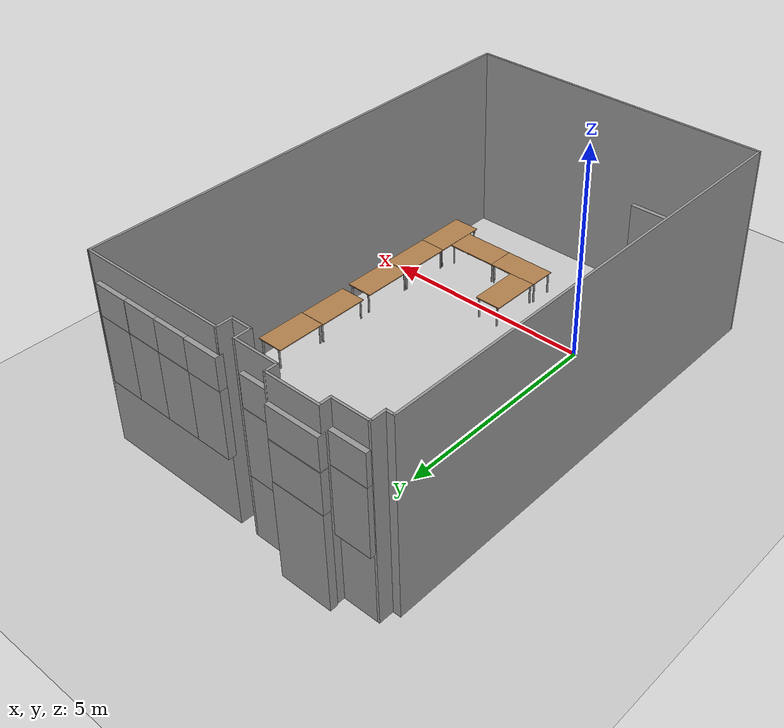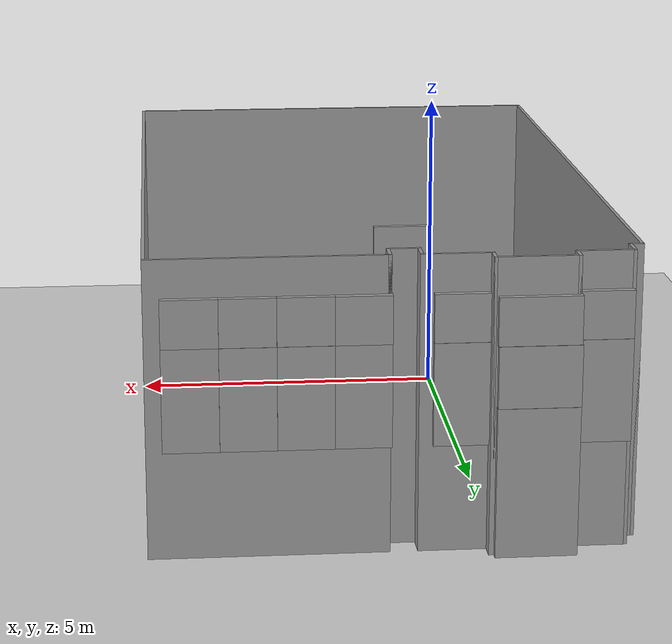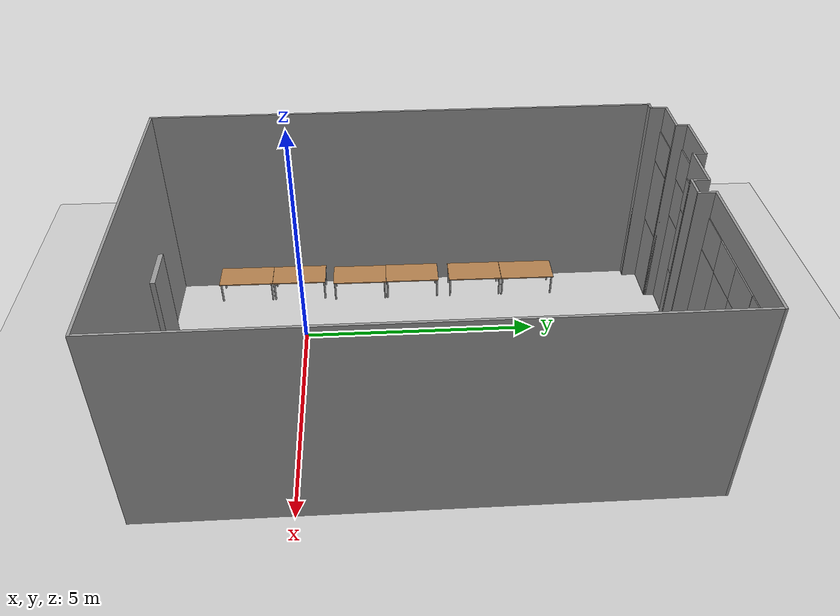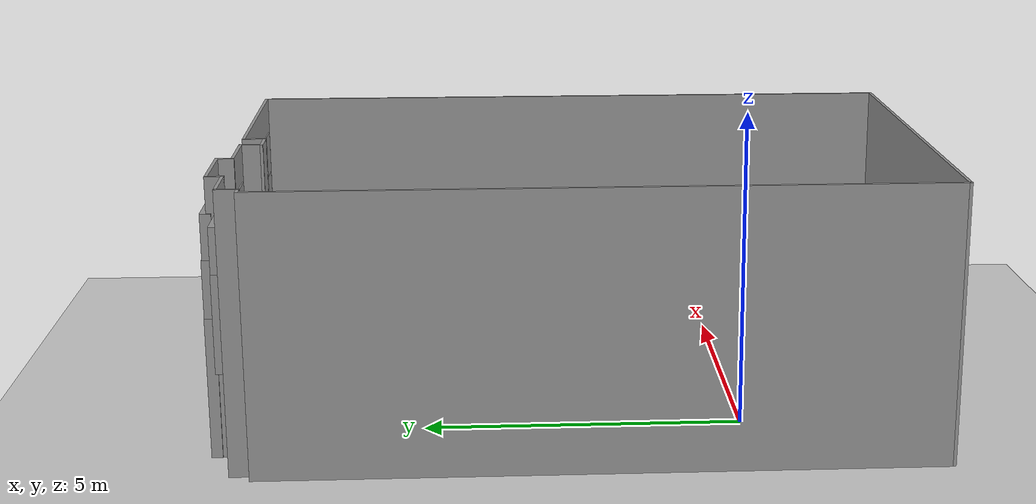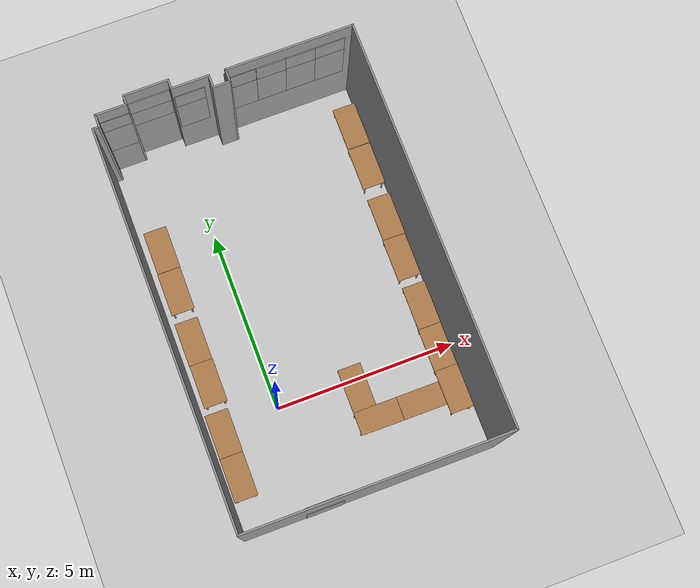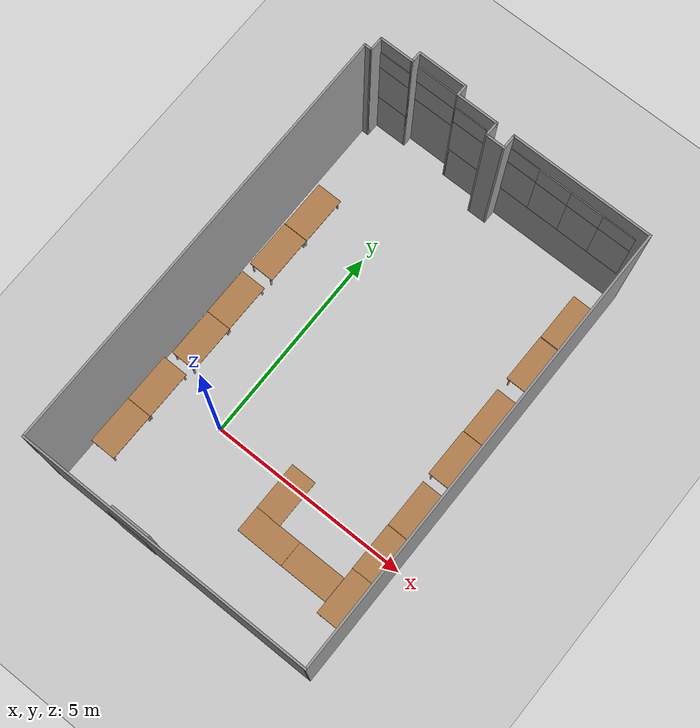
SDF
<sdf version="1.7">
 <world name="default">
  <light name="sun" type="directional">
   <pose>0 0 10 0 -0 0</pose>
   <diffuse>0.8 0.8 0.8 1</diffuse>
   <specular>0.2 0.2 0.2 1</specular>
   <attenuation>
    <range>1000</range>
    <constant>0.9</constant>
    <linear>0.01</linear>
    <quadratic>0.001</quadratic>
   </attenuation>
   <direction>-0.5 0.1 -0.9</direction>
   <spot><inner_angle>0</inner_angle><outer_angle>0</outer_angle><falloff>0</falloff></spot>
  </light>
  <model name="ground_plane">
   <static>1</static>
   <link name="link">
    <collision name="collision">
     <geometry><plane><normal>0 0 1</normal><size>100 100</size></plane></geometry>
     <surface>
      <contact><collide_bitmask>65535</collide_bitmask></contact>
      <friction><ode><mu>100</mu><mu2>50</mu2></ode></friction>
     </surface>
    </collision>
    <visual name="visual">
     <cast_shadows>0</cast_shadows>
     <geometry><plane><normal>0 0 1</normal><size>100 100</size></plane></geometry>
     <material>
      <script><uri>file://media/materials/scripts/gazebo.material</uri><name>Gazebo/Grey</name></script>
     </material>
    </visual>
   </link>
  </model>
  <gravity>0 0 -9.8</gravity>
  <magnetic_field>6e-06 2.3e-05 -4.2e-05</magnetic_field>
  <atmosphere type="adiabatic"/>
  <physics name="default_physics" default="0" type="ode">
   <max_step_size>0.001</max_step_size>
   <real_time_factor>1</real_time_factor>
   <real_time_update_rate>1000</real_time_update_rate>
  </physics>
  <scene><ambient>0.4 0.4 0.4 1</ambient><background>0.7 0.7 0.7 1</background><shadows>1</shadows></scene>
  <audio><device>default</device></audio>
  <spherical_coordinates>
   <surface_model>EARTH_WGS84</surface_model>
   <latitude_deg>0</latitude_deg>
   <longitude_deg>0</longitude_deg>
   <elevation>0</elevation>
   <heading_deg>0</heading_deg>
  </spherical_coordinates>
  <model name="RoboticLab">
   <pose>1.47128 2.55443 0 0 -0 0</pose>
   <link name="Wall_14">
    <collision name="Wall_14_Collision">
     <geometry><box><size>6.99 0.05 4.35</size></box></geometry>
     <pose>0 0 2.175 0 -0 0</pose>
    </collision>
    <visual name="Wall_14_Visual">
     <pose>0 0 2.175 0 -0 0</pose>
     <geometry><box><size>6.99 0.05 4.35</size></box></geometry>
     <material>
      <script><uri>file://media/materials/scripts/gazebo.material</uri><name>Gazebo/Grey</name></script>
      <ambient>1 1 1 1</ambient>
     </material>
     <meta><layer>0</layer></meta>
    </visual>
    <pose>-0 -5.495 0 0 -0 0</pose>
   </link>
   <link name="Wall_16">
    <collision name="Wall_16_Collision">
     <geometry><box><size>10.8 0.05 4.35</size></box></geometry>
     <pose>0 0 2.175 0 -0 0</pose>
    </collision>
    <visual name="Wall_16_Visual">
     <pose>0 0 2.175 0 -0 0</pose>
     <geometry><box><size>10.8 0.05 4.35</size></box></geometry>
     <material>
      <script><uri>file://media/materials/scripts/gazebo.material</uri><name>Gazebo/Grey</name></script>
      <ambient>1 1 1 1</ambient>
     </material>
     <meta><layer>0</layer></meta>
    </visual>
    <pose>3.47 -0.12 0 0 -0 1.5708</pose>
   </link>
   <link name="Wall_18">
    <collision name="Wall_18_Collision">
     <geometry><box><size>10.48 0.05 4.35</size></box></geometry>
     <pose>0 0 2.175 0 -0 0</pose>
    </collision>
    <visual name="Wall_18_Visual">
     <pose>0 0 2.175 0 -0 0</pose>
     <geometry><box><size>10.48 0.05 4.35</size></box></geometry>
     <material>
      <script><uri>file://media/materials/scripts/gazebo.material</uri><name>Gazebo/Grey</name></script>
      <ambient>1 1 1 1</ambient>
     </material>
     <meta><layer>0</layer></meta>
    </visual>
    <pose>-3.47 -0.28 0 0 -0 1.5708</pose>
   </link>
   <link name="Wall_20">
    <collision name="Wall_20_Collision">
     <geometry><box><size>0.22 0.05 4.35</size></box></geometry>
     <pose>0 0 2.175 0 -0 0</pose>
    </collision>
    <visual name="Wall_20_Visual">
     <pose>0 0 2.175 0 -0 0</pose>
     <geometry><box><size>0.22 0.05 4.35</size></box></geometry>
     <material>
      <script><uri>file://media/materials/scripts/gazebo.material</uri><name>Gazebo/Grey</name></script>
      <ambient>1 1 1 1</ambient>
     </material>
     <meta><layer>0</layer></meta>
    </visual>
    <pose>-3.385 4.935 0 0 -0 0</pose>
   </link>
   <link name="Wall_25">
    <collision name="Wall_25_Collision">
     <geometry><box><size>0.37 0.05 4.35</size></box></geometry>
     <pose>0 0 2.175 0 -0 0</pose>
    </collision>
    <visual name="Wall_25_Visual">
     <pose>0 0 2.175 0 -0 0</pose>
     <geometry><box><size>0.37 0.05 4.35</size></box></geometry>
     <material>
      <script><uri>file://media/materials/scripts/gazebo.material</uri><name>Gazebo/Grey</name></script>
      <ambient>1 1 1 1</ambient>
     </material>
     <meta><layer>0</layer></meta>
    </visual>
    <pose>-3.3 5.095 0 0 -0 1.5708</pose>
   </link>
   <link name="Wall_27">
    <collision name="Wall_27_Collision">
     <geometry><box><size>0.86 0.05 4.35</size></box></geometry>
     <pose>0 0 2.175 0 -0 0</pose>
    </collision>
    <visual name="Wall_27_Visual">
     <pose>0 0 2.175 0 -0 0</pose>
     <geometry><box><size>0.86 0.05 4.35</size></box></geometry>
     <material>
      <script><uri>file://media/materials/scripts/gazebo.material</uri><name>Gazebo/Grey</name></script>
      <ambient>1 1 1 1</ambient>
     </material>
     <meta><layer>0</layer></meta>
    </visual>
    <pose>-2.895 5.255 0 0 -0 0</pose>
   </link>
   <link name="Wall_29">
    <collision name="Wall_29_Collision">
     <geometry><box><size>0.29 0.05 4.35</size></box></geometry>
     <pose>0 0 2.175 0 -0 0</pose>
    </collision>
    <visual name="Wall_29_Visual">
     <pose>0 0 2.175 0 -0 0</pose>
     <geometry><box><size>0.29 0.05 4.35</size></box></geometry>
     <material>
      <script><uri>file://media/materials/scripts/gazebo.material</uri><name>Gazebo/Grey</name></script>
      <ambient>1 1 1 1</ambient>
     </material>
     <meta><layer>0</layer></meta>
    </visual>
    <pose>-2.49 5.375 0 0 -0 1.5708</pose>
   </link>
   <link name="Wall_32">
    <collision name="Wall_32_Collision">
     <geometry><box><size>1.22 0.05 4.35</size></box></geometry>
     <pose>0 0 2.175 0 -0 0</pose>
    </collision>
    <visual name="Wall_32_Visual">
     <pose>0 0 2.175 0 -0 0</pose>
     <geometry><box><size>1.22 0.05 4.35</size></box></geometry>
     <material>
      <script><uri>file://media/materials/scripts/gazebo.material</uri><name>Gazebo/Grey</name></script>
      <ambient>1 1 1 1</ambient>
     </material>
     <meta><layer>0</layer></meta>
    </visual>
    <pose>-1.905 5.495 0 0 -0 0</pose>
   </link>
   <link name="Wall_34">
    <collision name="Wall_34_Collision">
     <geometry><box><size>0.29 0.05 4.35</size></box></geometry>
     <pose>0 0 2.175 0 -0 0</pose>
    </collision>
    <visual name="Wall_34_Visual">
     <pose>0 0 2.175 0 -0 0</pose>
     <geometry><box><size>0.29 0.05 4.35</size></box></geometry>
     <material>
      <script><uri>file://media/materials/scripts/gazebo.material</uri><name>Gazebo/Grey</name></script>
      <ambient>1 1 1 1</ambient>
     </material>
     <meta><layer>0</layer></meta>
    </visual>
    <pose>-1.32 5.375 0 0 -0 -1.5708</pose>
   </link>
   <link name="Wall_37">
    <collision name="Wall_37_Collision">
     <geometry><box><size>1.03 0.05 4.35</size></box></geometry>
     <pose>0 0 2.175 0 -0 0</pose>
    </collision>
    <visual name="Wall_37_Visual">
     <pose>0 0 2.175 0 -0 0</pose>
     <geometry><box><size>1.03 0.05 4.35</size></box></geometry>
     <material>
      <script><uri>file://media/materials/scripts/gazebo.material</uri><name>Gazebo/Grey</name></script>
      <ambient>1 1 1 1</ambient>
     </material>
     <meta><layer>0</layer></meta>
    </visual>
    <pose>-0.83 5.255 0 0 -0 0</pose>
   </link>
   <link name="Wall_39">
    <collision name="Wall_39_Collision">
     <geometry><box><size>0.38 0.05 4.35</size></box></geometry>
     <pose>0 0 2.175 0 -0 0</pose>
    </collision>
    <visual name="Wall_39_Visual">
     <pose>0 0 2.175 0 -0 0</pose>
     <geometry><box><size>0.38 0.05 4.35</size></box></geometry>
     <material>
      <script><uri>file://media/materials/scripts/gazebo.material</uri><name>Gazebo/Grey</name></script>
      <ambient>1 1 1 1</ambient>
     </material>
     <meta><layer>0</layer></meta>
    </visual>
    <pose>-0.34 5.09 0 0 -0 -1.5708</pose>
   </link>
   <link name="Wall_41">
    <collision name="Wall_41_Collision">
     <geometry><box><size>0.49 0.05 4.35</size></box></geometry>
     <pose>0 0 2.175 0 -0 0</pose>
    </collision>
    <visual name="Wall_41_Visual">
     <pose>0 0 2.175 0 -0 0</pose>
     <geometry><box><size>0.49 0.05 4.35</size></box></geometry>
     <material>
      <script><uri>file://media/materials/scripts/gazebo.material</uri><name>Gazebo/Grey</name></script>
      <ambient>1 1 1 1</ambient>
     </material>
     <meta><layer>0</layer></meta>
    </visual>
    <pose>-0.12 4.925 0 0 -0 0</pose>
   </link>
   <link name="Wall_43">
    <collision name="Wall_43_Collision">
     <geometry><box><size>0.38 0.05 4.35</size></box></geometry>
     <pose>0 0 2.175 0 -0 0</pose>
    </collision>
    <visual name="Wall_43_Visual">
     <pose>0 0 2.175 0 -0 0</pose>
     <geometry><box><size>0.38 0.05 4.35</size></box></geometry>
     <material>
      <script><uri>file://media/materials/scripts/gazebo.material</uri><name>Gazebo/Grey</name></script>
      <ambient>1 1 1 1</ambient>
     </material>
     <meta><layer>0</layer></meta>
    </visual>
    <pose>0.1 5.09 0 0 -0 1.5708</pose>
   </link>
   <link name="Wall_45">
    <collision name="Wall_45_Collision">
     <geometry><box><size>3.42 0.05 4.35</size></box></geometry>
     <pose>0 0 2.175 0 -0 0</pose>
    </collision>
    <visual name="Wall_45_Visual">
     <pose>0 0 2.175 0 -0 0</pose>
     <geometry><box><size>3.42 0.05 4.35</size></box></geometry>
     <material>
      <script><uri>file://media/materials/scripts/gazebo.material</uri><name>Gazebo/Grey</name></script>
      <ambient>1 1 1 1</ambient>
     </material>
     <meta><layer>0</layer></meta>
    </visual>
    <pose>1.785 5.255 0 0 -0 0</pose>
   </link>
   <static>1</static>
  </model>
  <model name="RoboticLabWIndows">
   <pose>1.4338 2.64515 0 0 -0 0</pose>
   <link name="Door_0">
    <collision name="Door_0_Collision">
     <geometry><box><size>1.17 0.17 2.2</size></box></geometry>
     <pose>0 0 1.1 0 -0 0</pose>
    </collision>
    <visual name="Door_0_Visual">
     <pose>0 0 1.1 0 -0 0</pose>
     <geometry><box><size>1.17 0.17 2.2</size></box></geometry>
     <material>
      <script><uri>file://media/materials/scripts/gazebo.material</uri><name>Gazebo/Grey</name></script>
     </material>
    </visual>
    <pose>-1.91683 5.45564 0 0 -0 0</pose>
   </link>
   <link name="Door_1">
    <collision name="Door_1_Collision">
     <geometry><box><size>1 0.17 2.1</size></box></geometry>
     <pose>0 0 1.05 0 -0 0</pose>
    </collision>
    <visual name="Door_1_Visual">
     <pose>0 0 1.05 0 -0 0</pose>
     <geometry><box><size>1 0.17 2.1</size></box></geometry>
     <material>
      <script><uri>file://media/materials/scripts/gazebo.material</uri><name>Gazebo/Grey</name></script>
     </material>
    </visual>
    <pose>-1.23571 -5.53979 0 0 -0 0</pose>
   </link>
   <link name="Window_1">
    <collision name="Window_1_Collision">
     <geometry><box><size>0.8 0.17 1.5</size></box></geometry>
     <pose>0 0 0.75 0 -0 0</pose>
    </collision>
    <visual name="Window_1_Visual">
     <pose>0 0 0.75 0 -0 0</pose>
     <geometry><box><size>0.8 0.17 1.5</size></box></geometry>
     <material>
      <script><uri>file://media/materials/scripts/gazebo.material</uri><name>Gazebo/Grey</name></script>
     </material>
    </visual>
    <pose>-2.86594 5.21551 1.6 0 -0 0</pose>
   </link>
   <link name="Window_10">
    <collision name="Window_10_Collision">
     <geometry><box><size>0.8 0.17 1.5</size></box></geometry>
     <pose>0 0 0.75 0 -0 0</pose>
    </collision>
    <visual name="Window_10_Visual">
     <pose>0 0 0.75 0 -0 0</pose>
     <geometry><box><size>0.8 0.17 1.5</size></box></geometry>
     <material>
      <script><uri>file://media/materials/scripts/gazebo.material</uri><name>Gazebo/Grey</name></script>
     </material>
    </visual>
    <pose>2.90305 5.20407 1.6 0 -0 0</pose>
   </link>
   <link name="Window_11">
    <collision name="Window_11_Collision">
     <geometry><box><size>0.8 0.17 0.7</size></box></geometry>
     <pose>0 0 0.35 0 -0 0</pose>
    </collision>
    <visual name="Window_11_Visual">
     <pose>0 0 0.35 0 -0 0</pose>
     <geometry><box><size>0.8 0.17 0.7</size></box></geometry>
     <material>
      <script><uri>file://media/materials/scripts/gazebo.material</uri><name>Gazebo/Grey</name></script>
     </material>
    </visual>
    <pose>0.501685 5.20979 3.1 0 -0 0</pose>
   </link>
   <link name="Window_12">
    <collision name="Window_12_Collision">
     <geometry><box><size>0.8 0.17 0.7</size></box></geometry>
     <pose>0 0 0.35 0 -0 0</pose>
    </collision>
    <visual name="Window_12_Visual">
     <pose>0 0 0.35 0 -0 0</pose>
     <geometry><box><size>0.8 0.17 0.7</size></box></geometry>
     <material>
      <script><uri>file://media/materials/scripts/gazebo.material</uri><name>Gazebo/Grey</name></script>
     </material>
    </visual>
    <pose>1.30214 5.19835 3.1 0 -0 0</pose>
   </link>
   <link name="Window_13">
    <collision name="Window_13_Collision">
     <geometry><box><size>0.8 0.17 0.7</size></box></geometry>
     <pose>0 0 0.35 0 -0 0</pose>
    </collision>
    <visual name="Window_13_Visual">
     <pose>0 0 0.35 0 -0 0</pose>
     <geometry><box><size>0.8 0.17 0.7</size></box></geometry>
     <material>
      <script><uri>file://media/materials/scripts/gazebo.material</uri><name>Gazebo/Grey</name></script>
     </material>
    </visual>
    <pose>2.10259 5.19835 3.1 0 -0 0</pose>
   </link>
   <link name="Window_14">
    <collision name="Window_14_Collision">
     <geometry><box><size>0.8 0.17 0.7</size></box></geometry>
     <pose>0 0 0.35 0 -0 0</pose>
    </collision>
    <visual name="Window_14_Visual">
     <pose>0 0 0.35 0 -0 0</pose>
     <geometry><box><size>0.8 0.17 0.7</size></box></geometry>
     <material>
      <script><uri>file://media/materials/scripts/gazebo.material</uri><name>Gazebo/Grey</name></script>
     </material>
    </visual>
    <pose>2.90305 5.20407 3.1 0 -0 0</pose>
   </link>
   <link name="Window_2">
    <collision name="Window_2_Collision">
     <geometry><box><size>0.8 0.17 1.5</size></box></geometry>
     <pose>0 0 0.75 0 -0 0</pose>
    </collision>
    <visual name="Window_2_Visual">
     <pose>0 0 0.75 0 -0 0</pose>
     <geometry><box><size>0.8 0.17 1.5</size></box></geometry>
     <material>
      <script><uri>file://media/materials/scripts/gazebo.material</uri><name>Gazebo/Grey</name></script>
     </material>
    </visual>
    <pose>-0.870523 5.20979 1.6 0 -0 0</pose>
   </link>
   <link name="Window_3">
    <collision name="Window_3_Collision">
     <geometry><box><size>0.8 0.17 0.7</size></box></geometry>
     <pose>0 0 0.35 0 -0 0</pose>
    </collision>
    <visual name="Window_3_Visual">
     <pose>0 0 0.35 0 -0 0</pose>
     <geometry><box><size>0.8 0.17 0.7</size></box></geometry>
     <material>
      <script><uri>file://media/materials/scripts/gazebo.material</uri><name>Gazebo/Grey</name></script>
     </material>
    </visual>
    <pose>-2.86594 5.20979 3.1 0 -0 0</pose>
   </link>
   <link name="Window_4">
    <collision name="Window_4_Collision">
     <geometry><box><size>0.8 0.17 0.7</size></box></geometry>
     <pose>0 0 0.35 0 -0 0</pose>
    </collision>
    <visual name="Window_4_Visual">
     <pose>0 0 0.35 0 -0 0</pose>
     <geometry><box><size>0.8 0.17 0.7</size></box></geometry>
     <material>
      <script><uri>file://media/materials/scripts/gazebo.material</uri><name>Gazebo/Grey</name></script>
     </material>
    </visual>
    <pose>-0.870523 5.20407 3.1 0 -0 0</pose>
   </link>
   <link name="Window_5">
    <collision name="Window_5_Collision">
     <geometry><box><size>1.17 0.17 0.9</size></box></geometry>
     <pose>0 0 0.45 0 -0 0</pose>
    </collision>
    <visual name="Window_5_Visual">
     <pose>0 0 0.45 0 -0 0</pose>
     <geometry><box><size>1.17 0.17 0.9</size></box></geometry>
     <material>
      <script><uri>file://media/materials/scripts/gazebo.material</uri><name>Gazebo/Grey</name></script>
     </material>
    </visual>
    <pose>-1.92255 5.44993 2.2 0 -0 0</pose>
   </link>
   <link name="Window_6">
    <collision name="Window_6_Collision">
     <geometry><box><size>1.17 0.17 0.7</size></box></geometry>
     <pose>0 0 0.35 0 -0 0</pose>
    </collision>
    <visual name="Window_6_Visual">
     <pose>0 0 0.35 0 -0 0</pose>
     <geometry><box><size>1.17 0.17 0.7</size></box></geometry>
     <material>
      <script><uri>file://media/materials/scripts/gazebo.material</uri><name>Gazebo/Grey</name></script>
     </material>
    </visual>
    <pose>-1.91111 5.43849 3.1 0 -0 0</pose>
   </link>
   <link name="Window_7">
    <collision name="Window_7_Collision">
     <geometry><box><size>0.8 0.17 1.5</size></box></geometry>
     <pose>0 0 0.75 0 -0 0</pose>
    </collision>
    <visual name="Window_7_Visual">
     <pose>0 0 0.75 0 -0 0</pose>
     <geometry><box><size>0.8 0.17 1.5</size></box></geometry>
     <material>
      <script><uri>file://media/materials/scripts/gazebo.material</uri><name>Gazebo/Grey</name></script>
     </material>
    </visual>
    <pose>0.501685 5.20407 1.6 0 -0 0</pose>
   </link>
   <link name="Window_8">
    <collision name="Window_8_Collision">
     <geometry><box><size>0.8 0.17 1.5</size></box></geometry>
     <pose>0 0 0.75 0 -0 0</pose>
    </collision>
    <visual name="Window_8_Visual">
     <pose>0 0 0.75 0 -0 0</pose>
     <geometry><box><size>0.8 0.17 1.5</size></box></geometry>
     <material>
      <script><uri>file://media/materials/scripts/gazebo.material</uri><name>Gazebo/Grey</name></script>
     </material>
    </visual>
    <pose>1.30214 5.20407 1.6 0 -0 0</pose>
   </link>
   <link name="Window_9">
    <collision name="Window_9_Collision">
     <geometry><box><size>0.8 0.17 1.5</size></box></geometry>
     <pose>0 0 0.75 0 -0 0</pose>
    </collision>
    <visual name="Window_9_Visual">
     <pose>0 0 0.75 0 -0 0</pose>
     <geometry><box><size>0.8 0.17 1.5</size></box></geometry>
     <material>
      <script><uri>file://media/materials/scripts/gazebo.material</uri><name>Gazebo/Grey</name></script>
     </material>
    </visual>
    <pose>2.10259 5.20407 1.6 0 -0 0</pose>
   </link>
   <static>1</static>
  </model>
  <model name="table_for_pc">
   <link name="link">
    <inertial>
     <mass>1</mass>
     <inertia><ixx>1</ixx><ixy>0</ixy><ixz>0</ixz><iyy>1</iyy><iyz>0</iyz><izz>1</izz></inertia>
    </inertial>
    <visual name="back_right_leg">
     <pose>-0.57 -0.25 0.25 0 -0 0</pose>
     <geometry><cylinder><radius>0.02</radius><length>0.5</length></cylinder></geometry>
     <material>
      <script><uri>file://media/materials/scripts/gazebo.material</uri><name>Gazebo/Grey</name></script>
      <shader type="vertex"><normal_map>__default__</normal_map></shader>
      <ambient>0.3 0.3 0.3 1</ambient>
      <diffuse>0.7 0.7 0.7 1</diffuse>
      <specular>0.01 0.01 0.01 1</specular>
      <emissive>0 0 0 1</emissive>
     </material>
    </visual>
    <visual name="back_left_leg">
     <pose>-0.57 0.25 0.25 0 -0 0</pose>
     <geometry><cylinder><radius>0.02</radius><length>0.5</length></cylinder></geometry>
     <material>
      <script><uri>file://media/materials/scripts/gazebo.material</uri><name>Gazebo/Grey</name></script>
      <shader type="vertex"><normal_map>__default__</normal_map></shader>
      <ambient>0.3 0.3 0.3 1</ambient>
      <diffuse>0.7 0.7 0.7 1</diffuse>
      <specular>0.01 0.01 0.01 1</specular>
      <emissive>0 0 0 1</emissive>
     </material>
    </visual>
    <visual name="front_right_leg">
     <pose>0.57 -0.25 0.25 0 -0 0</pose>
     <geometry><cylinder><radius>0.02</radius><length>0.5</length></cylinder></geometry>
     <material>
      <script><uri>file://media/materials/scripts/gazebo.material</uri><name>Gazebo/Grey</name></script>
      <shader type="vertex"><normal_map>__default__</normal_map></shader>
      <ambient>0.3 0.3 0.3 1</ambient>
      <diffuse>0.7 0.7 0.7 1</diffuse>
      <specular>0.01 0.01 0.01 1</specular>
      <emissive>0 0 0 1</emissive>
     </material>
    </visual>
    <visual name="visual1">
     <pose>0 0 0.5 0 -0 0</pose>
     <geometry><box><size>1.2 0.64 0.024</size></box></geometry>
     <material>
      <script><uri>file://media/materials/scripts/gazebo.material</uri><name>Gazebo/Wood</name></script>
      <shader type="vertex"><normal_map>__default__</normal_map></shader>
      <ambient>1 1 1 1</ambient>
      <diffuse>1 1 1 1</diffuse>
      <specular>0.2 0.2 0.2 1</specular>
      <emissive>0 0 0 1</emissive>
     </material>
    </visual>
    <visual name="front_left_leg">
     <pose>0.57 0.25 0.25 0 -0 0</pose>
     <geometry><cylinder><radius>0.02</radius><length>0.5</length></cylinder></geometry>
     <material>
      <script><uri>file://media/materials/scripts/gazebo.material</uri><name>Gazebo/Grey</name></script>
      <shader type="vertex"><normal_map>__default__</normal_map></shader>
      <ambient>0.3 0.3 0.3 1</ambient>
      <diffuse>0.7 0.7 0.7 1</diffuse>
      <specular>0.01 0.01 0.01 1</specular>
      <emissive>0 0 0 1</emissive>
     </material>
    </visual>
    <collision name="surface">
     <pose>0 0 0.5 0 -0 0</pose>
     <geometry><box><size>1.2 0.64 0.024</size></box></geometry>
     <surface>
      <friction>
       <ode><mu>0.6</mu><mu2>0.6</mu2><fdir1>0 0 0</fdir1><slip1>0</slip1><slip2>0</slip2></ode>
       <torsional>
        <coefficient>1</coefficient>
        <patch_radius>0</patch_radius>
        <surface_radius>0</surface_radius>
        <use_patch_radius>1</use_patch_radius>
        <ode><slip>0</slip></ode>
       </torsional>
      </friction>
      <bounce><restitution_coefficient>0</restitution_coefficient><threshold>1e+06</threshold></bounce>
      <contact>
       <collide_without_contact>0</collide_without_contact>
       <collide_without_contact_bitmask>1</collide_without_contact_bitmask>
       <collide_bitmask>1</collide_bitmask>
       <ode>
        <soft_cfm>0</soft_cfm>
        <soft_erp>0.2</soft_erp>
        <kp>1e+13</kp>
        <kd>1</kd>
        <max_vel>0.01</max_vel>
        <min_depth>0</min_depth>
       </ode>
       <bullet>
        <split_impulse>1</split_impulse>
        <split_impulse_penetration_threshold>-0.01</split_impulse_penetration_threshold>
        <soft_cfm>0</soft_cfm>
        <soft_erp>0.2</soft_erp>
        <kp>1e+13</kp>
        <kd>1</kd>
       </bullet>
      </contact>
     </surface>
    </collision>
    <collision name="back_right_leg">
     <pose>-0.57 -0.25 0.25 0 -0 0</pose>
     <geometry><cylinder><radius>0.02</radius><length>0.5</length></cylinder></geometry>
     <surface>
      <friction>
       <ode><mu>1</mu><mu2>1</mu2><fdir1>0 0 0</fdir1><slip1>0</slip1><slip2>0</slip2></ode>
       <torsional>
        <coefficient>1</coefficient>
        <patch_radius>0</patch_radius>
        <surface_radius>0</surface_radius>
        <use_patch_radius>1</use_patch_radius>
        <ode><slip>0</slip></ode>
       </torsional>
      </friction>
      <bounce><restitution_coefficient>0</restitution_coefficient><threshold>1e+06</threshold></bounce>
      <contact>
       <collide_without_contact>0</collide_without_contact>
       <collide_without_contact_bitmask>1</collide_without_contact_bitmask>
       <collide_bitmask>1</collide_bitmask>
       <ode>
        <soft_cfm>0</soft_cfm>
        <soft_erp>0.2</soft_erp>
        <kp>1e+13</kp>
        <kd>1</kd>
        <max_vel>0.01</max_vel>
        <min_depth>0</min_depth>
       </ode>
       <bullet>
        <split_impulse>1</split_impulse>
        <split_impulse_penetration_threshold>-0.01</split_impulse_penetration_threshold>
        <soft_cfm>0</soft_cfm>
        <soft_erp>0.2</soft_erp>
        <kp>1e+13</kp>
        <kd>1</kd>
       </bullet>
      </contact>
     </surface>
    </collision>
    <collision name="front_right_leg">
     <pose>0.57 -0.25 0.25 0 -0 0</pose>
     <geometry><cylinder><radius>0.02</radius><length>0.5</length></cylinder></geometry>
     <surface>
      <friction>
       <ode><mu>1</mu><mu2>1</mu2><fdir1>0 0 0</fdir1><slip1>0</slip1><slip2>0</slip2></ode>
       <torsional>
        <coefficient>1</coefficient>
        <patch_radius>0</patch_radius>
        <surface_radius>0</surface_radius>
        <use_patch_radius>1</use_patch_radius>
        <ode><slip>0</slip></ode>
       </torsional>
      </friction>
      <bounce><restitution_coefficient>0</restitution_coefficient><threshold>1e+06</threshold></bounce>
      <contact>
       <collide_without_contact>0</collide_without_contact>
       <collide_without_contact_bitmask>1</collide_without_contact_bitmask>
       <collide_bitmask>1</collide_bitmask>
       <ode>
        <soft_cfm>0</soft_cfm>
        <soft_erp>0.2</soft_erp>
        <kp>1e+13</kp>
        <kd>1</kd>
        <max_vel>0.01</max_vel>
        <min_depth>0</min_depth>
       </ode>
       <bullet>
        <split_impulse>1</split_impulse>
        <split_impulse_penetration_threshold>-0.01</split_impulse_penetration_threshold>
        <soft_cfm>0</soft_cfm>
        <soft_erp>0.2</soft_erp>
        <kp>1e+13</kp>
        <kd>1</kd>
       </bullet>
      </contact>
     </surface>
    </collision>
    <collision name="back_left_leg">
     <pose>-0.57 0.25 0.25 0 -0 0</pose>
     <geometry><cylinder><radius>0.02</radius><length>0.5</length></cylinder></geometry>
     <surface>
      <friction>
       <ode><mu>1</mu><mu2>1</mu2><fdir1>0 0 0</fdir1><slip1>0</slip1><slip2>0</slip2></ode>
       <torsional>
        <coefficient>1</coefficient>
        <patch_radius>0</patch_radius>
        <surface_radius>0</surface_radius>
        <use_patch_radius>1</use_patch_radius>
        <ode><slip>0</slip></ode>
       </torsional>
      </friction>
      <bounce><restitution_coefficient>0</restitution_coefficient><threshold>1e+06</threshold></bounce>
      <contact>
       <collide_without_contact>0</collide_without_contact>
       <collide_without_contact_bitmask>1</collide_without_contact_bitmask>
       <collide_bitmask>1</collide_bitmask>
       <ode>
        <soft_cfm>0</soft_cfm>
        <soft_erp>0.2</soft_erp>
        <kp>1e+13</kp>
        <kd>1</kd>
        <max_vel>0.01</max_vel>
        <min_depth>0</min_depth>
       </ode>
       <bullet>
        <split_impulse>1</split_impulse>
        <split_impulse_penetration_threshold>-0.01</split_impulse_penetration_threshold>
        <soft_cfm>0</soft_cfm>
        <soft_erp>0.2</soft_erp>
        <kp>1e+13</kp>
        <kd>1</kd>
       </bullet>
      </contact>
     </surface>
    </collision>
    <collision name="front_left_leg">
     <pose>0.57 0.25 0.25 0 -0 0</pose>
     <geometry><cylinder><radius>0.02</radius><length>0.5</length></cylinder></geometry>
     <surface>
      <friction>
       <ode><mu>1</mu><mu2>1</mu2><fdir1>0 0 0</fdir1><slip1>0</slip1><slip2>0</slip2></ode>
       <torsional>
        <coefficient>1</coefficient>
        <patch_radius>0</patch_radius>
        <surface_radius>0</surface_radius>
        <use_patch_radius>1</use_patch_radius>
        <ode><slip>0</slip></ode>
       </torsional>
      </friction>
      <bounce><restitution_coefficient>0</restitution_coefficient><threshold>1e+06</threshold></bounce>
      <contact>
       <collide_without_contact>0</collide_without_contact>
       <collide_without_contact_bitmask>1</collide_without_contact_bitmask>
       <collide_bitmask>1</collide_bitmask>
       <ode>
        <soft_cfm>0</soft_cfm>
        <soft_erp>0.2</soft_erp>
        <kp>1e+13</kp>
        <kd>1</kd>
        <max_vel>0.01</max_vel>
        <min_depth>0</min_depth>
       </ode>
       <bullet>
        <split_impulse>1</split_impulse>
        <split_impulse_penetration_threshold>-0.01</split_impulse_penetration_threshold>
        <soft_cfm>0</soft_cfm>
        <soft_erp>0.2</soft_erp>
        <kp>1e+13</kp>
        <kd>1</kd>
       </bullet>
      </contact>
     </surface>
    </collision>
   </link>
   <static>1</static>
   <pose>-1.47699 5.05436 0 0 -0 1.56413</pose>
  </model>
  <model name="table_for_pc_clone">
   <link name="link">
    <inertial>
     <mass>1</mass>
     <inertia><ixx>1</ixx><ixy>0</ixy><ixz>0</ixz><iyy>1</iyy><iyz>0</iyz><izz>1</izz></inertia>
    </inertial>
    <visual name="back_right_leg">
     <pose>-0.57 -0.25 0.25 0 -0 0</pose>
     <geometry><cylinder><radius>0.02</radius><length>0.5</length></cylinder></geometry>
     <material>
      <script><uri>file://media/materials/scripts/gazebo.material</uri><name>Gazebo/Grey</name></script>
      <shader type="vertex"><normal_map>__default__</normal_map></shader>
      <ambient>0.3 0.3 0.3 1</ambient>
      <diffuse>0.7 0.7 0.7 1</diffuse>
      <specular>0.01 0.01 0.01 1</specular>
      <emissive>0 0 0 1</emissive>
     </material>
    </visual>
    <visual name="back_left_leg">
     <pose>-0.57 0.25 0.25 0 -0 0</pose>
     <geometry><cylinder><radius>0.02</radius><length>0.5</length></cylinder></geometry>
     <material>
      <script><uri>file://media/materials/scripts/gazebo.material</uri><name>Gazebo/Grey</name></script>
      <shader type="vertex"><normal_map>__default__</normal_map></shader>
      <ambient>0.3 0.3 0.3 1</ambient>
      <diffuse>0.7 0.7 0.7 1</diffuse>
      <specular>0.01 0.01 0.01 1</specular>
      <emissive>0 0 0 1</emissive>
     </material>
    </visual>
    <visual name="front_right_leg">
     <pose>0.57 -0.25 0.25 0 -0 0</pose>
     <geometry><cylinder><radius>0.02</radius><length>0.5</length></cylinder></geometry>
     <material>
      <script><uri>file://media/materials/scripts/gazebo.material</uri><name>Gazebo/Grey</name></script>
      <shader type="vertex"><normal_map>__default__</normal_map></shader>
      <ambient>0.3 0.3 0.3 1</ambient>
      <diffuse>0.7 0.7 0.7 1</diffuse>
      <specular>0.01 0.01 0.01 1</specular>
      <emissive>0 0 0 1</emissive>
     </material>
    </visual>
    <visual name="visual1">
     <pose>0 0 0.5 0 -0 0</pose>
     <geometry><box><size>1.2 0.64 0.024</size></box></geometry>
     <material>
      <script><uri>file://media/materials/scripts/gazebo.material</uri><name>Gazebo/Wood</name></script>
      <shader type="vertex"><normal_map>__default__</normal_map></shader>
      <ambient>1 1 1 1</ambient>
      <diffuse>1 1 1 1</diffuse>
      <specular>0.2 0.2 0.2 1</specular>
      <emissive>0 0 0 1</emissive>
     </material>
    </visual>
    <visual name="front_left_leg">
     <pose>0.57 0.25 0.25 0 -0 0</pose>
     <geometry><cylinder><radius>0.02</radius><length>0.5</length></cylinder></geometry>
     <material>
      <script><uri>file://media/materials/scripts/gazebo.material</uri><name>Gazebo/Grey</name></script>
      <shader type="vertex"><normal_map>__default__</normal_map></shader>
      <ambient>0.3 0.3 0.3 1</ambient>
      <diffuse>0.7 0.7 0.7 1</diffuse>
      <specular>0.01 0.01 0.01 1</specular>
      <emissive>0 0 0 1</emissive>
     </material>
    </visual>
    <collision name="surface">
     <pose>0 0 0.5 0 -0 0</pose>
     <geometry><box><size>1.2 0.64 0.024</size></box></geometry>
     <surface>
      <friction>
       <ode><mu>0.6</mu><mu2>0.6</mu2><fdir1>0 0 0</fdir1><slip1>0</slip1><slip2>0</slip2></ode>
       <torsional>
        <coefficient>1</coefficient>
        <patch_radius>0</patch_radius>
        <surface_radius>0</surface_radius>
        <use_patch_radius>1</use_patch_radius>
        <ode><slip>0</slip></ode>
       </torsional>
      </friction>
      <bounce><restitution_coefficient>0</restitution_coefficient><threshold>1e+06</threshold></bounce>
      <contact>
       <collide_without_contact>0</collide_without_contact>
       <collide_without_contact_bitmask>1</collide_without_contact_bitmask>
       <collide_bitmask>1</collide_bitmask>
       <ode>
        <soft_cfm>0</soft_cfm>
        <soft_erp>0.2</soft_erp>
        <kp>1e+13</kp>
        <kd>1</kd>
        <max_vel>0.01</max_vel>
        <min_depth>0</min_depth>
       </ode>
       <bullet>
        <split_impulse>1</split_impulse>
        <split_impulse_penetration_threshold>-0.01</split_impulse_penetration_threshold>
        <soft_cfm>0</soft_cfm>
        <soft_erp>0.2</soft_erp>
        <kp>1e+13</kp>
        <kd>1</kd>
       </bullet>
      </contact>
     </surface>
    </collision>
    <collision name="back_right_leg">
     <pose>-0.57 -0.25 0.25 0 -0 0</pose>
     <geometry><cylinder><radius>0.02</radius><length>0.5</length></cylinder></geometry>
     <surface>
      <friction>
       <ode><mu>1</mu><mu2>1</mu2><fdir1>0 0 0</fdir1><slip1>0</slip1><slip2>0</slip2></ode>
       <torsional>
        <coefficient>1</coefficient>
        <patch_radius>0</patch_radius>
        <surface_radius>0</surface_radius>
        <use_patch_radius>1</use_patch_radius>
        <ode><slip>0</slip></ode>
       </torsional>
      </friction>
      <bounce><restitution_coefficient>0</restitution_coefficient><threshold>1e+06</threshold></bounce>
      <contact>
       <collide_without_contact>0</collide_without_contact>
       <collide_without_contact_bitmask>1</collide_without_contact_bitmask>
       <collide_bitmask>1</collide_bitmask>
       <ode>
        <soft_cfm>0</soft_cfm>
        <soft_erp>0.2</soft_erp>
        <kp>1e+13</kp>
        <kd>1</kd>
        <max_vel>0.01</max_vel>
        <min_depth>0</min_depth>
       </ode>
       <bullet>
        <split_impulse>1</split_impulse>
        <split_impulse_penetration_threshold>-0.01</split_impulse_penetration_threshold>
        <soft_cfm>0</soft_cfm>
        <soft_erp>0.2</soft_erp>
        <kp>1e+13</kp>
        <kd>1</kd>
       </bullet>
      </contact>
     </surface>
    </collision>
    <collision name="front_right_leg">
     <pose>0.57 -0.25 0.25 0 -0 0</pose>
     <geometry><cylinder><radius>0.02</radius><length>0.5</length></cylinder></geometry>
     <surface>
      <friction>
       <ode><mu>1</mu><mu2>1</mu2><fdir1>0 0 0</fdir1><slip1>0</slip1><slip2>0</slip2></ode>
       <torsional>
        <coefficient>1</coefficient>
        <patch_radius>0</patch_radius>
        <surface_radius>0</surface_radius>
        <use_patch_radius>1</use_patch_radius>
        <ode><slip>0</slip></ode>
       </torsional>
      </friction>
      <bounce><restitution_coefficient>0</restitution_coefficient><threshold>1e+06</threshold></bounce>
      <contact>
       <collide_without_contact>0</collide_without_contact>
       <collide_without_contact_bitmask>1</collide_without_contact_bitmask>
       <collide_bitmask>1</collide_bitmask>
       <ode>
        <soft_cfm>0</soft_cfm>
        <soft_erp>0.2</soft_erp>
        <kp>1e+13</kp>
        <kd>1</kd>
        <max_vel>0.01</max_vel>
        <min_depth>0</min_depth>
       </ode>
       <bullet>
        <split_impulse>1</split_impulse>
        <split_impulse_penetration_threshold>-0.01</split_impulse_penetration_threshold>
        <soft_cfm>0</soft_cfm>
        <soft_erp>0.2</soft_erp>
        <kp>1e+13</kp>
        <kd>1</kd>
       </bullet>
      </contact>
     </surface>
    </collision>
    <collision name="back_left_leg">
     <pose>-0.57 0.25 0.25 0 -0 0</pose>
     <geometry><cylinder><radius>0.02</radius><length>0.5</length></cylinder></geometry>
     <surface>
      <friction>
       <ode><mu>1</mu><mu2>1</mu2><fdir1>0 0 0</fdir1><slip1>0</slip1><slip2>0</slip2></ode>
       <torsional>
        <coefficient>1</coefficient>
        <patch_radius>0</patch_radius>
        <surface_radius>0</surface_radius>
        <use_patch_radius>1</use_patch_radius>
        <ode><slip>0</slip></ode>
       </torsional>
      </friction>
      <bounce><restitution_coefficient>0</restitution_coefficient><threshold>1e+06</threshold></bounce>
      <contact>
       <collide_without_contact>0</collide_without_contact>
       <collide_without_contact_bitmask>1</collide_without_contact_bitmask>
       <collide_bitmask>1</collide_bitmask>
       <ode>
        <soft_cfm>0</soft_cfm>
        <soft_erp>0.2</soft_erp>
        <kp>1e+13</kp>
        <kd>1</kd>
        <max_vel>0.01</max_vel>
        <min_depth>0</min_depth>
       </ode>
       <bullet>
        <split_impulse>1</split_impulse>
        <split_impulse_penetration_threshold>-0.01</split_impulse_penetration_threshold>
        <soft_cfm>0</soft_cfm>
        <soft_erp>0.2</soft_erp>
        <kp>1e+13</kp>
        <kd>1</kd>
       </bullet>
      </contact>
     </surface>
    </collision>
    <collision name="front_left_leg">
     <pose>0.57 0.25 0.25 0 -0 0</pose>
     <geometry><cylinder><radius>0.02</radius><length>0.5</length></cylinder></geometry>
     <surface>
      <friction>
       <ode><mu>1</mu><mu2>1</mu2><fdir1>0 0 0</fdir1><slip1>0</slip1><slip2>0</slip2></ode>
       <torsional>
        <coefficient>1</coefficient>
        <patch_radius>0</patch_radius>
        <surface_radius>0</surface_radius>
        <use_patch_radius>1</use_patch_radius>
        <ode><slip>0</slip></ode>
       </torsional>
      </friction>
      <bounce><restitution_coefficient>0</restitution_coefficient><threshold>1e+06</threshold></bounce>
      <contact>
       <collide_without_contact>0</collide_without_contact>
       <collide_without_contact_bitmask>1</collide_without_contact_bitmask>
       <collide_bitmask>1</collide_bitmask>
       <ode>
        <soft_cfm>0</soft_cfm>
        <soft_erp>0.2</soft_erp>
        <kp>1e+13</kp>
        <kd>1</kd>
        <max_vel>0.01</max_vel>
        <min_depth>0</min_depth>
       </ode>
       <bullet>
        <split_impulse>1</split_impulse>
        <split_impulse_penetration_threshold>-0.01</split_impulse_penetration_threshold>
        <soft_cfm>0</soft_cfm>
        <soft_erp>0.2</soft_erp>
        <kp>1e+13</kp>
        <kd>1</kd>
       </bullet>
      </contact>
     </surface>
    </collision>
   </link>
   <static>1</static>
   <pose>-1.49312 3.8485 0 0 -0 1.56413</pose>
  </model>
  <model name="table_for_pc_clone_0">
   <link name="link">
    <inertial>
     <mass>1</mass>
     <inertia><ixx>1</ixx><ixy>0</ixy><ixz>0</ixz><iyy>1</iyy><iyz>0</iyz><izz>1</izz></inertia>
    </inertial>
    <visual name="back_right_leg">
     <pose>-0.57 -0.25 0.25 0 -0 0</pose>
     <geometry><cylinder><radius>0.02</radius><length>0.5</length></cylinder></geometry>
     <material>
      <script><uri>file://media/materials/scripts/gazebo.material</uri><name>Gazebo/Grey</name></script>
      <shader type="vertex"><normal_map>__default__</normal_map></shader>
      <ambient>0.3 0.3 0.3 1</ambient>
      <diffuse>0.7 0.7 0.7 1</diffuse>
      <specular>0.01 0.01 0.01 1</specular>
      <emissive>0 0 0 1</emissive>
     </material>
    </visual>
    <visual name="back_left_leg">
     <pose>-0.57 0.25 0.25 0 -0 0</pose>
     <geometry><cylinder><radius>0.02</radius><length>0.5</length></cylinder></geometry>
     <material>
      <script><uri>file://media/materials/scripts/gazebo.material</uri><name>Gazebo/Grey</name></script>
      <shader type="vertex"><normal_map>__default__</normal_map></shader>
      <ambient>0.3 0.3 0.3 1</ambient>
      <diffuse>0.7 0.7 0.7 1</diffuse>
      <specular>0.01 0.01 0.01 1</specular>
      <emissive>0 0 0 1</emissive>
     </material>
    </visual>
    <visual name="front_right_leg">
     <pose>0.57 -0.25 0.25 0 -0 0</pose>
     <geometry><cylinder><radius>0.02</radius><length>0.5</length></cylinder></geometry>
     <material>
      <script><uri>file://media/materials/scripts/gazebo.material</uri><name>Gazebo/Grey</name></script>
      <shader type="vertex"><normal_map>__default__</normal_map></shader>
      <ambient>0.3 0.3 0.3 1</ambient>
      <diffuse>0.7 0.7 0.7 1</diffuse>
      <specular>0.01 0.01 0.01 1</specular>
      <emissive>0 0 0 1</emissive>
     </material>
    </visual>
    <visual name="visual1">
     <pose>0 0 0.5 0 -0 0</pose>
     <geometry><box><size>1.2 0.64 0.024</size></box></geometry>
     <material>
      <script><uri>file://media/materials/scripts/gazebo.material</uri><name>Gazebo/Wood</name></script>
      <shader type="vertex"><normal_map>__default__</normal_map></shader>
      <ambient>1 1 1 1</ambient>
      <diffuse>1 1 1 1</diffuse>
      <specular>0.2 0.2 0.2 1</specular>
      <emissive>0 0 0 1</emissive>
     </material>
    </visual>
    <visual name="front_left_leg">
     <pose>0.57 0.25 0.25 0 -0 0</pose>
     <geometry><cylinder><radius>0.02</radius><length>0.5</length></cylinder></geometry>
     <material>
      <script><uri>file://media/materials/scripts/gazebo.material</uri><name>Gazebo/Grey</name></script>
      <shader type="vertex"><normal_map>__default__</normal_map></shader>
      <ambient>0.3 0.3 0.3 1</ambient>
      <diffuse>0.7 0.7 0.7 1</diffuse>
      <specular>0.01 0.01 0.01 1</specular>
      <emissive>0 0 0 1</emissive>
     </material>
    </visual>
    <collision name="surface">
     <pose>0 0 0.5 0 -0 0</pose>
     <geometry><box><size>1.2 0.64 0.024</size></box></geometry>
     <surface>
      <friction>
       <ode><mu>0.6</mu><mu2>0.6</mu2><fdir1>0 0 0</fdir1><slip1>0</slip1><slip2>0</slip2></ode>
       <torsional>
        <coefficient>1</coefficient>
        <patch_radius>0</patch_radius>
        <surface_radius>0</surface_radius>
        <use_patch_radius>1</use_patch_radius>
        <ode><slip>0</slip></ode>
       </torsional>
      </friction>
      <bounce><restitution_coefficient>0</restitution_coefficient><threshold>1e+06</threshold></bounce>
      <contact>
       <collide_without_contact>0</collide_without_contact>
       <collide_without_contact_bitmask>1</collide_without_contact_bitmask>
       <collide_bitmask>1</collide_bitmask>
       <ode>
        <soft_cfm>0</soft_cfm>
        <soft_erp>0.2</soft_erp>
        <kp>1e+13</kp>
        <kd>1</kd>
        <max_vel>0.01</max_vel>
        <min_depth>0</min_depth>
       </ode>
       <bullet>
        <split_impulse>1</split_impulse>
        <split_impulse_penetration_threshold>-0.01</split_impulse_penetration_threshold>
        <soft_cfm>0</soft_cfm>
        <soft_erp>0.2</soft_erp>
        <kp>1e+13</kp>
        <kd>1</kd>
       </bullet>
      </contact>
     </surface>
    </collision>
    <collision name="back_right_leg">
     <pose>-0.57 -0.25 0.25 0 -0 0</pose>
     <geometry><cylinder><radius>0.02</radius><length>0.5</length></cylinder></geometry>
     <surface>
      <friction>
       <ode><mu>1</mu><mu2>1</mu2><fdir1>0 0 0</fdir1><slip1>0</slip1><slip2>0</slip2></ode>
       <torsional>
        <coefficient>1</coefficient>
        <patch_radius>0</patch_radius>
        <surface_radius>0</surface_radius>
        <use_patch_radius>1</use_patch_radius>
        <ode><slip>0</slip></ode>
       </torsional>
      </friction>
      <bounce><restitution_coefficient>0</restitution_coefficient><threshold>1e+06</threshold></bounce>
      <contact>
       <collide_without_contact>0</collide_without_contact>
       <collide_without_contact_bitmask>1</collide_without_contact_bitmask>
       <collide_bitmask>1</collide_bitmask>
       <ode>
        <soft_cfm>0</soft_cfm>
        <soft_erp>0.2</soft_erp>
        <kp>1e+13</kp>
        <kd>1</kd>
        <max_vel>0.01</max_vel>
        <min_depth>0</min_depth>
       </ode>
       <bullet>
        <split_impulse>1</split_impulse>
        <split_impulse_penetration_threshold>-0.01</split_impulse_penetration_threshold>
        <soft_cfm>0</soft_cfm>
        <soft_erp>0.2</soft_erp>
        <kp>1e+13</kp>
        <kd>1</kd>
       </bullet>
      </contact>
     </surface>
    </collision>
    <collision name="front_right_leg">
     <pose>0.57 -0.25 0.25 0 -0 0</pose>
     <geometry><cylinder><radius>0.02</radius><length>0.5</length></cylinder></geometry>
     <surface>
      <friction>
       <ode><mu>1</mu><mu2>1</mu2><fdir1>0 0 0</fdir1><slip1>0</slip1><slip2>0</slip2></ode>
       <torsional>
        <coefficient>1</coefficient>
        <patch_radius>0</patch_radius>
        <surface_radius>0</surface_radius>
        <use_patch_radius>1</use_patch_radius>
        <ode><slip>0</slip></ode>
       </torsional>
      </friction>
      <bounce><restitution_coefficient>0</restitution_coefficient><threshold>1e+06</threshold></bounce>
      <contact>
       <collide_without_contact>0</collide_without_contact>
       <collide_without_contact_bitmask>1</collide_without_contact_bitmask>
       <collide_bitmask>1</collide_bitmask>
       <ode>
        <soft_cfm>0</soft_cfm>
        <soft_erp>0.2</soft_erp>
        <kp>1e+13</kp>
        <kd>1</kd>
        <max_vel>0.01</max_vel>
        <min_depth>0</min_depth>
       </ode>
       <bullet>
        <split_impulse>1</split_impulse>
        <split_impulse_penetration_threshold>-0.01</split_impulse_penetration_threshold>
        <soft_cfm>0</soft_cfm>
        <soft_erp>0.2</soft_erp>
        <kp>1e+13</kp>
        <kd>1</kd>
       </bullet>
      </contact>
     </surface>
    </collision>
    <collision name="back_left_leg">
     <pose>-0.57 0.25 0.25 0 -0 0</pose>
     <geometry><cylinder><radius>0.02</radius><length>0.5</length></cylinder></geometry>
     <surface>
      <friction>
       <ode><mu>1</mu><mu2>1</mu2><fdir1>0 0 0</fdir1><slip1>0</slip1><slip2>0</slip2></ode>
       <torsional>
        <coefficient>1</coefficient>
        <patch_radius>0</patch_radius>
        <surface_radius>0</surface_radius>
        <use_patch_radius>1</use_patch_radius>
        <ode><slip>0</slip></ode>
       </torsional>
      </friction>
      <bounce><restitution_coefficient>0</restitution_coefficient><threshold>1e+06</threshold></bounce>
      <contact>
       <collide_without_contact>0</collide_without_contact>
       <collide_without_contact_bitmask>1</collide_without_contact_bitmask>
       <collide_bitmask>1</collide_bitmask>
       <ode>
        <soft_cfm>0</soft_cfm>
        <soft_erp>0.2</soft_erp>
        <kp>1e+13</kp>
        <kd>1</kd>
        <max_vel>0.01</max_vel>
        <min_depth>0</min_depth>
       </ode>
       <bullet>
        <split_impulse>1</split_impulse>
        <split_impulse_penetration_threshold>-0.01</split_impulse_penetration_threshold>
        <soft_cfm>0</soft_cfm>
        <soft_erp>0.2</soft_erp>
        <kp>1e+13</kp>
        <kd>1</kd>
       </bullet>
      </contact>
     </surface>
    </collision>
    <collision name="front_left_leg">
     <pose>0.57 0.25 0.25 0 -0 0</pose>
     <geometry><cylinder><radius>0.02</radius><length>0.5</length></cylinder></geometry>
     <surface>
      <friction>
       <ode><mu>1</mu><mu2>1</mu2><fdir1>0 0 0</fdir1><slip1>0</slip1><slip2>0</slip2></ode>
       <torsional>
        <coefficient>1</coefficient>
        <patch_radius>0</patch_radius>
        <surface_radius>0</surface_radius>
        <use_patch_radius>1</use_patch_radius>
        <ode><slip>0</slip></ode>
       </torsional>
      </friction>
      <bounce><restitution_coefficient>0</restitution_coefficient><threshold>1e+06</threshold></bounce>
      <contact>
       <collide_without_contact>0</collide_without_contact>
       <collide_without_contact_bitmask>1</collide_without_contact_bitmask>
       <collide_bitmask>1</collide_bitmask>
       <ode>
        <soft_cfm>0</soft_cfm>
        <soft_erp>0.2</soft_erp>
        <kp>1e+13</kp>
        <kd>1</kd>
        <max_vel>0.01</max_vel>
        <min_depth>0</min_depth>
       </ode>
       <bullet>
        <split_impulse>1</split_impulse>
        <split_impulse_penetration_threshold>-0.01</split_impulse_penetration_threshold>
        <soft_cfm>0</soft_cfm>
        <soft_erp>0.2</soft_erp>
        <kp>1e+13</kp>
        <kd>1</kd>
       </bullet>
      </contact>
     </surface>
    </collision>
   </link>
   <static>1</static>
   <pose>-1.51257 2.40317 0 0 -0 1.56413</pose>
  </model>
  <model name="table_for_pc_clone_1">
   <link name="link">
    <inertial>
     <mass>1</mass>
     <inertia><ixx>1</ixx><ixy>0</ixy><ixz>0</ixz><iyy>1</iyy><iyz>0</iyz><izz>1</izz></inertia>
    </inertial>
    <visual name="back_right_leg">
     <pose>-0.57 -0.25 0.25 0 -0 0</pose>
     <geometry><cylinder><radius>0.02</radius><length>0.5</length></cylinder></geometry>
     <material>
      <script><uri>file://media/materials/scripts/gazebo.material</uri><name>Gazebo/Grey</name></script>
      <shader type="vertex"><normal_map>__default__</normal_map></shader>
      <ambient>0.3 0.3 0.3 1</ambient>
      <diffuse>0.7 0.7 0.7 1</diffuse>
      <specular>0.01 0.01 0.01 1</specular>
      <emissive>0 0 0 1</emissive>
     </material>
    </visual>
    <visual name="back_left_leg">
     <pose>-0.57 0.25 0.25 0 -0 0</pose>
     <geometry><cylinder><radius>0.02</radius><length>0.5</length></cylinder></geometry>
     <material>
      <script><uri>file://media/materials/scripts/gazebo.material</uri><name>Gazebo/Grey</name></script>
      <shader type="vertex"><normal_map>__default__</normal_map></shader>
      <ambient>0.3 0.3 0.3 1</ambient>
      <diffuse>0.7 0.7 0.7 1</diffuse>
      <specular>0.01 0.01 0.01 1</specular>
      <emissive>0 0 0 1</emissive>
     </material>
    </visual>
    <visual name="front_right_leg">
     <pose>0.57 -0.25 0.25 0 -0 0</pose>
     <geometry><cylinder><radius>0.02</radius><length>0.5</length></cylinder></geometry>
     <material>
      <script><uri>file://media/materials/scripts/gazebo.material</uri><name>Gazebo/Grey</name></script>
      <shader type="vertex"><normal_map>__default__</normal_map></shader>
      <ambient>0.3 0.3 0.3 1</ambient>
      <diffuse>0.7 0.7 0.7 1</diffuse>
      <specular>0.01 0.01 0.01 1</specular>
      <emissive>0 0 0 1</emissive>
     </material>
    </visual>
    <visual name="visual1">
     <pose>0 0 0.5 0 -0 0</pose>
     <geometry><box><size>1.2 0.64 0.024</size></box></geometry>
     <material>
      <script><uri>file://media/materials/scripts/gazebo.material</uri><name>Gazebo/Wood</name></script>
      <shader type="vertex"><normal_map>__default__</normal_map></shader>
      <ambient>1 1 1 1</ambient>
      <diffuse>1 1 1 1</diffuse>
      <specular>0.2 0.2 0.2 1</specular>
      <emissive>0 0 0 1</emissive>
     </material>
    </visual>
    <visual name="front_left_leg">
     <pose>0.57 0.25 0.25 0 -0 0</pose>
     <geometry><cylinder><radius>0.02</radius><length>0.5</length></cylinder></geometry>
     <material>
      <script><uri>file://media/materials/scripts/gazebo.material</uri><name>Gazebo/Grey</name></script>
      <shader type="vertex"><normal_map>__default__</normal_map></shader>
      <ambient>0.3 0.3 0.3 1</ambient>
      <diffuse>0.7 0.7 0.7 1</diffuse>
      <specular>0.01 0.01 0.01 1</specular>
      <emissive>0 0 0 1</emissive>
     </material>
    </visual>
    <collision name="surface">
     <pose>0 0 0.5 0 -0 0</pose>
     <geometry><box><size>1.2 0.64 0.024</size></box></geometry>
     <surface>
      <friction>
       <ode><mu>0.6</mu><mu2>0.6</mu2><fdir1>0 0 0</fdir1><slip1>0</slip1><slip2>0</slip2></ode>
       <torsional>
        <coefficient>1</coefficient>
        <patch_radius>0</patch_radius>
        <surface_radius>0</surface_radius>
        <use_patch_radius>1</use_patch_radius>
        <ode><slip>0</slip></ode>
       </torsional>
      </friction>
      <bounce><restitution_coefficient>0</restitution_coefficient><threshold>1e+06</threshold></bounce>
      <contact>
       <collide_without_contact>0</collide_without_contact>
       <collide_without_contact_bitmask>1</collide_without_contact_bitmask>
       <collide_bitmask>1</collide_bitmask>
       <ode>
        <soft_cfm>0</soft_cfm>
        <soft_erp>0.2</soft_erp>
        <kp>1e+13</kp>
        <kd>1</kd>
        <max_vel>0.01</max_vel>
        <min_depth>0</min_depth>
       </ode>
       <bullet>
        <split_impulse>1</split_impulse>
        <split_impulse_penetration_threshold>-0.01</split_impulse_penetration_threshold>
        <soft_cfm>0</soft_cfm>
        <soft_erp>0.2</soft_erp>
        <kp>1e+13</kp>
        <kd>1</kd>
       </bullet>
      </contact>
     </surface>
    </collision>
    <collision name="back_right_leg">
     <pose>-0.57 -0.25 0.25 0 -0 0</pose>
     <geometry><cylinder><radius>0.02</radius><length>0.5</length></cylinder></geometry>
     <surface>
      <friction>
       <ode><mu>1</mu><mu2>1</mu2><fdir1>0 0 0</fdir1><slip1>0</slip1><slip2>0</slip2></ode>
       <torsional>
        <coefficient>1</coefficient>
        <patch_radius>0</patch_radius>
        <surface_radius>0</surface_radius>
        <use_patch_radius>1</use_patch_radius>
        <ode><slip>0</slip></ode>
       </torsional>
      </friction>
      <bounce><restitution_coefficient>0</restitution_coefficient><threshold>1e+06</threshold></bounce>
      <contact>
       <collide_without_contact>0</collide_without_contact>
       <collide_without_contact_bitmask>1</collide_without_contact_bitmask>
       <collide_bitmask>1</collide_bitmask>
       <ode>
        <soft_cfm>0</soft_cfm>
        <soft_erp>0.2</soft_erp>
        <kp>1e+13</kp>
        <kd>1</kd>
        <max_vel>0.01</max_vel>
        <min_depth>0</min_depth>
       </ode>
       <bullet>
        <split_impulse>1</split_impulse>
        <split_impulse_penetration_threshold>-0.01</split_impulse_penetration_threshold>
        <soft_cfm>0</soft_cfm>
        <soft_erp>0.2</soft_erp>
        <kp>1e+13</kp>
        <kd>1</kd>
       </bullet>
      </contact>
     </surface>
    </collision>
    <collision name="front_right_leg">
     <pose>0.57 -0.25 0.25 0 -0 0</pose>
     <geometry><cylinder><radius>0.02</radius><length>0.5</length></cylinder></geometry>
     <surface>
      <friction>
       <ode><mu>1</mu><mu2>1</mu2><fdir1>0 0 0</fdir1><slip1>0</slip1><slip2>0</slip2></ode>
       <torsional>
        <coefficient>1</coefficient>
        <patch_radius>0</patch_radius>
        <surface_radius>0</surface_radius>
        <use_patch_radius>1</use_patch_radius>
        <ode><slip>0</slip></ode>
       </torsional>
      </friction>
      <bounce><restitution_coefficient>0</restitution_coefficient><threshold>1e+06</threshold></bounce>
      <contact>
       <collide_without_contact>0</collide_without_contact>
       <collide_without_contact_bitmask>1</collide_without_contact_bitmask>
       <collide_bitmask>1</collide_bitmask>
       <ode>
        <soft_cfm>0</soft_cfm>
        <soft_erp>0.2</soft_erp>
        <kp>1e+13</kp>
        <kd>1</kd>
        <max_vel>0.01</max_vel>
        <min_depth>0</min_depth>
       </ode>
       <bullet>
        <split_impulse>1</split_impulse>
        <split_impulse_penetration_threshold>-0.01</split_impulse_penetration_threshold>
        <soft_cfm>0</soft_cfm>
        <soft_erp>0.2</soft_erp>
        <kp>1e+13</kp>
        <kd>1</kd>
       </bullet>
      </contact>
     </surface>
    </collision>
    <collision name="back_left_leg">
     <pose>-0.57 0.25 0.25 0 -0 0</pose>
     <geometry><cylinder><radius>0.02</radius><length>0.5</length></cylinder></geometry>
     <surface>
      <friction>
       <ode><mu>1</mu><mu2>1</mu2><fdir1>0 0 0</fdir1><slip1>0</slip1><slip2>0</slip2></ode>
       <torsional>
        <coefficient>1</coefficient>
        <patch_radius>0</patch_radius>
        <surface_radius>0</surface_radius>
        <use_patch_radius>1</use_patch_radius>
        <ode><slip>0</slip></ode>
       </torsional>
      </friction>
      <bounce><restitution_coefficient>0</restitution_coefficient><threshold>1e+06</threshold></bounce>
      <contact>
       <collide_without_contact>0</collide_without_contact>
       <collide_without_contact_bitmask>1</collide_without_contact_bitmask>
       <collide_bitmask>1</collide_bitmask>
       <ode>
        <soft_cfm>0</soft_cfm>
        <soft_erp>0.2</soft_erp>
        <kp>1e+13</kp>
        <kd>1</kd>
        <max_vel>0.01</max_vel>
        <min_depth>0</min_depth>
       </ode>
       <bullet>
        <split_impulse>1</split_impulse>
        <split_impulse_penetration_threshold>-0.01</split_impulse_penetration_threshold>
        <soft_cfm>0</soft_cfm>
        <soft_erp>0.2</soft_erp>
        <kp>1e+13</kp>
        <kd>1</kd>
       </bullet>
      </contact>
     </surface>
    </collision>
    <collision name="front_left_leg">
     <pose>0.57 0.25 0.25 0 -0 0</pose>
     <geometry><cylinder><radius>0.02</radius><length>0.5</length></cylinder></geometry>
     <surface>
      <friction>
       <ode><mu>1</mu><mu2>1</mu2><fdir1>0 0 0</fdir1><slip1>0</slip1><slip2>0</slip2></ode>
       <torsional>
        <coefficient>1</coefficient>
        <patch_radius>0</patch_radius>
        <surface_radius>0</surface_radius>
        <use_patch_radius>1</use_patch_radius>
        <ode><slip>0</slip></ode>
       </torsional>
      </friction>
      <bounce><restitution_coefficient>0</restitution_coefficient><threshold>1e+06</threshold></bounce>
      <contact>
       <collide_without_contact>0</collide_without_contact>
       <collide_without_contact_bitmask>1</collide_without_contact_bitmask>
       <collide_bitmask>1</collide_bitmask>
       <ode>
        <soft_cfm>0</soft_cfm>
        <soft_erp>0.2</soft_erp>
        <kp>1e+13</kp>
        <kd>1</kd>
        <max_vel>0.01</max_vel>
        <min_depth>0</min_depth>
       </ode>
       <bullet>
        <split_impulse>1</split_impulse>
        <split_impulse_penetration_threshold>-0.01</split_impulse_penetration_threshold>
        <soft_cfm>0</soft_cfm>
        <soft_erp>0.2</soft_erp>
        <kp>1e+13</kp>
        <kd>1</kd>
       </bullet>
      </contact>
     </surface>
    </collision>
   </link>
   <static>1</static>
   <pose>-1.51123 1.20137 0 0 -0 1.56413</pose>
  </model>
  <model name="table_for_pc_clone_2">
   <link name="link">
    <inertial>
     <mass>1</mass>
     <inertia><ixx>1</ixx><ixy>0</ixy><ixz>0</ixz><iyy>1</iyy><iyz>0</iyz><izz>1</izz></inertia>
    </inertial>
    <visual name="back_right_leg">
     <pose>-0.57 -0.25 0.25 0 -0 0</pose>
     <geometry><cylinder><radius>0.02</radius><length>0.5</length></cylinder></geometry>
     <material>
      <script><uri>file://media/materials/scripts/gazebo.material</uri><name>Gazebo/Grey</name></script>
      <shader type="vertex"><normal_map>__default__</normal_map></shader>
      <ambient>0.3 0.3 0.3 1</ambient>
      <diffuse>0.7 0.7 0.7 1</diffuse>
      <specular>0.01 0.01 0.01 1</specular>
      <emissive>0 0 0 1</emissive>
     </material>
    </visual>
    <visual name="back_left_leg">
     <pose>-0.57 0.25 0.25 0 -0 0</pose>
     <geometry><cylinder><radius>0.02</radius><length>0.5</length></cylinder></geometry>
     <material>
      <script><uri>file://media/materials/scripts/gazebo.material</uri><name>Gazebo/Grey</name></script>
      <shader type="vertex"><normal_map>__default__</normal_map></shader>
      <ambient>0.3 0.3 0.3 1</ambient>
      <diffuse>0.7 0.7 0.7 1</diffuse>
      <specular>0.01 0.01 0.01 1</specular>
      <emissive>0 0 0 1</emissive>
     </material>
    </visual>
    <visual name="front_right_leg">
     <pose>0.57 -0.25 0.25 0 -0 0</pose>
     <geometry><cylinder><radius>0.02</radius><length>0.5</length></cylinder></geometry>
     <material>
      <script><uri>file://media/materials/scripts/gazebo.material</uri><name>Gazebo/Grey</name></script>
      <shader type="vertex"><normal_map>__default__</normal_map></shader>
      <ambient>0.3 0.3 0.3 1</ambient>
      <diffuse>0.7 0.7 0.7 1</diffuse>
      <specular>0.01 0.01 0.01 1</specular>
      <emissive>0 0 0 1</emissive>
     </material>
    </visual>
    <visual name="visual1">
     <pose>0 0 0.5 0 -0 0</pose>
     <geometry><box><size>1.2 0.64 0.024</size></box></geometry>
     <material>
      <script><uri>file://media/materials/scripts/gazebo.material</uri><name>Gazebo/Wood</name></script>
      <shader type="vertex"><normal_map>__default__</normal_map></shader>
      <ambient>1 1 1 1</ambient>
      <diffuse>1 1 1 1</diffuse>
      <specular>0.2 0.2 0.2 1</specular>
      <emissive>0 0 0 1</emissive>
     </material>
    </visual>
    <visual name="front_left_leg">
     <pose>0.57 0.25 0.25 0 -0 0</pose>
     <geometry><cylinder><radius>0.02</radius><length>0.5</length></cylinder></geometry>
     <material>
      <script><uri>file://media/materials/scripts/gazebo.material</uri><name>Gazebo/Grey</name></script>
      <shader type="vertex"><normal_map>__default__</normal_map></shader>
      <ambient>0.3 0.3 0.3 1</ambient>
      <diffuse>0.7 0.7 0.7 1</diffuse>
      <specular>0.01 0.01 0.01 1</specular>
      <emissive>0 0 0 1</emissive>
     </material>
    </visual>
    <collision name="surface">
     <pose>0 0 0.5 0 -0 0</pose>
     <geometry><box><size>1.2 0.64 0.024</size></box></geometry>
     <surface>
      <friction>
       <ode><mu>0.6</mu><mu2>0.6</mu2><fdir1>0 0 0</fdir1><slip1>0</slip1><slip2>0</slip2></ode>
       <torsional>
        <coefficient>1</coefficient>
        <patch_radius>0</patch_radius>
        <surface_radius>0</surface_radius>
        <use_patch_radius>1</use_patch_radius>
        <ode><slip>0</slip></ode>
       </torsional>
      </friction>
      <bounce><restitution_coefficient>0</restitution_coefficient><threshold>1e+06</threshold></bounce>
      <contact>
       <collide_without_contact>0</collide_without_contact>
       <collide_without_contact_bitmask>1</collide_without_contact_bitmask>
       <collide_bitmask>1</collide_bitmask>
       <ode>
        <soft_cfm>0</soft_cfm>
        <soft_erp>0.2</soft_erp>
        <kp>1e+13</kp>
        <kd>1</kd>
        <max_vel>0.01</max_vel>
        <min_depth>0</min_depth>
       </ode>
       <bullet>
        <split_impulse>1</split_impulse>
        <split_impulse_penetration_threshold>-0.01</split_impulse_penetration_threshold>
        <soft_cfm>0</soft_cfm>
        <soft_erp>0.2</soft_erp>
        <kp>1e+13</kp>
        <kd>1</kd>
       </bullet>
      </contact>
     </surface>
    </collision>
    <collision name="back_right_leg">
     <pose>-0.57 -0.25 0.25 0 -0 0</pose>
     <geometry><cylinder><radius>0.02</radius><length>0.5</length></cylinder></geometry>
     <surface>
      <friction>
       <ode><mu>1</mu><mu2>1</mu2><fdir1>0 0 0</fdir1><slip1>0</slip1><slip2>0</slip2></ode>
       <torsional>
        <coefficient>1</coefficient>
        <patch_radius>0</patch_radius>
        <surface_radius>0</surface_radius>
        <use_patch_radius>1</use_patch_radius>
        <ode><slip>0</slip></ode>
       </torsional>
      </friction>
      <bounce><restitution_coefficient>0</restitution_coefficient><threshold>1e+06</threshold></bounce>
      <contact>
       <collide_without_contact>0</collide_without_contact>
       <collide_without_contact_bitmask>1</collide_without_contact_bitmask>
       <collide_bitmask>1</collide_bitmask>
       <ode>
        <soft_cfm>0</soft_cfm>
        <soft_erp>0.2</soft_erp>
        <kp>1e+13</kp>
        <kd>1</kd>
        <max_vel>0.01</max_vel>
        <min_depth>0</min_depth>
       </ode>
       <bullet>
        <split_impulse>1</split_impulse>
        <split_impulse_penetration_threshold>-0.01</split_impulse_penetration_threshold>
        <soft_cfm>0</soft_cfm>
        <soft_erp>0.2</soft_erp>
        <kp>1e+13</kp>
        <kd>1</kd>
       </bullet>
      </contact>
     </surface>
    </collision>
    <collision name="front_right_leg">
     <pose>0.57 -0.25 0.25 0 -0 0</pose>
     <geometry><cylinder><radius>0.02</radius><length>0.5</length></cylinder></geometry>
     <surface>
      <friction>
       <ode><mu>1</mu><mu2>1</mu2><fdir1>0 0 0</fdir1><slip1>0</slip1><slip2>0</slip2></ode>
       <torsional>
        <coefficient>1</coefficient>
        <patch_radius>0</patch_radius>
        <surface_radius>0</surface_radius>
        <use_patch_radius>1</use_patch_radius>
        <ode><slip>0</slip></ode>
       </torsional>
      </friction>
      <bounce><restitution_coefficient>0</restitution_coefficient><threshold>1e+06</threshold></bounce>
      <contact>
       <collide_without_contact>0</collide_without_contact>
       <collide_without_contact_bitmask>1</collide_without_contact_bitmask>
       <collide_bitmask>1</collide_bitmask>
       <ode>
        <soft_cfm>0</soft_cfm>
        <soft_erp>0.2</soft_erp>
        <kp>1e+13</kp>
        <kd>1</kd>
        <max_vel>0.01</max_vel>
        <min_depth>0</min_depth>
       </ode>
       <bullet>
        <split_impulse>1</split_impulse>
        <split_impulse_penetration_threshold>-0.01</split_impulse_penetration_threshold>
        <soft_cfm>0</soft_cfm>
        <soft_erp>0.2</soft_erp>
        <kp>1e+13</kp>
        <kd>1</kd>
       </bullet>
      </contact>
     </surface>
    </collision>
    <collision name="back_left_leg">
     <pose>-0.57 0.25 0.25 0 -0 0</pose>
     <geometry><cylinder><radius>0.02</radius><length>0.5</length></cylinder></geometry>
     <surface>
      <friction>
       <ode><mu>1</mu><mu2>1</mu2><fdir1>0 0 0</fdir1><slip1>0</slip1><slip2>0</slip2></ode>
       <torsional>
        <coefficient>1</coefficient>
        <patch_radius>0</patch_radius>
        <surface_radius>0</surface_radius>
        <use_patch_radius>1</use_patch_radius>
        <ode><slip>0</slip></ode>
       </torsional>
      </friction>
      <bounce><restitution_coefficient>0</restitution_coefficient><threshold>1e+06</threshold></bounce>
      <contact>
       <collide_without_contact>0</collide_without_contact>
       <collide_without_contact_bitmask>1</collide_without_contact_bitmask>
       <collide_bitmask>1</collide_bitmask>
       <ode>
        <soft_cfm>0</soft_cfm>
        <soft_erp>0.2</soft_erp>
        <kp>1e+13</kp>
        <kd>1</kd>
        <max_vel>0.01</max_vel>
        <min_depth>0</min_depth>
       </ode>
       <bullet>
        <split_impulse>1</split_impulse>
        <split_impulse_penetration_threshold>-0.01</split_impulse_penetration_threshold>
        <soft_cfm>0</soft_cfm>
        <soft_erp>0.2</soft_erp>
        <kp>1e+13</kp>
        <kd>1</kd>
       </bullet>
      </contact>
     </surface>
    </collision>
    <collision name="front_left_leg">
     <pose>0.57 0.25 0.25 0 -0 0</pose>
     <geometry><cylinder><radius>0.02</radius><length>0.5</length></cylinder></geometry>
     <surface>
      <friction>
       <ode><mu>1</mu><mu2>1</mu2><fdir1>0 0 0</fdir1><slip1>0</slip1><slip2>0</slip2></ode>
       <torsional>
        <coefficient>1</coefficient>
        <patch_radius>0</patch_radius>
        <surface_radius>0</surface_radius>
        <use_patch_radius>1</use_patch_radius>
        <ode><slip>0</slip></ode>
       </torsional>
      </friction>
      <bounce><restitution_coefficient>0</restitution_coefficient><threshold>1e+06</threshold></bounce>
      <contact>
       <collide_without_contact>0</collide_without_contact>
       <collide_without_contact_bitmask>1</collide_without_contact_bitmask>
       <collide_bitmask>1</collide_bitmask>
       <ode>
        <soft_cfm>0</soft_cfm>
        <soft_erp>0.2</soft_erp>
        <kp>1e+13</kp>
        <kd>1</kd>
        <max_vel>0.01</max_vel>
        <min_depth>0</min_depth>
       </ode>
       <bullet>
        <split_impulse>1</split_impulse>
        <split_impulse_penetration_threshold>-0.01</split_impulse_penetration_threshold>
        <soft_cfm>0</soft_cfm>
        <soft_erp>0.2</soft_erp>
        <kp>1e+13</kp>
        <kd>1</kd>
       </bullet>
      </contact>
     </surface>
    </collision>
   </link>
   <static>1</static>
   <pose>-1.58534 -0.185187 0 0 -0 1.56413</pose>
  </model>
  <model name="table_for_pc_clone_3">
   <link name="link">
    <inertial>
     <mass>1</mass>
     <inertia><ixx>1</ixx><ixy>0</ixy><ixz>0</ixz><iyy>1</iyy><iyz>0</iyz><izz>1</izz></inertia>
    </inertial>
    <visual name="back_right_leg">
     <pose>-0.57 -0.25 0.25 0 -0 0</pose>
     <geometry><cylinder><radius>0.02</radius><length>0.5</length></cylinder></geometry>
     <material>
      <script><uri>file://media/materials/scripts/gazebo.material</uri><name>Gazebo/Grey</name></script>
      <shader type="vertex"><normal_map>__default__</normal_map></shader>
      <ambient>0.3 0.3 0.3 1</ambient>
      <diffuse>0.7 0.7 0.7 1</diffuse>
      <specular>0.01 0.01 0.01 1</specular>
      <emissive>0 0 0 1</emissive>
     </material>
    </visual>
    <visual name="back_left_leg">
     <pose>-0.57 0.25 0.25 0 -0 0</pose>
     <geometry><cylinder><radius>0.02</radius><length>0.5</length></cylinder></geometry>
     <material>
      <script><uri>file://media/materials/scripts/gazebo.material</uri><name>Gazebo/Grey</name></script>
      <shader type="vertex"><normal_map>__default__</normal_map></shader>
      <ambient>0.3 0.3 0.3 1</ambient>
      <diffuse>0.7 0.7 0.7 1</diffuse>
      <specular>0.01 0.01 0.01 1</specular>
      <emissive>0 0 0 1</emissive>
     </material>
    </visual>
    <visual name="front_right_leg">
     <pose>0.57 -0.25 0.25 0 -0 0</pose>
     <geometry><cylinder><radius>0.02</radius><length>0.5</length></cylinder></geometry>
     <material>
      <script><uri>file://media/materials/scripts/gazebo.material</uri><name>Gazebo/Grey</name></script>
      <shader type="vertex"><normal_map>__default__</normal_map></shader>
      <ambient>0.3 0.3 0.3 1</ambient>
      <diffuse>0.7 0.7 0.7 1</diffuse>
      <specular>0.01 0.01 0.01 1</specular>
      <emissive>0 0 0 1</emissive>
     </material>
    </visual>
    <visual name="visual1">
     <pose>0 0 0.5 0 -0 0</pose>
     <geometry><box><size>1.2 0.64 0.024</size></box></geometry>
     <material>
      <script><uri>file://media/materials/scripts/gazebo.material</uri><name>Gazebo/Wood</name></script>
      <shader type="vertex"><normal_map>__default__</normal_map></shader>
      <ambient>1 1 1 1</ambient>
      <diffuse>1 1 1 1</diffuse>
      <specular>0.2 0.2 0.2 1</specular>
      <emissive>0 0 0 1</emissive>
     </material>
    </visual>
    <visual name="front_left_leg">
     <pose>0.57 0.25 0.25 0 -0 0</pose>
     <geometry><cylinder><radius>0.02</radius><length>0.5</length></cylinder></geometry>
     <material>
      <script><uri>file://media/materials/scripts/gazebo.material</uri><name>Gazebo/Grey</name></script>
      <shader type="vertex"><normal_map>__default__</normal_map></shader>
      <ambient>0.3 0.3 0.3 1</ambient>
      <diffuse>0.7 0.7 0.7 1</diffuse>
      <specular>0.01 0.01 0.01 1</specular>
      <emissive>0 0 0 1</emissive>
     </material>
    </visual>
    <collision name="surface">
     <pose>0 0 0.5 0 -0 0</pose>
     <geometry><box><size>1.2 0.64 0.024</size></box></geometry>
     <surface>
      <friction>
       <ode><mu>0.6</mu><mu2>0.6</mu2><fdir1>0 0 0</fdir1><slip1>0</slip1><slip2>0</slip2></ode>
       <torsional>
        <coefficient>1</coefficient>
        <patch_radius>0</patch_radius>
        <surface_radius>0</surface_radius>
        <use_patch_radius>1</use_patch_radius>
        <ode><slip>0</slip></ode>
       </torsional>
      </friction>
      <bounce><restitution_coefficient>0</restitution_coefficient><threshold>1e+06</threshold></bounce>
      <contact>
       <collide_without_contact>0</collide_without_contact>
       <collide_without_contact_bitmask>1</collide_without_contact_bitmask>
       <collide_bitmask>1</collide_bitmask>
       <ode>
        <soft_cfm>0</soft_cfm>
        <soft_erp>0.2</soft_erp>
        <kp>1e+13</kp>
        <kd>1</kd>
        <max_vel>0.01</max_vel>
        <min_depth>0</min_depth>
       </ode>
       <bullet>
        <split_impulse>1</split_impulse>
        <split_impulse_penetration_threshold>-0.01</split_impulse_penetration_threshold>
        <soft_cfm>0</soft_cfm>
        <soft_erp>0.2</soft_erp>
        <kp>1e+13</kp>
        <kd>1</kd>
       </bullet>
      </contact>
     </surface>
    </collision>
    <collision name="back_right_leg">
     <pose>-0.57 -0.25 0.25 0 -0 0</pose>
     <geometry><cylinder><radius>0.02</radius><length>0.5</length></cylinder></geometry>
     <surface>
      <friction>
       <ode><mu>1</mu><mu2>1</mu2><fdir1>0 0 0</fdir1><slip1>0</slip1><slip2>0</slip2></ode>
       <torsional>
        <coefficient>1</coefficient>
        <patch_radius>0</patch_radius>
        <surface_radius>0</surface_radius>
        <use_patch_radius>1</use_patch_radius>
        <ode><slip>0</slip></ode>
       </torsional>
      </friction>
      <bounce><restitution_coefficient>0</restitution_coefficient><threshold>1e+06</threshold></bounce>
      <contact>
       <collide_without_contact>0</collide_without_contact>
       <collide_without_contact_bitmask>1</collide_without_contact_bitmask>
       <collide_bitmask>1</collide_bitmask>
       <ode>
        <soft_cfm>0</soft_cfm>
        <soft_erp>0.2</soft_erp>
        <kp>1e+13</kp>
        <kd>1</kd>
        <max_vel>0.01</max_vel>
        <min_depth>0</min_depth>
       </ode>
       <bullet>
        <split_impulse>1</split_impulse>
        <split_impulse_penetration_threshold>-0.01</split_impulse_penetration_threshold>
        <soft_cfm>0</soft_cfm>
        <soft_erp>0.2</soft_erp>
        <kp>1e+13</kp>
        <kd>1</kd>
       </bullet>
      </contact>
     </surface>
    </collision>
    <collision name="front_right_leg">
     <pose>0.57 -0.25 0.25 0 -0 0</pose>
     <geometry><cylinder><radius>0.02</radius><length>0.5</length></cylinder></geometry>
     <surface>
      <friction>
       <ode><mu>1</mu><mu2>1</mu2><fdir1>0 0 0</fdir1><slip1>0</slip1><slip2>0</slip2></ode>
       <torsional>
        <coefficient>1</coefficient>
        <patch_radius>0</patch_radius>
        <surface_radius>0</surface_radius>
        <use_patch_radius>1</use_patch_radius>
        <ode><slip>0</slip></ode>
       </torsional>
      </friction>
      <bounce><restitution_coefficient>0</restitution_coefficient><threshold>1e+06</threshold></bounce>
      <contact>
       <collide_without_contact>0</collide_without_contact>
       <collide_without_contact_bitmask>1</collide_without_contact_bitmask>
       <collide_bitmask>1</collide_bitmask>
       <ode>
        <soft_cfm>0</soft_cfm>
        <soft_erp>0.2</soft_erp>
        <kp>1e+13</kp>
        <kd>1</kd>
        <max_vel>0.01</max_vel>
        <min_depth>0</min_depth>
       </ode>
       <bullet>
        <split_impulse>1</split_impulse>
        <split_impulse_penetration_threshold>-0.01</split_impulse_penetration_threshold>
        <soft_cfm>0</soft_cfm>
        <soft_erp>0.2</soft_erp>
        <kp>1e+13</kp>
        <kd>1</kd>
       </bullet>
      </contact>
     </surface>
    </collision>
    <collision name="back_left_leg">
     <pose>-0.57 0.25 0.25 0 -0 0</pose>
     <geometry><cylinder><radius>0.02</radius><length>0.5</length></cylinder></geometry>
     <surface>
      <friction>
       <ode><mu>1</mu><mu2>1</mu2><fdir1>0 0 0</fdir1><slip1>0</slip1><slip2>0</slip2></ode>
       <torsional>
        <coefficient>1</coefficient>
        <patch_radius>0</patch_radius>
        <surface_radius>0</surface_radius>
        <use_patch_radius>1</use_patch_radius>
        <ode><slip>0</slip></ode>
       </torsional>
      </friction>
      <bounce><restitution_coefficient>0</restitution_coefficient><threshold>1e+06</threshold></bounce>
      <contact>
       <collide_without_contact>0</collide_without_contact>
       <collide_without_contact_bitmask>1</collide_without_contact_bitmask>
       <collide_bitmask>1</collide_bitmask>
       <ode>
        <soft_cfm>0</soft_cfm>
        <soft_erp>0.2</soft_erp>
        <kp>1e+13</kp>
        <kd>1</kd>
        <max_vel>0.01</max_vel>
        <min_depth>0</min_depth>
       </ode>
       <bullet>
        <split_impulse>1</split_impulse>
        <split_impulse_penetration_threshold>-0.01</split_impulse_penetration_threshold>
        <soft_cfm>0</soft_cfm>
        <soft_erp>0.2</soft_erp>
        <kp>1e+13</kp>
        <kd>1</kd>
       </bullet>
      </contact>
     </surface>
    </collision>
    <collision name="front_left_leg">
     <pose>0.57 0.25 0.25 0 -0 0</pose>
     <geometry><cylinder><radius>0.02</radius><length>0.5</length></cylinder></geometry>
     <surface>
      <friction>
       <ode><mu>1</mu><mu2>1</mu2><fdir1>0 0 0</fdir1><slip1>0</slip1><slip2>0</slip2></ode>
       <torsional>
        <coefficient>1</coefficient>
        <patch_radius>0</patch_radius>
        <surface_radius>0</surface_radius>
        <use_patch_radius>1</use_patch_radius>
        <ode><slip>0</slip></ode>
       </torsional>
      </friction>
      <bounce><restitution_coefficient>0</restitution_coefficient><threshold>1e+06</threshold></bounce>
      <contact>
       <collide_without_contact>0</collide_without_contact>
       <collide_without_contact_bitmask>1</collide_without_contact_bitmask>
       <collide_bitmask>1</collide_bitmask>
       <ode>
        <soft_cfm>0</soft_cfm>
        <soft_erp>0.2</soft_erp>
        <kp>1e+13</kp>
        <kd>1</kd>
        <max_vel>0.01</max_vel>
        <min_depth>0</min_depth>
       </ode>
       <bullet>
        <split_impulse>1</split_impulse>
        <split_impulse_penetration_threshold>-0.01</split_impulse_penetration_threshold>
        <soft_cfm>0</soft_cfm>
        <soft_erp>0.2</soft_erp>
        <kp>1e+13</kp>
        <kd>1</kd>
       </bullet>
      </contact>
     </surface>
    </collision>
   </link>
   <static>1</static>
   <pose>-1.5958 -1.38827 0 0 -0 1.56413</pose>
  </model>
  <model name="table_for_pc_clone_4">
   <link name="link">
    <inertial>
     <mass>1</mass>
     <inertia><ixx>1</ixx><ixy>0</ixy><ixz>0</ixz><iyy>1</iyy><iyz>0</iyz><izz>1</izz></inertia>
    </inertial>
    <visual name="back_right_leg">
     <pose>-0.57 -0.25 0.25 0 -0 0</pose>
     <geometry><cylinder><radius>0.02</radius><length>0.5</length></cylinder></geometry>
     <material>
      <script><uri>file://media/materials/scripts/gazebo.material</uri><name>Gazebo/Grey</name></script>
      <shader type="vertex"><normal_map>__default__</normal_map></shader>
      <ambient>0.3 0.3 0.3 1</ambient>
      <diffuse>0.7 0.7 0.7 1</diffuse>
      <specular>0.01 0.01 0.01 1</specular>
      <emissive>0 0 0 1</emissive>
     </material>
    </visual>
    <visual name="back_left_leg">
     <pose>-0.57 0.25 0.25 0 -0 0</pose>
     <geometry><cylinder><radius>0.02</radius><length>0.5</length></cylinder></geometry>
     <material>
      <script><uri>file://media/materials/scripts/gazebo.material</uri><name>Gazebo/Grey</name></script>
      <shader type="vertex"><normal_map>__default__</normal_map></shader>
      <ambient>0.3 0.3 0.3 1</ambient>
      <diffuse>0.7 0.7 0.7 1</diffuse>
      <specular>0.01 0.01 0.01 1</specular>
      <emissive>0 0 0 1</emissive>
     </material>
    </visual>
    <visual name="front_right_leg">
     <pose>0.57 -0.25 0.25 0 -0 0</pose>
     <geometry><cylinder><radius>0.02</radius><length>0.5</length></cylinder></geometry>
     <material>
      <script><uri>file://media/materials/scripts/gazebo.material</uri><name>Gazebo/Grey</name></script>
      <shader type="vertex"><normal_map>__default__</normal_map></shader>
      <ambient>0.3 0.3 0.3 1</ambient>
      <diffuse>0.7 0.7 0.7 1</diffuse>
      <specular>0.01 0.01 0.01 1</specular>
      <emissive>0 0 0 1</emissive>
     </material>
    </visual>
    <visual name="visual1">
     <pose>0 0 0.5 0 -0 0</pose>
     <geometry><box><size>1.2 0.64 0.024</size></box></geometry>
     <material>
      <script><uri>file://media/materials/scripts/gazebo.material</uri><name>Gazebo/Wood</name></script>
      <shader type="vertex"><normal_map>__default__</normal_map></shader>
      <ambient>1 1 1 1</ambient>
      <diffuse>1 1 1 1</diffuse>
      <specular>0.2 0.2 0.2 1</specular>
      <emissive>0 0 0 1</emissive>
     </material>
    </visual>
    <visual name="front_left_leg">
     <pose>0.57 0.25 0.25 0 -0 0</pose>
     <geometry><cylinder><radius>0.02</radius><length>0.5</length></cylinder></geometry>
     <material>
      <script><uri>file://media/materials/scripts/gazebo.material</uri><name>Gazebo/Grey</name></script>
      <shader type="vertex"><normal_map>__default__</normal_map></shader>
      <ambient>0.3 0.3 0.3 1</ambient>
      <diffuse>0.7 0.7 0.7 1</diffuse>
      <specular>0.01 0.01 0.01 1</specular>
      <emissive>0 0 0 1</emissive>
     </material>
    </visual>
    <collision name="surface">
     <pose>0 0 0.5 0 -0 0</pose>
     <geometry><box><size>1.2 0.64 0.024</size></box></geometry>
     <surface>
      <friction>
       <ode><mu>0.6</mu><mu2>0.6</mu2><fdir1>0 0 0</fdir1><slip1>0</slip1><slip2>0</slip2></ode>
       <torsional>
        <coefficient>1</coefficient>
        <patch_radius>0</patch_radius>
        <surface_radius>0</surface_radius>
        <use_patch_radius>1</use_patch_radius>
        <ode><slip>0</slip></ode>
       </torsional>
      </friction>
      <bounce><restitution_coefficient>0</restitution_coefficient><threshold>1e+06</threshold></bounce>
      <contact>
       <collide_without_contact>0</collide_without_contact>
       <collide_without_contact_bitmask>1</collide_without_contact_bitmask>
       <collide_bitmask>1</collide_bitmask>
       <ode>
        <soft_cfm>0</soft_cfm>
        <soft_erp>0.2</soft_erp>
        <kp>1e+13</kp>
        <kd>1</kd>
        <max_vel>0.01</max_vel>
        <min_depth>0</min_depth>
       </ode>
       <bullet>
        <split_impulse>1</split_impulse>
        <split_impulse_penetration_threshold>-0.01</split_impulse_penetration_threshold>
        <soft_cfm>0</soft_cfm>
        <soft_erp>0.2</soft_erp>
        <kp>1e+13</kp>
        <kd>1</kd>
       </bullet>
      </contact>
     </surface>
    </collision>
    <collision name="back_right_leg">
     <pose>-0.57 -0.25 0.25 0 -0 0</pose>
     <geometry><cylinder><radius>0.02</radius><length>0.5</length></cylinder></geometry>
     <surface>
      <friction>
       <ode><mu>1</mu><mu2>1</mu2><fdir1>0 0 0</fdir1><slip1>0</slip1><slip2>0</slip2></ode>
       <torsional>
        <coefficient>1</coefficient>
        <patch_radius>0</patch_radius>
        <surface_radius>0</surface_radius>
        <use_patch_radius>1</use_patch_radius>
        <ode><slip>0</slip></ode>
       </torsional>
      </friction>
      <bounce><restitution_coefficient>0</restitution_coefficient><threshold>1e+06</threshold></bounce>
      <contact>
       <collide_without_contact>0</collide_without_contact>
       <collide_without_contact_bitmask>1</collide_without_contact_bitmask>
       <collide_bitmask>1</collide_bitmask>
       <ode>
        <soft_cfm>0</soft_cfm>
        <soft_erp>0.2</soft_erp>
        <kp>1e+13</kp>
        <kd>1</kd>
        <max_vel>0.01</max_vel>
        <min_depth>0</min_depth>
       </ode>
       <bullet>
        <split_impulse>1</split_impulse>
        <split_impulse_penetration_threshold>-0.01</split_impulse_penetration_threshold>
        <soft_cfm>0</soft_cfm>
        <soft_erp>0.2</soft_erp>
        <kp>1e+13</kp>
        <kd>1</kd>
       </bullet>
      </contact>
     </surface>
    </collision>
    <collision name="front_right_leg">
     <pose>0.57 -0.25 0.25 0 -0 0</pose>
     <geometry><cylinder><radius>0.02</radius><length>0.5</length></cylinder></geometry>
     <surface>
      <friction>
       <ode><mu>1</mu><mu2>1</mu2><fdir1>0 0 0</fdir1><slip1>0</slip1><slip2>0</slip2></ode>
       <torsional>
        <coefficient>1</coefficient>
        <patch_radius>0</patch_radius>
        <surface_radius>0</surface_radius>
        <use_patch_radius>1</use_patch_radius>
        <ode><slip>0</slip></ode>
       </torsional>
      </friction>
      <bounce><restitution_coefficient>0</restitution_coefficient><threshold>1e+06</threshold></bounce>
      <contact>
       <collide_without_contact>0</collide_without_contact>
       <collide_without_contact_bitmask>1</collide_without_contact_bitmask>
       <collide_bitmask>1</collide_bitmask>
       <ode>
        <soft_cfm>0</soft_cfm>
        <soft_erp>0.2</soft_erp>
        <kp>1e+13</kp>
        <kd>1</kd>
        <max_vel>0.01</max_vel>
        <min_depth>0</min_depth>
       </ode>
       <bullet>
        <split_impulse>1</split_impulse>
        <split_impulse_penetration_threshold>-0.01</split_impulse_penetration_threshold>
        <soft_cfm>0</soft_cfm>
        <soft_erp>0.2</soft_erp>
        <kp>1e+13</kp>
        <kd>1</kd>
       </bullet>
      </contact>
     </surface>
    </collision>
    <collision name="back_left_leg">
     <pose>-0.57 0.25 0.25 0 -0 0</pose>
     <geometry><cylinder><radius>0.02</radius><length>0.5</length></cylinder></geometry>
     <surface>
      <friction>
       <ode><mu>1</mu><mu2>1</mu2><fdir1>0 0 0</fdir1><slip1>0</slip1><slip2>0</slip2></ode>
       <torsional>
        <coefficient>1</coefficient>
        <patch_radius>0</patch_radius>
        <surface_radius>0</surface_radius>
        <use_patch_radius>1</use_patch_radius>
        <ode><slip>0</slip></ode>
       </torsional>
      </friction>
      <bounce><restitution_coefficient>0</restitution_coefficient><threshold>1e+06</threshold></bounce>
      <contact>
       <collide_without_contact>0</collide_without_contact>
       <collide_without_contact_bitmask>1</collide_without_contact_bitmask>
       <collide_bitmask>1</collide_bitmask>
       <ode>
        <soft_cfm>0</soft_cfm>
        <soft_erp>0.2</soft_erp>
        <kp>1e+13</kp>
        <kd>1</kd>
        <max_vel>0.01</max_vel>
        <min_depth>0</min_depth>
       </ode>
       <bullet>
        <split_impulse>1</split_impulse>
        <split_impulse_penetration_threshold>-0.01</split_impulse_penetration_threshold>
        <soft_cfm>0</soft_cfm>
        <soft_erp>0.2</soft_erp>
        <kp>1e+13</kp>
        <kd>1</kd>
       </bullet>
      </contact>
     </surface>
    </collision>
    <collision name="front_left_leg">
     <pose>0.57 0.25 0.25 0 -0 0</pose>
     <geometry><cylinder><radius>0.02</radius><length>0.5</length></cylinder></geometry>
     <surface>
      <friction>
       <ode><mu>1</mu><mu2>1</mu2><fdir1>0 0 0</fdir1><slip1>0</slip1><slip2>0</slip2></ode>
       <torsional>
        <coefficient>1</coefficient>
        <patch_radius>0</patch_radius>
        <surface_radius>0</surface_radius>
        <use_patch_radius>1</use_patch_radius>
        <ode><slip>0</slip></ode>
       </torsional>
      </friction>
      <bounce><restitution_coefficient>0</restitution_coefficient><threshold>1e+06</threshold></bounce>
      <contact>
       <collide_without_contact>0</collide_without_contact>
       <collide_without_contact_bitmask>1</collide_without_contact_bitmask>
       <collide_bitmask>1</collide_bitmask>
       <ode>
        <soft_cfm>0</soft_cfm>
        <soft_erp>0.2</soft_erp>
        <kp>1e+13</kp>
        <kd>1</kd>
        <max_vel>0.01</max_vel>
        <min_depth>0</min_depth>
       </ode>
       <bullet>
        <split_impulse>1</split_impulse>
        <split_impulse_penetration_threshold>-0.01</split_impulse_penetration_threshold>
        <soft_cfm>0</soft_cfm>
        <soft_erp>0.2</soft_erp>
        <kp>1e+13</kp>
        <kd>1</kd>
       </bullet>
      </contact>
     </surface>
    </collision>
   </link>
   <static>1</static>
   <pose>4.573 6.55305 0 0 -0 1.56413</pose>
  </model>
  <model name="table_for_pc_clone_5">
   <link name="link">
    <inertial>
     <mass>1</mass>
     <inertia><ixx>1</ixx><ixy>0</ixy><ixz>0</ixz><iyy>1</iyy><iyz>0</iyz><izz>1</izz></inertia>
    </inertial>
    <visual name="back_right_leg">
     <pose>-0.57 -0.25 0.25 0 -0 0</pose>
     <geometry><cylinder><radius>0.02</radius><length>0.5</length></cylinder></geometry>
     <material>
      <script><uri>file://media/materials/scripts/gazebo.material</uri><name>Gazebo/Grey</name></script>
      <shader type="vertex"><normal_map>__default__</normal_map></shader>
      <ambient>0.3 0.3 0.3 1</ambient>
      <diffuse>0.7 0.7 0.7 1</diffuse>
      <specular>0.01 0.01 0.01 1</specular>
      <emissive>0 0 0 1</emissive>
     </material>
    </visual>
    <visual name="back_left_leg">
     <pose>-0.57 0.25 0.25 0 -0 0</pose>
     <geometry><cylinder><radius>0.02</radius><length>0.5</length></cylinder></geometry>
     <material>
      <script><uri>file://media/materials/scripts/gazebo.material</uri><name>Gazebo/Grey</name></script>
      <shader type="vertex"><normal_map>__default__</normal_map></shader>
      <ambient>0.3 0.3 0.3 1</ambient>
      <diffuse>0.7 0.7 0.7 1</diffuse>
      <specular>0.01 0.01 0.01 1</specular>
      <emissive>0 0 0 1</emissive>
     </material>
    </visual>
    <visual name="front_right_leg">
     <pose>0.57 -0.25 0.25 0 -0 0</pose>
     <geometry><cylinder><radius>0.02</radius><length>0.5</length></cylinder></geometry>
     <material>
      <script><uri>file://media/materials/scripts/gazebo.material</uri><name>Gazebo/Grey</name></script>
      <shader type="vertex"><normal_map>__default__</normal_map></shader>
      <ambient>0.3 0.3 0.3 1</ambient>
      <diffuse>0.7 0.7 0.7 1</diffuse>
      <specular>0.01 0.01 0.01 1</specular>
      <emissive>0 0 0 1</emissive>
     </material>
    </visual>
    <visual name="visual1">
     <pose>0 0 0.5 0 -0 0</pose>
     <geometry><box><size>1.2 0.64 0.024</size></box></geometry>
     <material>
      <script><uri>file://media/materials/scripts/gazebo.material</uri><name>Gazebo/Wood</name></script>
      <shader type="vertex"><normal_map>__default__</normal_map></shader>
      <ambient>1 1 1 1</ambient>
      <diffuse>1 1 1 1</diffuse>
      <specular>0.2 0.2 0.2 1</specular>
      <emissive>0 0 0 1</emissive>
     </material>
    </visual>
    <visual name="front_left_leg">
     <pose>0.57 0.25 0.25 0 -0 0</pose>
     <geometry><cylinder><radius>0.02</radius><length>0.5</length></cylinder></geometry>
     <material>
      <script><uri>file://media/materials/scripts/gazebo.material</uri><name>Gazebo/Grey</name></script>
      <shader type="vertex"><normal_map>__default__</normal_map></shader>
      <ambient>0.3 0.3 0.3 1</ambient>
      <diffuse>0.7 0.7 0.7 1</diffuse>
      <specular>0.01 0.01 0.01 1</specular>
      <emissive>0 0 0 1</emissive>
     </material>
    </visual>
    <collision name="surface">
     <pose>0 0 0.5 0 -0 0</pose>
     <geometry><box><size>1.2 0.64 0.024</size></box></geometry>
     <surface>
      <friction>
       <ode><mu>0.6</mu><mu2>0.6</mu2><fdir1>0 0 0</fdir1><slip1>0</slip1><slip2>0</slip2></ode>
       <torsional>
        <coefficient>1</coefficient>
        <patch_radius>0</patch_radius>
        <surface_radius>0</surface_radius>
        <use_patch_radius>1</use_patch_radius>
        <ode><slip>0</slip></ode>
       </torsional>
      </friction>
      <bounce><restitution_coefficient>0</restitution_coefficient><threshold>1e+06</threshold></bounce>
      <contact>
       <collide_without_contact>0</collide_without_contact>
       <collide_without_contact_bitmask>1</collide_without_contact_bitmask>
       <collide_bitmask>1</collide_bitmask>
       <ode>
        <soft_cfm>0</soft_cfm>
        <soft_erp>0.2</soft_erp>
        <kp>1e+13</kp>
        <kd>1</kd>
        <max_vel>0.01</max_vel>
        <min_depth>0</min_depth>
       </ode>
       <bullet>
        <split_impulse>1</split_impulse>
        <split_impulse_penetration_threshold>-0.01</split_impulse_penetration_threshold>
        <soft_cfm>0</soft_cfm>
        <soft_erp>0.2</soft_erp>
        <kp>1e+13</kp>
        <kd>1</kd>
       </bullet>
      </contact>
     </surface>
    </collision>
    <collision name="back_right_leg">
     <pose>-0.57 -0.25 0.25 0 -0 0</pose>
     <geometry><cylinder><radius>0.02</radius><length>0.5</length></cylinder></geometry>
     <surface>
      <friction>
       <ode><mu>1</mu><mu2>1</mu2><fdir1>0 0 0</fdir1><slip1>0</slip1><slip2>0</slip2></ode>
       <torsional>
        <coefficient>1</coefficient>
        <patch_radius>0</patch_radius>
        <surface_radius>0</surface_radius>
        <use_patch_radius>1</use_patch_radius>
        <ode><slip>0</slip></ode>
       </torsional>
      </friction>
      <bounce><restitution_coefficient>0</restitution_coefficient><threshold>1e+06</threshold></bounce>
      <contact>
       <collide_without_contact>0</collide_without_contact>
       <collide_without_contact_bitmask>1</collide_without_contact_bitmask>
       <collide_bitmask>1</collide_bitmask>
       <ode>
        <soft_cfm>0</soft_cfm>
        <soft_erp>0.2</soft_erp>
        <kp>1e+13</kp>
        <kd>1</kd>
        <max_vel>0.01</max_vel>
        <min_depth>0</min_depth>
       </ode>
       <bullet>
        <split_impulse>1</split_impulse>
        <split_impulse_penetration_threshold>-0.01</split_impulse_penetration_threshold>
        <soft_cfm>0</soft_cfm>
        <soft_erp>0.2</soft_erp>
        <kp>1e+13</kp>
        <kd>1</kd>
       </bullet>
      </contact>
     </surface>
    </collision>
    <collision name="front_right_leg">
     <pose>0.57 -0.25 0.25 0 -0 0</pose>
     <geometry><cylinder><radius>0.02</radius><length>0.5</length></cylinder></geometry>
     <surface>
      <friction>
       <ode><mu>1</mu><mu2>1</mu2><fdir1>0 0 0</fdir1><slip1>0</slip1><slip2>0</slip2></ode>
       <torsional>
        <coefficient>1</coefficient>
        <patch_radius>0</patch_radius>
        <surface_radius>0</surface_radius>
        <use_patch_radius>1</use_patch_radius>
        <ode><slip>0</slip></ode>
       </torsional>
      </friction>
      <bounce><restitution_coefficient>0</restitution_coefficient><threshold>1e+06</threshold></bounce>
      <contact>
       <collide_without_contact>0</collide_without_contact>
       <collide_without_contact_bitmask>1</collide_without_contact_bitmask>
       <collide_bitmask>1</collide_bitmask>
       <ode>
        <soft_cfm>0</soft_cfm>
        <soft_erp>0.2</soft_erp>
        <kp>1e+13</kp>
        <kd>1</kd>
        <max_vel>0.01</max_vel>
        <min_depth>0</min_depth>
       </ode>
       <bullet>
        <split_impulse>1</split_impulse>
        <split_impulse_penetration_threshold>-0.01</split_impulse_penetration_threshold>
        <soft_cfm>0</soft_cfm>
        <soft_erp>0.2</soft_erp>
        <kp>1e+13</kp>
        <kd>1</kd>
       </bullet>
      </contact>
     </surface>
    </collision>
    <collision name="back_left_leg">
     <pose>-0.57 0.25 0.25 0 -0 0</pose>
     <geometry><cylinder><radius>0.02</radius><length>0.5</length></cylinder></geometry>
     <surface>
      <friction>
       <ode><mu>1</mu><mu2>1</mu2><fdir1>0 0 0</fdir1><slip1>0</slip1><slip2>0</slip2></ode>
       <torsional>
        <coefficient>1</coefficient>
        <patch_radius>0</patch_radius>
        <surface_radius>0</surface_radius>
        <use_patch_radius>1</use_patch_radius>
        <ode><slip>0</slip></ode>
       </torsional>
      </friction>
      <bounce><restitution_coefficient>0</restitution_coefficient><threshold>1e+06</threshold></bounce>
      <contact>
       <collide_without_contact>0</collide_without_contact>
       <collide_without_contact_bitmask>1</collide_without_contact_bitmask>
       <collide_bitmask>1</collide_bitmask>
       <ode>
        <soft_cfm>0</soft_cfm>
        <soft_erp>0.2</soft_erp>
        <kp>1e+13</kp>
        <kd>1</kd>
        <max_vel>0.01</max_vel>
        <min_depth>0</min_depth>
       </ode>
       <bullet>
        <split_impulse>1</split_impulse>
        <split_impulse_penetration_threshold>-0.01</split_impulse_penetration_threshold>
        <soft_cfm>0</soft_cfm>
        <soft_erp>0.2</soft_erp>
        <kp>1e+13</kp>
        <kd>1</kd>
       </bullet>
      </contact>
     </surface>
    </collision>
    <collision name="front_left_leg">
     <pose>0.57 0.25 0.25 0 -0 0</pose>
     <geometry><cylinder><radius>0.02</radius><length>0.5</length></cylinder></geometry>
     <surface>
      <friction>
       <ode><mu>1</mu><mu2>1</mu2><fdir1>0 0 0</fdir1><slip1>0</slip1><slip2>0</slip2></ode>
       <torsional>
        <coefficient>1</coefficient>
        <patch_radius>0</patch_radius>
        <surface_radius>0</surface_radius>
        <use_patch_radius>1</use_patch_radius>
        <ode><slip>0</slip></ode>
       </torsional>
      </friction>
      <bounce><restitution_coefficient>0</restitution_coefficient><threshold>1e+06</threshold></bounce>
      <contact>
       <collide_without_contact>0</collide_without_contact>
       <collide_without_contact_bitmask>1</collide_without_contact_bitmask>
       <collide_bitmask>1</collide_bitmask>
       <ode>
        <soft_cfm>0</soft_cfm>
        <soft_erp>0.2</soft_erp>
        <kp>1e+13</kp>
        <kd>1</kd>
        <max_vel>0.01</max_vel>
        <min_depth>0</min_depth>
       </ode>
       <bullet>
        <split_impulse>1</split_impulse>
        <split_impulse_penetration_threshold>-0.01</split_impulse_penetration_threshold>
        <soft_cfm>0</soft_cfm>
        <soft_erp>0.2</soft_erp>
        <kp>1e+13</kp>
        <kd>1</kd>
       </bullet>
      </contact>
     </surface>
    </collision>
   </link>
   <static>1</static>
   <pose>4.55794 5.33664 0 0 -0 1.56413</pose>
  </model>
  <model name="table_for_pc_clone_6">
   <link name="link">
    <inertial>
     <mass>1</mass>
     <inertia><ixx>1</ixx><ixy>0</ixy><ixz>0</ixz><iyy>1</iyy><iyz>0</iyz><izz>1</izz></inertia>
    </inertial>
    <visual name="back_right_leg">
     <pose>-0.57 -0.25 0.25 0 -0 0</pose>
     <geometry><cylinder><radius>0.02</radius><length>0.5</length></cylinder></geometry>
     <material>
      <script><uri>file://media/materials/scripts/gazebo.material</uri><name>Gazebo/Grey</name></script>
      <shader type="vertex"><normal_map>__default__</normal_map></shader>
      <ambient>0.3 0.3 0.3 1</ambient>
      <diffuse>0.7 0.7 0.7 1</diffuse>
      <specular>0.01 0.01 0.01 1</specular>
      <emissive>0 0 0 1</emissive>
     </material>
    </visual>
    <visual name="back_left_leg">
     <pose>-0.57 0.25 0.25 0 -0 0</pose>
     <geometry><cylinder><radius>0.02</radius><length>0.5</length></cylinder></geometry>
     <material>
      <script><uri>file://media/materials/scripts/gazebo.material</uri><name>Gazebo/Grey</name></script>
      <shader type="vertex"><normal_map>__default__</normal_map></shader>
      <ambient>0.3 0.3 0.3 1</ambient>
      <diffuse>0.7 0.7 0.7 1</diffuse>
      <specular>0.01 0.01 0.01 1</specular>
      <emissive>0 0 0 1</emissive>
     </material>
    </visual>
    <visual name="front_right_leg">
     <pose>0.57 -0.25 0.25 0 -0 0</pose>
     <geometry><cylinder><radius>0.02</radius><length>0.5</length></cylinder></geometry>
     <material>
      <script><uri>file://media/materials/scripts/gazebo.material</uri><name>Gazebo/Grey</name></script>
      <shader type="vertex"><normal_map>__default__</normal_map></shader>
      <ambient>0.3 0.3 0.3 1</ambient>
      <diffuse>0.7 0.7 0.7 1</diffuse>
      <specular>0.01 0.01 0.01 1</specular>
      <emissive>0 0 0 1</emissive>
     </material>
    </visual>
    <visual name="visual1">
     <pose>0 0 0.5 0 -0 0</pose>
     <geometry><box><size>1.2 0.64 0.024</size></box></geometry>
     <material>
      <script><uri>file://media/materials/scripts/gazebo.material</uri><name>Gazebo/Wood</name></script>
      <shader type="vertex"><normal_map>__default__</normal_map></shader>
      <ambient>1 1 1 1</ambient>
      <diffuse>1 1 1 1</diffuse>
      <specular>0.2 0.2 0.2 1</specular>
      <emissive>0 0 0 1</emissive>
     </material>
    </visual>
    <visual name="front_left_leg">
     <pose>0.57 0.25 0.25 0 -0 0</pose>
     <geometry><cylinder><radius>0.02</radius><length>0.5</length></cylinder></geometry>
     <material>
      <script><uri>file://media/materials/scripts/gazebo.material</uri><name>Gazebo/Grey</name></script>
      <shader type="vertex"><normal_map>__default__</normal_map></shader>
      <ambient>0.3 0.3 0.3 1</ambient>
      <diffuse>0.7 0.7 0.7 1</diffuse>
      <specular>0.01 0.01 0.01 1</specular>
      <emissive>0 0 0 1</emissive>
     </material>
    </visual>
    <collision name="surface">
     <pose>0 0 0.5 0 -0 0</pose>
     <geometry><box><size>1.2 0.64 0.024</size></box></geometry>
     <surface>
      <friction>
       <ode><mu>0.6</mu><mu2>0.6</mu2><fdir1>0 0 0</fdir1><slip1>0</slip1><slip2>0</slip2></ode>
       <torsional>
        <coefficient>1</coefficient>
        <patch_radius>0</patch_radius>
        <surface_radius>0</surface_radius>
        <use_patch_radius>1</use_patch_radius>
        <ode><slip>0</slip></ode>
       </torsional>
      </friction>
      <bounce><restitution_coefficient>0</restitution_coefficient><threshold>1e+06</threshold></bounce>
      <contact>
       <collide_without_contact>0</collide_without_contact>
       <collide_without_contact_bitmask>1</collide_without_contact_bitmask>
       <collide_bitmask>1</collide_bitmask>
       <ode>
        <soft_cfm>0</soft_cfm>
        <soft_erp>0.2</soft_erp>
        <kp>1e+13</kp>
        <kd>1</kd>
        <max_vel>0.01</max_vel>
        <min_depth>0</min_depth>
       </ode>
       <bullet>
        <split_impulse>1</split_impulse>
        <split_impulse_penetration_threshold>-0.01</split_impulse_penetration_threshold>
        <soft_cfm>0</soft_cfm>
        <soft_erp>0.2</soft_erp>
        <kp>1e+13</kp>
        <kd>1</kd>
       </bullet>
      </contact>
     </surface>
    </collision>
    <collision name="back_right_leg">
     <pose>-0.57 -0.25 0.25 0 -0 0</pose>
     <geometry><cylinder><radius>0.02</radius><length>0.5</length></cylinder></geometry>
     <surface>
      <friction>
       <ode><mu>1</mu><mu2>1</mu2><fdir1>0 0 0</fdir1><slip1>0</slip1><slip2>0</slip2></ode>
       <torsional>
        <coefficient>1</coefficient>
        <patch_radius>0</patch_radius>
        <surface_radius>0</surface_radius>
        <use_patch_radius>1</use_patch_radius>
        <ode><slip>0</slip></ode>
       </torsional>
      </friction>
      <bounce><restitution_coefficient>0</restitution_coefficient><threshold>1e+06</threshold></bounce>
      <contact>
       <collide_without_contact>0</collide_without_contact>
       <collide_without_contact_bitmask>1</collide_without_contact_bitmask>
       <collide_bitmask>1</collide_bitmask>
       <ode>
        <soft_cfm>0</soft_cfm>
        <soft_erp>0.2</soft_erp>
        <kp>1e+13</kp>
        <kd>1</kd>
        <max_vel>0.01</max_vel>
        <min_depth>0</min_depth>
       </ode>
       <bullet>
        <split_impulse>1</split_impulse>
        <split_impulse_penetration_threshold>-0.01</split_impulse_penetration_threshold>
        <soft_cfm>0</soft_cfm>
        <soft_erp>0.2</soft_erp>
        <kp>1e+13</kp>
        <kd>1</kd>
       </bullet>
      </contact>
     </surface>
    </collision>
    <collision name="front_right_leg">
     <pose>0.57 -0.25 0.25 0 -0 0</pose>
     <geometry><cylinder><radius>0.02</radius><length>0.5</length></cylinder></geometry>
     <surface>
      <friction>
       <ode><mu>1</mu><mu2>1</mu2><fdir1>0 0 0</fdir1><slip1>0</slip1><slip2>0</slip2></ode>
       <torsional>
        <coefficient>1</coefficient>
        <patch_radius>0</patch_radius>
        <surface_radius>0</surface_radius>
        <use_patch_radius>1</use_patch_radius>
        <ode><slip>0</slip></ode>
       </torsional>
      </friction>
      <bounce><restitution_coefficient>0</restitution_coefficient><threshold>1e+06</threshold></bounce>
      <contact>
       <collide_without_contact>0</collide_without_contact>
       <collide_without_contact_bitmask>1</collide_without_contact_bitmask>
       <collide_bitmask>1</collide_bitmask>
       <ode>
        <soft_cfm>0</soft_cfm>
        <soft_erp>0.2</soft_erp>
        <kp>1e+13</kp>
        <kd>1</kd>
        <max_vel>0.01</max_vel>
        <min_depth>0</min_depth>
       </ode>
       <bullet>
        <split_impulse>1</split_impulse>
        <split_impulse_penetration_threshold>-0.01</split_impulse_penetration_threshold>
        <soft_cfm>0</soft_cfm>
        <soft_erp>0.2</soft_erp>
        <kp>1e+13</kp>
        <kd>1</kd>
       </bullet>
      </contact>
     </surface>
    </collision>
    <collision name="back_left_leg">
     <pose>-0.57 0.25 0.25 0 -0 0</pose>
     <geometry><cylinder><radius>0.02</radius><length>0.5</length></cylinder></geometry>
     <surface>
      <friction>
       <ode><mu>1</mu><mu2>1</mu2><fdir1>0 0 0</fdir1><slip1>0</slip1><slip2>0</slip2></ode>
       <torsional>
        <coefficient>1</coefficient>
        <patch_radius>0</patch_radius>
        <surface_radius>0</surface_radius>
        <use_patch_radius>1</use_patch_radius>
        <ode><slip>0</slip></ode>
       </torsional>
      </friction>
      <bounce><restitution_coefficient>0</restitution_coefficient><threshold>1e+06</threshold></bounce>
      <contact>
       <collide_without_contact>0</collide_without_contact>
       <collide_without_contact_bitmask>1</collide_without_contact_bitmask>
       <collide_bitmask>1</collide_bitmask>
       <ode>
        <soft_cfm>0</soft_cfm>
        <soft_erp>0.2</soft_erp>
        <kp>1e+13</kp>
        <kd>1</kd>
        <max_vel>0.01</max_vel>
        <min_depth>0</min_depth>
       </ode>
       <bullet>
        <split_impulse>1</split_impulse>
        <split_impulse_penetration_threshold>-0.01</split_impulse_penetration_threshold>
        <soft_cfm>0</soft_cfm>
        <soft_erp>0.2</soft_erp>
        <kp>1e+13</kp>
        <kd>1</kd>
       </bullet>
      </contact>
     </surface>
    </collision>
    <collision name="front_left_leg">
     <pose>0.57 0.25 0.25 0 -0 0</pose>
     <geometry><cylinder><radius>0.02</radius><length>0.5</length></cylinder></geometry>
     <surface>
      <friction>
       <ode><mu>1</mu><mu2>1</mu2><fdir1>0 0 0</fdir1><slip1>0</slip1><slip2>0</slip2></ode>
       <torsional>
        <coefficient>1</coefficient>
        <patch_radius>0</patch_radius>
        <surface_radius>0</surface_radius>
        <use_patch_radius>1</use_patch_radius>
        <ode><slip>0</slip></ode>
       </torsional>
      </friction>
      <bounce><restitution_coefficient>0</restitution_coefficient><threshold>1e+06</threshold></bounce>
      <contact>
       <collide_without_contact>0</collide_without_contact>
       <collide_without_contact_bitmask>1</collide_without_contact_bitmask>
       <collide_bitmask>1</collide_bitmask>
       <ode>
        <soft_cfm>0</soft_cfm>
        <soft_erp>0.2</soft_erp>
        <kp>1e+13</kp>
        <kd>1</kd>
        <max_vel>0.01</max_vel>
        <min_depth>0</min_depth>
       </ode>
       <bullet>
        <split_impulse>1</split_impulse>
        <split_impulse_penetration_threshold>-0.01</split_impulse_penetration_threshold>
        <soft_cfm>0</soft_cfm>
        <soft_erp>0.2</soft_erp>
        <kp>1e+13</kp>
        <kd>1</kd>
       </bullet>
      </contact>
     </surface>
    </collision>
   </link>
   <static>1</static>
   <pose>4.54288 3.81482 0 0 -0 1.56413</pose>
  </model>
  <model name="table_for_pc_clone_7">
   <link name="link">
    <inertial>
     <mass>1</mass>
     <inertia><ixx>1</ixx><ixy>0</ixy><ixz>0</ixz><iyy>1</iyy><iyz>0</iyz><izz>1</izz></inertia>
    </inertial>
    <visual name="back_right_leg">
     <pose>-0.57 -0.25 0.25 0 -0 0</pose>
     <geometry><cylinder><radius>0.02</radius><length>0.5</length></cylinder></geometry>
     <material>
      <script><uri>file://media/materials/scripts/gazebo.material</uri><name>Gazebo/Grey</name></script>
      <shader type="vertex"><normal_map>__default__</normal_map></shader>
      <ambient>0.3 0.3 0.3 1</ambient>
      <diffuse>0.7 0.7 0.7 1</diffuse>
      <specular>0.01 0.01 0.01 1</specular>
      <emissive>0 0 0 1</emissive>
     </material>
    </visual>
    <visual name="back_left_leg">
     <pose>-0.57 0.25 0.25 0 -0 0</pose>
     <geometry><cylinder><radius>0.02</radius><length>0.5</length></cylinder></geometry>
     <material>
      <script><uri>file://media/materials/scripts/gazebo.material</uri><name>Gazebo/Grey</name></script>
      <shader type="vertex"><normal_map>__default__</normal_map></shader>
      <ambient>0.3 0.3 0.3 1</ambient>
      <diffuse>0.7 0.7 0.7 1</diffuse>
      <specular>0.01 0.01 0.01 1</specular>
      <emissive>0 0 0 1</emissive>
     </material>
    </visual>
    <visual name="front_right_leg">
     <pose>0.57 -0.25 0.25 0 -0 0</pose>
     <geometry><cylinder><radius>0.02</radius><length>0.5</length></cylinder></geometry>
     <material>
      <script><uri>file://media/materials/scripts/gazebo.material</uri><name>Gazebo/Grey</name></script>
      <shader type="vertex"><normal_map>__default__</normal_map></shader>
      <ambient>0.3 0.3 0.3 1</ambient>
      <diffuse>0.7 0.7 0.7 1</diffuse>
      <specular>0.01 0.01 0.01 1</specular>
      <emissive>0 0 0 1</emissive>
     </material>
    </visual>
    <visual name="visual1">
     <pose>0 0 0.5 0 -0 0</pose>
     <geometry><box><size>1.2 0.64 0.024</size></box></geometry>
     <material>
      <script><uri>file://media/materials/scripts/gazebo.material</uri><name>Gazebo/Wood</name></script>
      <shader type="vertex"><normal_map>__default__</normal_map></shader>
      <ambient>1 1 1 1</ambient>
      <diffuse>1 1 1 1</diffuse>
      <specular>0.2 0.2 0.2 1</specular>
      <emissive>0 0 0 1</emissive>
     </material>
    </visual>
    <visual name="front_left_leg">
     <pose>0.57 0.25 0.25 0 -0 0</pose>
     <geometry><cylinder><radius>0.02</radius><length>0.5</length></cylinder></geometry>
     <material>
      <script><uri>file://media/materials/scripts/gazebo.material</uri><name>Gazebo/Grey</name></script>
      <shader type="vertex"><normal_map>__default__</normal_map></shader>
      <ambient>0.3 0.3 0.3 1</ambient>
      <diffuse>0.7 0.7 0.7 1</diffuse>
      <specular>0.01 0.01 0.01 1</specular>
      <emissive>0 0 0 1</emissive>
     </material>
    </visual>
    <collision name="surface">
     <pose>0 0 0.5 0 -0 0</pose>
     <geometry><box><size>1.2 0.64 0.024</size></box></geometry>
     <surface>
      <friction>
       <ode><mu>0.6</mu><mu2>0.6</mu2><fdir1>0 0 0</fdir1><slip1>0</slip1><slip2>0</slip2></ode>
       <torsional>
        <coefficient>1</coefficient>
        <patch_radius>0</patch_radius>
        <surface_radius>0</surface_radius>
        <use_patch_radius>1</use_patch_radius>
        <ode><slip>0</slip></ode>
       </torsional>
      </friction>
      <bounce><restitution_coefficient>0</restitution_coefficient><threshold>1e+06</threshold></bounce>
      <contact>
       <collide_without_contact>0</collide_without_contact>
       <collide_without_contact_bitmask>1</collide_without_contact_bitmask>
       <collide_bitmask>1</collide_bitmask>
       <ode>
        <soft_cfm>0</soft_cfm>
        <soft_erp>0.2</soft_erp>
        <kp>1e+13</kp>
        <kd>1</kd>
        <max_vel>0.01</max_vel>
        <min_depth>0</min_depth>
       </ode>
       <bullet>
        <split_impulse>1</split_impulse>
        <split_impulse_penetration_threshold>-0.01</split_impulse_penetration_threshold>
        <soft_cfm>0</soft_cfm>
        <soft_erp>0.2</soft_erp>
        <kp>1e+13</kp>
        <kd>1</kd>
       </bullet>
      </contact>
     </surface>
    </collision>
    <collision name="back_right_leg">
     <pose>-0.57 -0.25 0.25 0 -0 0</pose>
     <geometry><cylinder><radius>0.02</radius><length>0.5</length></cylinder></geometry>
     <surface>
      <friction>
       <ode><mu>1</mu><mu2>1</mu2><fdir1>0 0 0</fdir1><slip1>0</slip1><slip2>0</slip2></ode>
       <torsional>
        <coefficient>1</coefficient>
        <patch_radius>0</patch_radius>
        <surface_radius>0</surface_radius>
        <use_patch_radius>1</use_patch_radius>
        <ode><slip>0</slip></ode>
       </torsional>
      </friction>
      <bounce><restitution_coefficient>0</restitution_coefficient><threshold>1e+06</threshold></bounce>
      <contact>
       <collide_without_contact>0</collide_without_contact>
       <collide_without_contact_bitmask>1</collide_without_contact_bitmask>
       <collide_bitmask>1</collide_bitmask>
       <ode>
        <soft_cfm>0</soft_cfm>
        <soft_erp>0.2</soft_erp>
        <kp>1e+13</kp>
        <kd>1</kd>
        <max_vel>0.01</max_vel>
        <min_depth>0</min_depth>
       </ode>
       <bullet>
        <split_impulse>1</split_impulse>
        <split_impulse_penetration_threshold>-0.01</split_impulse_penetration_threshold>
        <soft_cfm>0</soft_cfm>
        <soft_erp>0.2</soft_erp>
        <kp>1e+13</kp>
        <kd>1</kd>
       </bullet>
      </contact>
     </surface>
    </collision>
    <collision name="front_right_leg">
     <pose>0.57 -0.25 0.25 0 -0 0</pose>
     <geometry><cylinder><radius>0.02</radius><length>0.5</length></cylinder></geometry>
     <surface>
      <friction>
       <ode><mu>1</mu><mu2>1</mu2><fdir1>0 0 0</fdir1><slip1>0</slip1><slip2>0</slip2></ode>
       <torsional>
        <coefficient>1</coefficient>
        <patch_radius>0</patch_radius>
        <surface_radius>0</surface_radius>
        <use_patch_radius>1</use_patch_radius>
        <ode><slip>0</slip></ode>
       </torsional>
      </friction>
      <bounce><restitution_coefficient>0</restitution_coefficient><threshold>1e+06</threshold></bounce>
      <contact>
       <collide_without_contact>0</collide_without_contact>
       <collide_without_contact_bitmask>1</collide_without_contact_bitmask>
       <collide_bitmask>1</collide_bitmask>
       <ode>
        <soft_cfm>0</soft_cfm>
        <soft_erp>0.2</soft_erp>
        <kp>1e+13</kp>
        <kd>1</kd>
        <max_vel>0.01</max_vel>
        <min_depth>0</min_depth>
       </ode>
       <bullet>
        <split_impulse>1</split_impulse>
        <split_impulse_penetration_threshold>-0.01</split_impulse_penetration_threshold>
        <soft_cfm>0</soft_cfm>
        <soft_erp>0.2</soft_erp>
        <kp>1e+13</kp>
        <kd>1</kd>
       </bullet>
      </contact>
     </surface>
    </collision>
    <collision name="back_left_leg">
     <pose>-0.57 0.25 0.25 0 -0 0</pose>
     <geometry><cylinder><radius>0.02</radius><length>0.5</length></cylinder></geometry>
     <surface>
      <friction>
       <ode><mu>1</mu><mu2>1</mu2><fdir1>0 0 0</fdir1><slip1>0</slip1><slip2>0</slip2></ode>
       <torsional>
        <coefficient>1</coefficient>
        <patch_radius>0</patch_radius>
        <surface_radius>0</surface_radius>
        <use_patch_radius>1</use_patch_radius>
        <ode><slip>0</slip></ode>
       </torsional>
      </friction>
      <bounce><restitution_coefficient>0</restitution_coefficient><threshold>1e+06</threshold></bounce>
      <contact>
       <collide_without_contact>0</collide_without_contact>
       <collide_without_contact_bitmask>1</collide_without_contact_bitmask>
       <collide_bitmask>1</collide_bitmask>
       <ode>
        <soft_cfm>0</soft_cfm>
        <soft_erp>0.2</soft_erp>
        <kp>1e+13</kp>
        <kd>1</kd>
        <max_vel>0.01</max_vel>
        <min_depth>0</min_depth>
       </ode>
       <bullet>
        <split_impulse>1</split_impulse>
        <split_impulse_penetration_threshold>-0.01</split_impulse_penetration_threshold>
        <soft_cfm>0</soft_cfm>
        <soft_erp>0.2</soft_erp>
        <kp>1e+13</kp>
        <kd>1</kd>
       </bullet>
      </contact>
     </surface>
    </collision>
    <collision name="front_left_leg">
     <pose>0.57 0.25 0.25 0 -0 0</pose>
     <geometry><cylinder><radius>0.02</radius><length>0.5</length></cylinder></geometry>
     <surface>
      <friction>
       <ode><mu>1</mu><mu2>1</mu2><fdir1>0 0 0</fdir1><slip1>0</slip1><slip2>0</slip2></ode>
       <torsional>
        <coefficient>1</coefficient>
        <patch_radius>0</patch_radius>
        <surface_radius>0</surface_radius>
        <use_patch_radius>1</use_patch_radius>
        <ode><slip>0</slip></ode>
       </torsional>
      </friction>
      <bounce><restitution_coefficient>0</restitution_coefficient><threshold>1e+06</threshold></bounce>
      <contact>
       <collide_without_contact>0</collide_without_contact>
       <collide_without_contact_bitmask>1</collide_without_contact_bitmask>
       <collide_bitmask>1</collide_bitmask>
       <ode>
        <soft_cfm>0</soft_cfm>
        <soft_erp>0.2</soft_erp>
        <kp>1e+13</kp>
        <kd>1</kd>
        <max_vel>0.01</max_vel>
        <min_depth>0</min_depth>
       </ode>
       <bullet>
        <split_impulse>1</split_impulse>
        <split_impulse_penetration_threshold>-0.01</split_impulse_penetration_threshold>
        <soft_cfm>0</soft_cfm>
        <soft_erp>0.2</soft_erp>
        <kp>1e+13</kp>
        <kd>1</kd>
       </bullet>
      </contact>
     </surface>
    </collision>
   </link>
   <static>1</static>
   <pose>4.52284 2.60995 0 0 -0 1.56413</pose>
  </model>
  <model name="table_for_pc_clone_8">
   <link name="link">
    <inertial>
     <mass>1</mass>
     <inertia><ixx>1</ixx><ixy>0</ixy><ixz>0</ixz><iyy>1</iyy><iyz>0</iyz><izz>1</izz></inertia>
    </inertial>
    <visual name="back_right_leg">
     <pose>-0.57 -0.25 0.25 0 -0 0</pose>
     <geometry><cylinder><radius>0.02</radius><length>0.5</length></cylinder></geometry>
     <material>
      <script><uri>file://media/materials/scripts/gazebo.material</uri><name>Gazebo/Grey</name></script>
      <shader type="vertex"><normal_map>__default__</normal_map></shader>
      <ambient>0.3 0.3 0.3 1</ambient>
      <diffuse>0.7 0.7 0.7 1</diffuse>
      <specular>0.01 0.01 0.01 1</specular>
      <emissive>0 0 0 1</emissive>
     </material>
    </visual>
    <visual name="back_left_leg">
     <pose>-0.57 0.25 0.25 0 -0 0</pose>
     <geometry><cylinder><radius>0.02</radius><length>0.5</length></cylinder></geometry>
     <material>
      <script><uri>file://media/materials/scripts/gazebo.material</uri><name>Gazebo/Grey</name></script>
      <shader type="vertex"><normal_map>__default__</normal_map></shader>
      <ambient>0.3 0.3 0.3 1</ambient>
      <diffuse>0.7 0.7 0.7 1</diffuse>
      <specular>0.01 0.01 0.01 1</specular>
      <emissive>0 0 0 1</emissive>
     </material>
    </visual>
    <visual name="front_right_leg">
     <pose>0.57 -0.25 0.25 0 -0 0</pose>
     <geometry><cylinder><radius>0.02</radius><length>0.5</length></cylinder></geometry>
     <material>
      <script><uri>file://media/materials/scripts/gazebo.material</uri><name>Gazebo/Grey</name></script>
      <shader type="vertex"><normal_map>__default__</normal_map></shader>
      <ambient>0.3 0.3 0.3 1</ambient>
      <diffuse>0.7 0.7 0.7 1</diffuse>
      <specular>0.01 0.01 0.01 1</specular>
      <emissive>0 0 0 1</emissive>
     </material>
    </visual>
    <visual name="visual1">
     <pose>0 0 0.5 0 -0 0</pose>
     <geometry><box><size>1.2 0.64 0.024</size></box></geometry>
     <material>
      <script><uri>file://media/materials/scripts/gazebo.material</uri><name>Gazebo/Wood</name></script>
      <shader type="vertex"><normal_map>__default__</normal_map></shader>
      <ambient>1 1 1 1</ambient>
      <diffuse>1 1 1 1</diffuse>
      <specular>0.2 0.2 0.2 1</specular>
      <emissive>0 0 0 1</emissive>
     </material>
    </visual>
    <visual name="front_left_leg">
     <pose>0.57 0.25 0.25 0 -0 0</pose>
     <geometry><cylinder><radius>0.02</radius><length>0.5</length></cylinder></geometry>
     <material>
      <script><uri>file://media/materials/scripts/gazebo.material</uri><name>Gazebo/Grey</name></script>
      <shader type="vertex"><normal_map>__default__</normal_map></shader>
      <ambient>0.3 0.3 0.3 1</ambient>
      <diffuse>0.7 0.7 0.7 1</diffuse>
      <specular>0.01 0.01 0.01 1</specular>
      <emissive>0 0 0 1</emissive>
     </material>
    </visual>
    <collision name="surface">
     <pose>0 0 0.5 0 -0 0</pose>
     <geometry><box><size>1.2 0.64 0.024</size></box></geometry>
     <surface>
      <friction>
       <ode><mu>0.6</mu><mu2>0.6</mu2><fdir1>0 0 0</fdir1><slip1>0</slip1><slip2>0</slip2></ode>
       <torsional>
        <coefficient>1</coefficient>
        <patch_radius>0</patch_radius>
        <surface_radius>0</surface_radius>
        <use_patch_radius>1</use_patch_radius>
        <ode><slip>0</slip></ode>
       </torsional>
      </friction>
      <bounce><restitution_coefficient>0</restitution_coefficient><threshold>1e+06</threshold></bounce>
      <contact>
       <collide_without_contact>0</collide_without_contact>
       <collide_without_contact_bitmask>1</collide_without_contact_bitmask>
       <collide_bitmask>1</collide_bitmask>
       <ode>
        <soft_cfm>0</soft_cfm>
        <soft_erp>0.2</soft_erp>
        <kp>1e+13</kp>
        <kd>1</kd>
        <max_vel>0.01</max_vel>
        <min_depth>0</min_depth>
       </ode>
       <bullet>
        <split_impulse>1</split_impulse>
        <split_impulse_penetration_threshold>-0.01</split_impulse_penetration_threshold>
        <soft_cfm>0</soft_cfm>
        <soft_erp>0.2</soft_erp>
        <kp>1e+13</kp>
        <kd>1</kd>
       </bullet>
      </contact>
     </surface>
    </collision>
    <collision name="back_right_leg">
     <pose>-0.57 -0.25 0.25 0 -0 0</pose>
     <geometry><cylinder><radius>0.02</radius><length>0.5</length></cylinder></geometry>
     <surface>
      <friction>
       <ode><mu>1</mu><mu2>1</mu2><fdir1>0 0 0</fdir1><slip1>0</slip1><slip2>0</slip2></ode>
       <torsional>
        <coefficient>1</coefficient>
        <patch_radius>0</patch_radius>
        <surface_radius>0</surface_radius>
        <use_patch_radius>1</use_patch_radius>
        <ode><slip>0</slip></ode>
       </torsional>
      </friction>
      <bounce><restitution_coefficient>0</restitution_coefficient><threshold>1e+06</threshold></bounce>
      <contact>
       <collide_without_contact>0</collide_without_contact>
       <collide_without_contact_bitmask>1</collide_without_contact_bitmask>
       <collide_bitmask>1</collide_bitmask>
       <ode>
        <soft_cfm>0</soft_cfm>
        <soft_erp>0.2</soft_erp>
        <kp>1e+13</kp>
        <kd>1</kd>
        <max_vel>0.01</max_vel>
        <min_depth>0</min_depth>
       </ode>
       <bullet>
        <split_impulse>1</split_impulse>
        <split_impulse_penetration_threshold>-0.01</split_impulse_penetration_threshold>
        <soft_cfm>0</soft_cfm>
        <soft_erp>0.2</soft_erp>
        <kp>1e+13</kp>
        <kd>1</kd>
       </bullet>
      </contact>
     </surface>
    </collision>
    <collision name="front_right_leg">
     <pose>0.57 -0.25 0.25 0 -0 0</pose>
     <geometry><cylinder><radius>0.02</radius><length>0.5</length></cylinder></geometry>
     <surface>
      <friction>
       <ode><mu>1</mu><mu2>1</mu2><fdir1>0 0 0</fdir1><slip1>0</slip1><slip2>0</slip2></ode>
       <torsional>
        <coefficient>1</coefficient>
        <patch_radius>0</patch_radius>
        <surface_radius>0</surface_radius>
        <use_patch_radius>1</use_patch_radius>
        <ode><slip>0</slip></ode>
       </torsional>
      </friction>
      <bounce><restitution_coefficient>0</restitution_coefficient><threshold>1e+06</threshold></bounce>
      <contact>
       <collide_without_contact>0</collide_without_contact>
       <collide_without_contact_bitmask>1</collide_without_contact_bitmask>
       <collide_bitmask>1</collide_bitmask>
       <ode>
        <soft_cfm>0</soft_cfm>
        <soft_erp>0.2</soft_erp>
        <kp>1e+13</kp>
        <kd>1</kd>
        <max_vel>0.01</max_vel>
        <min_depth>0</min_depth>
       </ode>
       <bullet>
        <split_impulse>1</split_impulse>
        <split_impulse_penetration_threshold>-0.01</split_impulse_penetration_threshold>
        <soft_cfm>0</soft_cfm>
        <soft_erp>0.2</soft_erp>
        <kp>1e+13</kp>
        <kd>1</kd>
       </bullet>
      </contact>
     </surface>
    </collision>
    <collision name="back_left_leg">
     <pose>-0.57 0.25 0.25 0 -0 0</pose>
     <geometry><cylinder><radius>0.02</radius><length>0.5</length></cylinder></geometry>
     <surface>
      <friction>
       <ode><mu>1</mu><mu2>1</mu2><fdir1>0 0 0</fdir1><slip1>0</slip1><slip2>0</slip2></ode>
       <torsional>
        <coefficient>1</coefficient>
        <patch_radius>0</patch_radius>
        <surface_radius>0</surface_radius>
        <use_patch_radius>1</use_patch_radius>
        <ode><slip>0</slip></ode>
       </torsional>
      </friction>
      <bounce><restitution_coefficient>0</restitution_coefficient><threshold>1e+06</threshold></bounce>
      <contact>
       <collide_without_contact>0</collide_without_contact>
       <collide_without_contact_bitmask>1</collide_without_contact_bitmask>
       <collide_bitmask>1</collide_bitmask>
       <ode>
        <soft_cfm>0</soft_cfm>
        <soft_erp>0.2</soft_erp>
        <kp>1e+13</kp>
        <kd>1</kd>
        <max_vel>0.01</max_vel>
        <min_depth>0</min_depth>
       </ode>
       <bullet>
        <split_impulse>1</split_impulse>
        <split_impulse_penetration_threshold>-0.01</split_impulse_penetration_threshold>
        <soft_cfm>0</soft_cfm>
        <soft_erp>0.2</soft_erp>
        <kp>1e+13</kp>
        <kd>1</kd>
       </bullet>
      </contact>
     </surface>
    </collision>
    <collision name="front_left_leg">
     <pose>0.57 0.25 0.25 0 -0 0</pose>
     <geometry><cylinder><radius>0.02</radius><length>0.5</length></cylinder></geometry>
     <surface>
      <friction>
       <ode><mu>1</mu><mu2>1</mu2><fdir1>0 0 0</fdir1><slip1>0</slip1><slip2>0</slip2></ode>
       <torsional>
        <coefficient>1</coefficient>
        <patch_radius>0</patch_radius>
        <surface_radius>0</surface_radius>
        <use_patch_radius>1</use_patch_radius>
        <ode><slip>0</slip></ode>
       </torsional>
      </friction>
      <bounce><restitution_coefficient>0</restitution_coefficient><threshold>1e+06</threshold></bounce>
      <contact>
       <collide_without_contact>0</collide_without_contact>
       <collide_without_contact_bitmask>1</collide_without_contact_bitmask>
       <collide_bitmask>1</collide_bitmask>
       <ode>
        <soft_cfm>0</soft_cfm>
        <soft_erp>0.2</soft_erp>
        <kp>1e+13</kp>
        <kd>1</kd>
        <max_vel>0.01</max_vel>
        <min_depth>0</min_depth>
       </ode>
       <bullet>
        <split_impulse>1</split_impulse>
        <split_impulse_penetration_threshold>-0.01</split_impulse_penetration_threshold>
        <soft_cfm>0</soft_cfm>
        <soft_erp>0.2</soft_erp>
        <kp>1e+13</kp>
        <kd>1</kd>
       </bullet>
      </contact>
     </surface>
    </collision>
   </link>
   <static>1</static>
   <pose>4.53252 1.1992 0 0 -0 1.56413</pose>
  </model>
  <model name="table_for_pc_clone_9">
   <link name="link">
    <inertial>
     <mass>1</mass>
     <inertia><ixx>1</ixx><ixy>0</ixy><ixz>0</ixz><iyy>1</iyy><iyz>0</iyz><izz>1</izz></inertia>
    </inertial>
    <visual name="back_right_leg">
     <pose>-0.57 -0.25 0.25 0 -0 0</pose>
     <geometry><cylinder><radius>0.02</radius><length>0.5</length></cylinder></geometry>
     <material>
      <script><uri>file://media/materials/scripts/gazebo.material</uri><name>Gazebo/Grey</name></script>
      <shader type="vertex"><normal_map>__default__</normal_map></shader>
      <ambient>0.3 0.3 0.3 1</ambient>
      <diffuse>0.7 0.7 0.7 1</diffuse>
      <specular>0.01 0.01 0.01 1</specular>
      <emissive>0 0 0 1</emissive>
     </material>
    </visual>
    <visual name="back_left_leg">
     <pose>-0.57 0.25 0.25 0 -0 0</pose>
     <geometry><cylinder><radius>0.02</radius><length>0.5</length></cylinder></geometry>
     <material>
      <script><uri>file://media/materials/scripts/gazebo.material</uri><name>Gazebo/Grey</name></script>
      <shader type="vertex"><normal_map>__default__</normal_map></shader>
      <ambient>0.3 0.3 0.3 1</ambient>
      <diffuse>0.7 0.7 0.7 1</diffuse>
      <specular>0.01 0.01 0.01 1</specular>
      <emissive>0 0 0 1</emissive>
     </material>
    </visual>
    <visual name="front_right_leg">
     <pose>0.57 -0.25 0.25 0 -0 0</pose>
     <geometry><cylinder><radius>0.02</radius><length>0.5</length></cylinder></geometry>
     <material>
      <script><uri>file://media/materials/scripts/gazebo.material</uri><name>Gazebo/Grey</name></script>
      <shader type="vertex"><normal_map>__default__</normal_map></shader>
      <ambient>0.3 0.3 0.3 1</ambient>
      <diffuse>0.7 0.7 0.7 1</diffuse>
      <specular>0.01 0.01 0.01 1</specular>
      <emissive>0 0 0 1</emissive>
     </material>
    </visual>
    <visual name="visual1">
     <pose>0 0 0.5 0 -0 0</pose>
     <geometry><box><size>1.2 0.64 0.024</size></box></geometry>
     <material>
      <script><uri>file://media/materials/scripts/gazebo.material</uri><name>Gazebo/Wood</name></script>
      <shader type="vertex"><normal_map>__default__</normal_map></shader>
      <ambient>1 1 1 1</ambient>
      <diffuse>1 1 1 1</diffuse>
      <specular>0.2 0.2 0.2 1</specular>
      <emissive>0 0 0 1</emissive>
     </material>
    </visual>
    <visual name="front_left_leg">
     <pose>0.57 0.25 0.25 0 -0 0</pose>
     <geometry><cylinder><radius>0.02</radius><length>0.5</length></cylinder></geometry>
     <material>
      <script><uri>file://media/materials/scripts/gazebo.material</uri><name>Gazebo/Grey</name></script>
      <shader type="vertex"><normal_map>__default__</normal_map></shader>
      <ambient>0.3 0.3 0.3 1</ambient>
      <diffuse>0.7 0.7 0.7 1</diffuse>
      <specular>0.01 0.01 0.01 1</specular>
      <emissive>0 0 0 1</emissive>
     </material>
    </visual>
    <collision name="surface">
     <pose>0 0 0.5 0 -0 0</pose>
     <geometry><box><size>1.2 0.64 0.024</size></box></geometry>
     <surface>
      <friction>
       <ode><mu>0.6</mu><mu2>0.6</mu2><fdir1>0 0 0</fdir1><slip1>0</slip1><slip2>0</slip2></ode>
       <torsional>
        <coefficient>1</coefficient>
        <patch_radius>0</patch_radius>
        <surface_radius>0</surface_radius>
        <use_patch_radius>1</use_patch_radius>
        <ode><slip>0</slip></ode>
       </torsional>
      </friction>
      <bounce><restitution_coefficient>0</restitution_coefficient><threshold>1e+06</threshold></bounce>
      <contact>
       <collide_without_contact>0</collide_without_contact>
       <collide_without_contact_bitmask>1</collide_without_contact_bitmask>
       <collide_bitmask>1</collide_bitmask>
       <ode>
        <soft_cfm>0</soft_cfm>
        <soft_erp>0.2</soft_erp>
        <kp>1e+13</kp>
        <kd>1</kd>
        <max_vel>0.01</max_vel>
        <min_depth>0</min_depth>
       </ode>
       <bullet>
        <split_impulse>1</split_impulse>
        <split_impulse_penetration_threshold>-0.01</split_impulse_penetration_threshold>
        <soft_cfm>0</soft_cfm>
        <soft_erp>0.2</soft_erp>
        <kp>1e+13</kp>
        <kd>1</kd>
       </bullet>
      </contact>
     </surface>
    </collision>
    <collision name="back_right_leg">
     <pose>-0.57 -0.25 0.25 0 -0 0</pose>
     <geometry><cylinder><radius>0.02</radius><length>0.5</length></cylinder></geometry>
     <surface>
      <friction>
       <ode><mu>1</mu><mu2>1</mu2><fdir1>0 0 0</fdir1><slip1>0</slip1><slip2>0</slip2></ode>
       <torsional>
        <coefficient>1</coefficient>
        <patch_radius>0</patch_radius>
        <surface_radius>0</surface_radius>
        <use_patch_radius>1</use_patch_radius>
        <ode><slip>0</slip></ode>
       </torsional>
      </friction>
      <bounce><restitution_coefficient>0</restitution_coefficient><threshold>1e+06</threshold></bounce>
      <contact>
       <collide_without_contact>0</collide_without_contact>
       <collide_without_contact_bitmask>1</collide_without_contact_bitmask>
       <collide_bitmask>1</collide_bitmask>
       <ode>
        <soft_cfm>0</soft_cfm>
        <soft_erp>0.2</soft_erp>
        <kp>1e+13</kp>
        <kd>1</kd>
        <max_vel>0.01</max_vel>
        <min_depth>0</min_depth>
       </ode>
       <bullet>
        <split_impulse>1</split_impulse>
        <split_impulse_penetration_threshold>-0.01</split_impulse_penetration_threshold>
        <soft_cfm>0</soft_cfm>
        <soft_erp>0.2</soft_erp>
        <kp>1e+13</kp>
        <kd>1</kd>
       </bullet>
      </contact>
     </surface>
    </collision>
    <collision name="front_right_leg">
     <pose>0.57 -0.25 0.25 0 -0 0</pose>
     <geometry><cylinder><radius>0.02</radius><length>0.5</length></cylinder></geometry>
     <surface>
      <friction>
       <ode><mu>1</mu><mu2>1</mu2><fdir1>0 0 0</fdir1><slip1>0</slip1><slip2>0</slip2></ode>
       <torsional>
        <coefficient>1</coefficient>
        <patch_radius>0</patch_radius>
        <surface_radius>0</surface_radius>
        <use_patch_radius>1</use_patch_radius>
        <ode><slip>0</slip></ode>
       </torsional>
      </friction>
      <bounce><restitution_coefficient>0</restitution_coefficient><threshold>1e+06</threshold></bounce>
      <contact>
       <collide_without_contact>0</collide_without_contact>
       <collide_without_contact_bitmask>1</collide_without_contact_bitmask>
       <collide_bitmask>1</collide_bitmask>
       <ode>
        <soft_cfm>0</soft_cfm>
        <soft_erp>0.2</soft_erp>
        <kp>1e+13</kp>
        <kd>1</kd>
        <max_vel>0.01</max_vel>
        <min_depth>0</min_depth>
       </ode>
       <bullet>
        <split_impulse>1</split_impulse>
        <split_impulse_penetration_threshold>-0.01</split_impulse_penetration_threshold>
        <soft_cfm>0</soft_cfm>
        <soft_erp>0.2</soft_erp>
        <kp>1e+13</kp>
        <kd>1</kd>
       </bullet>
      </contact>
     </surface>
    </collision>
    <collision name="back_left_leg">
     <pose>-0.57 0.25 0.25 0 -0 0</pose>
     <geometry><cylinder><radius>0.02</radius><length>0.5</length></cylinder></geometry>
     <surface>
      <friction>
       <ode><mu>1</mu><mu2>1</mu2><fdir1>0 0 0</fdir1><slip1>0</slip1><slip2>0</slip2></ode>
       <torsional>
        <coefficient>1</coefficient>
        <patch_radius>0</patch_radius>
        <surface_radius>0</surface_radius>
        <use_patch_radius>1</use_patch_radius>
        <ode><slip>0</slip></ode>
       </torsional>
      </friction>
      <bounce><restitution_coefficient>0</restitution_coefficient><threshold>1e+06</threshold></bounce>
      <contact>
       <collide_without_contact>0</collide_without_contact>
       <collide_without_contact_bitmask>1</collide_without_contact_bitmask>
       <collide_bitmask>1</collide_bitmask>
       <ode>
        <soft_cfm>0</soft_cfm>
        <soft_erp>0.2</soft_erp>
        <kp>1e+13</kp>
        <kd>1</kd>
        <max_vel>0.01</max_vel>
        <min_depth>0</min_depth>
       </ode>
       <bullet>
        <split_impulse>1</split_impulse>
        <split_impulse_penetration_threshold>-0.01</split_impulse_penetration_threshold>
        <soft_cfm>0</soft_cfm>
        <soft_erp>0.2</soft_erp>
        <kp>1e+13</kp>
        <kd>1</kd>
       </bullet>
      </contact>
     </surface>
    </collision>
    <collision name="front_left_leg">
     <pose>0.57 0.25 0.25 0 -0 0</pose>
     <geometry><cylinder><radius>0.02</radius><length>0.5</length></cylinder></geometry>
     <surface>
      <friction>
       <ode><mu>1</mu><mu2>1</mu2><fdir1>0 0 0</fdir1><slip1>0</slip1><slip2>0</slip2></ode>
       <torsional>
        <coefficient>1</coefficient>
        <patch_radius>0</patch_radius>
        <surface_radius>0</surface_radius>
        <use_patch_radius>1</use_patch_radius>
        <ode><slip>0</slip></ode>
       </torsional>
      </friction>
      <bounce><restitution_coefficient>0</restitution_coefficient><threshold>1e+06</threshold></bounce>
      <contact>
       <collide_without_contact>0</collide_without_contact>
       <collide_without_contact_bitmask>1</collide_without_contact_bitmask>
       <collide_bitmask>1</collide_bitmask>
       <ode>
        <soft_cfm>0</soft_cfm>
        <soft_erp>0.2</soft_erp>
        <kp>1e+13</kp>
        <kd>1</kd>
        <max_vel>0.01</max_vel>
        <min_depth>0</min_depth>
       </ode>
       <bullet>
        <split_impulse>1</split_impulse>
        <split_impulse_penetration_threshold>-0.01</split_impulse_penetration_threshold>
        <soft_cfm>0</soft_cfm>
        <soft_erp>0.2</soft_erp>
        <kp>1e+13</kp>
        <kd>1</kd>
       </bullet>
      </contact>
     </surface>
    </collision>
   </link>
   <static>1</static>
   <pose>4.51975 -0.007646 0 0 -0 1.56413</pose>
  </model>
  <model name="table_for_pc_clone_10">
   <link name="link">
    <inertial>
     <mass>1</mass>
     <inertia><ixx>1</ixx><ixy>0</ixy><ixz>0</ixz><iyy>1</iyy><iyz>0</iyz><izz>1</izz></inertia>
    </inertial>
    <visual name="back_right_leg">
     <pose>-0.57 -0.25 0.25 0 -0 0</pose>
     <geometry><cylinder><radius>0.02</radius><length>0.5</length></cylinder></geometry>
     <material>
      <script><uri>file://media/materials/scripts/gazebo.material</uri><name>Gazebo/Grey</name></script>
      <shader type="vertex"><normal_map>__default__</normal_map></shader>
      <ambient>0.3 0.3 0.3 1</ambient>
      <diffuse>0.7 0.7 0.7 1</diffuse>
      <specular>0.01 0.01 0.01 1</specular>
      <emissive>0 0 0 1</emissive>
     </material>
    </visual>
    <visual name="back_left_leg">
     <pose>-0.57 0.25 0.25 0 -0 0</pose>
     <geometry><cylinder><radius>0.02</radius><length>0.5</length></cylinder></geometry>
     <material>
      <script><uri>file://media/materials/scripts/gazebo.material</uri><name>Gazebo/Grey</name></script>
      <shader type="vertex"><normal_map>__default__</normal_map></shader>
      <ambient>0.3 0.3 0.3 1</ambient>
      <diffuse>0.7 0.7 0.7 1</diffuse>
      <specular>0.01 0.01 0.01 1</specular>
      <emissive>0 0 0 1</emissive>
     </material>
    </visual>
    <visual name="front_right_leg">
     <pose>0.57 -0.25 0.25 0 -0 0</pose>
     <geometry><cylinder><radius>0.02</radius><length>0.5</length></cylinder></geometry>
     <material>
      <script><uri>file://media/materials/scripts/gazebo.material</uri><name>Gazebo/Grey</name></script>
      <shader type="vertex"><normal_map>__default__</normal_map></shader>
      <ambient>0.3 0.3 0.3 1</ambient>
      <diffuse>0.7 0.7 0.7 1</diffuse>
      <specular>0.01 0.01 0.01 1</specular>
      <emissive>0 0 0 1</emissive>
     </material>
    </visual>
    <visual name="visual1">
     <pose>0 0 0.5 0 -0 0</pose>
     <geometry><box><size>1.2 0.64 0.024</size></box></geometry>
     <material>
      <script><uri>file://media/materials/scripts/gazebo.material</uri><name>Gazebo/Wood</name></script>
      <shader type="vertex"><normal_map>__default__</normal_map></shader>
      <ambient>1 1 1 1</ambient>
      <diffuse>1 1 1 1</diffuse>
      <specular>0.2 0.2 0.2 1</specular>
      <emissive>0 0 0 1</emissive>
     </material>
    </visual>
    <visual name="front_left_leg">
     <pose>0.57 0.25 0.25 0 -0 0</pose>
     <geometry><cylinder><radius>0.02</radius><length>0.5</length></cylinder></geometry>
     <material>
      <script><uri>file://media/materials/scripts/gazebo.material</uri><name>Gazebo/Grey</name></script>
      <shader type="vertex"><normal_map>__default__</normal_map></shader>
      <ambient>0.3 0.3 0.3 1</ambient>
      <diffuse>0.7 0.7 0.7 1</diffuse>
      <specular>0.01 0.01 0.01 1</specular>
      <emissive>0 0 0 1</emissive>
     </material>
    </visual>
    <collision name="surface">
     <pose>0 0 0.5 0 -0 0</pose>
     <geometry><box><size>1.2 0.64 0.024</size></box></geometry>
     <surface>
      <friction>
       <ode><mu>0.6</mu><mu2>0.6</mu2><fdir1>0 0 0</fdir1><slip1>0</slip1><slip2>0</slip2></ode>
       <torsional>
        <coefficient>1</coefficient>
        <patch_radius>0</patch_radius>
        <surface_radius>0</surface_radius>
        <use_patch_radius>1</use_patch_radius>
        <ode><slip>0</slip></ode>
       </torsional>
      </friction>
      <bounce><restitution_coefficient>0</restitution_coefficient><threshold>1e+06</threshold></bounce>
      <contact>
       <collide_without_contact>0</collide_without_contact>
       <collide_without_contact_bitmask>1</collide_without_contact_bitmask>
       <collide_bitmask>1</collide_bitmask>
       <ode>
        <soft_cfm>0</soft_cfm>
        <soft_erp>0.2</soft_erp>
        <kp>1e+13</kp>
        <kd>1</kd>
        <max_vel>0.01</max_vel>
        <min_depth>0</min_depth>
       </ode>
       <bullet>
        <split_impulse>1</split_impulse>
        <split_impulse_penetration_threshold>-0.01</split_impulse_penetration_threshold>
        <soft_cfm>0</soft_cfm>
        <soft_erp>0.2</soft_erp>
        <kp>1e+13</kp>
        <kd>1</kd>
       </bullet>
      </contact>
     </surface>
    </collision>
    <collision name="back_right_leg">
     <pose>-0.57 -0.25 0.25 0 -0 0</pose>
     <geometry><cylinder><radius>0.02</radius><length>0.5</length></cylinder></geometry>
     <surface>
      <friction>
       <ode><mu>1</mu><mu2>1</mu2><fdir1>0 0 0</fdir1><slip1>0</slip1><slip2>0</slip2></ode>
       <torsional>
        <coefficient>1</coefficient>
        <patch_radius>0</patch_radius>
        <surface_radius>0</surface_radius>
        <use_patch_radius>1</use_patch_radius>
        <ode><slip>0</slip></ode>
       </torsional>
      </friction>
      <bounce><restitution_coefficient>0</restitution_coefficient><threshold>1e+06</threshold></bounce>
      <contact>
       <collide_without_contact>0</collide_without_contact>
       <collide_without_contact_bitmask>1</collide_without_contact_bitmask>
       <collide_bitmask>1</collide_bitmask>
       <ode>
        <soft_cfm>0</soft_cfm>
        <soft_erp>0.2</soft_erp>
        <kp>1e+13</kp>
        <kd>1</kd>
        <max_vel>0.01</max_vel>
        <min_depth>0</min_depth>
       </ode>
       <bullet>
        <split_impulse>1</split_impulse>
        <split_impulse_penetration_threshold>-0.01</split_impulse_penetration_threshold>
        <soft_cfm>0</soft_cfm>
        <soft_erp>0.2</soft_erp>
        <kp>1e+13</kp>
        <kd>1</kd>
       </bullet>
      </contact>
     </surface>
    </collision>
    <collision name="front_right_leg">
     <pose>0.57 -0.25 0.25 0 -0 0</pose>
     <geometry><cylinder><radius>0.02</radius><length>0.5</length></cylinder></geometry>
     <surface>
      <friction>
       <ode><mu>1</mu><mu2>1</mu2><fdir1>0 0 0</fdir1><slip1>0</slip1><slip2>0</slip2></ode>
       <torsional>
        <coefficient>1</coefficient>
        <patch_radius>0</patch_radius>
        <surface_radius>0</surface_radius>
        <use_patch_radius>1</use_patch_radius>
        <ode><slip>0</slip></ode>
       </torsional>
      </friction>
      <bounce><restitution_coefficient>0</restitution_coefficient><threshold>1e+06</threshold></bounce>
      <contact>
       <collide_without_contact>0</collide_without_contact>
       <collide_without_contact_bitmask>1</collide_without_contact_bitmask>
       <collide_bitmask>1</collide_bitmask>
       <ode>
        <soft_cfm>0</soft_cfm>
        <soft_erp>0.2</soft_erp>
        <kp>1e+13</kp>
        <kd>1</kd>
        <max_vel>0.01</max_vel>
        <min_depth>0</min_depth>
       </ode>
       <bullet>
        <split_impulse>1</split_impulse>
        <split_impulse_penetration_threshold>-0.01</split_impulse_penetration_threshold>
        <soft_cfm>0</soft_cfm>
        <soft_erp>0.2</soft_erp>
        <kp>1e+13</kp>
        <kd>1</kd>
       </bullet>
      </contact>
     </surface>
    </collision>
    <collision name="back_left_leg">
     <pose>-0.57 0.25 0.25 0 -0 0</pose>
     <geometry><cylinder><radius>0.02</radius><length>0.5</length></cylinder></geometry>
     <surface>
      <friction>
       <ode><mu>1</mu><mu2>1</mu2><fdir1>0 0 0</fdir1><slip1>0</slip1><slip2>0</slip2></ode>
       <torsional>
        <coefficient>1</coefficient>
        <patch_radius>0</patch_radius>
        <surface_radius>0</surface_radius>
        <use_patch_radius>1</use_patch_radius>
        <ode><slip>0</slip></ode>
       </torsional>
      </friction>
      <bounce><restitution_coefficient>0</restitution_coefficient><threshold>1e+06</threshold></bounce>
      <contact>
       <collide_without_contact>0</collide_without_contact>
       <collide_without_contact_bitmask>1</collide_without_contact_bitmask>
       <collide_bitmask>1</collide_bitmask>
       <ode>
        <soft_cfm>0</soft_cfm>
        <soft_erp>0.2</soft_erp>
        <kp>1e+13</kp>
        <kd>1</kd>
        <max_vel>0.01</max_vel>
        <min_depth>0</min_depth>
       </ode>
       <bullet>
        <split_impulse>1</split_impulse>
        <split_impulse_penetration_threshold>-0.01</split_impulse_penetration_threshold>
        <soft_cfm>0</soft_cfm>
        <soft_erp>0.2</soft_erp>
        <kp>1e+13</kp>
        <kd>1</kd>
       </bullet>
      </contact>
     </surface>
    </collision>
    <collision name="front_left_leg">
     <pose>0.57 0.25 0.25 0 -0 0</pose>
     <geometry><cylinder><radius>0.02</radius><length>0.5</length></cylinder></geometry>
     <surface>
      <friction>
       <ode><mu>1</mu><mu2>1</mu2><fdir1>0 0 0</fdir1><slip1>0</slip1><slip2>0</slip2></ode>
       <torsional>
        <coefficient>1</coefficient>
        <patch_radius>0</patch_radius>
        <surface_radius>0</surface_radius>
        <use_patch_radius>1</use_patch_radius>
        <ode><slip>0</slip></ode>
       </torsional>
      </friction>
      <bounce><restitution_coefficient>0</restitution_coefficient><threshold>1e+06</threshold></bounce>
      <contact>
       <collide_without_contact>0</collide_without_contact>
       <collide_without_contact_bitmask>1</collide_without_contact_bitmask>
       <collide_bitmask>1</collide_bitmask>
       <ode>
        <soft_cfm>0</soft_cfm>
        <soft_erp>0.2</soft_erp>
        <kp>1e+13</kp>
        <kd>1</kd>
        <max_vel>0.01</max_vel>
        <min_depth>0</min_depth>
       </ode>
       <bullet>
        <split_impulse>1</split_impulse>
        <split_impulse_penetration_threshold>-0.01</split_impulse_penetration_threshold>
        <soft_cfm>0</soft_cfm>
        <soft_erp>0.2</soft_erp>
        <kp>1e+13</kp>
        <kd>1</kd>
       </bullet>
      </contact>
     </surface>
    </collision>
   </link>
   <static>1</static>
   <pose>4.52051 -1.19797 0 0 -0 1.56628</pose>
  </model>
  <model name="table_for_pc_clone_10_clone">
   <link name="link">
    <inertial>
     <mass>1</mass>
     <inertia><ixx>1</ixx><ixy>0</ixy><ixz>0</ixz><iyy>1</iyy><iyz>0</iyz><izz>1</izz></inertia>
    </inertial>
    <visual name="back_right_leg">
     <pose>-0.57 -0.25 0.25 0 -0 0</pose>
     <geometry><cylinder><radius>0.02</radius><length>0.5</length></cylinder></geometry>
     <material>
      <script><uri>file://media/materials/scripts/gazebo.material</uri><name>Gazebo/Grey</name></script>
      <shader type="vertex"><normal_map>__default__</normal_map></shader>
      <ambient>0.3 0.3 0.3 1</ambient>
      <diffuse>0.7 0.7 0.7 1</diffuse>
      <specular>0.01 0.01 0.01 1</specular>
      <emissive>0 0 0 1</emissive>
     </material>
    </visual>
    <visual name="back_left_leg">
     <pose>-0.57 0.25 0.25 0 -0 0</pose>
     <geometry><cylinder><radius>0.02</radius><length>0.5</length></cylinder></geometry>
     <material>
      <script><uri>file://media/materials/scripts/gazebo.material</uri><name>Gazebo/Grey</name></script>
      <shader type="vertex"><normal_map>__default__</normal_map></shader>
      <ambient>0.3 0.3 0.3 1</ambient>
      <diffuse>0.7 0.7 0.7 1</diffuse>
      <specular>0.01 0.01 0.01 1</specular>
      <emissive>0 0 0 1</emissive>
     </material>
    </visual>
    <visual name="front_right_leg">
     <pose>0.57 -0.25 0.25 0 -0 0</pose>
     <geometry><cylinder><radius>0.02</radius><length>0.5</length></cylinder></geometry>
     <material>
      <script><uri>file://media/materials/scripts/gazebo.material</uri><name>Gazebo/Grey</name></script>
      <shader type="vertex"><normal_map>__default__</normal_map></shader>
      <ambient>0.3 0.3 0.3 1</ambient>
      <diffuse>0.7 0.7 0.7 1</diffuse>
      <specular>0.01 0.01 0.01 1</specular>
      <emissive>0 0 0 1</emissive>
     </material>
    </visual>
    <visual name="visual1">
     <pose>0 0 0.5 0 -0 0</pose>
     <geometry><box><size>1.2 0.64 0.024</size></box></geometry>
     <material>
      <script><uri>file://media/materials/scripts/gazebo.material</uri><name>Gazebo/Wood</name></script>
      <shader type="vertex"><normal_map>__default__</normal_map></shader>
      <ambient>1 1 1 1</ambient>
      <diffuse>1 1 1 1</diffuse>
      <specular>0.2 0.2 0.2 1</specular>
      <emissive>0 0 0 1</emissive>
     </material>
    </visual>
    <visual name="front_left_leg">
     <pose>0.57 0.25 0.25 0 -0 0</pose>
     <geometry><cylinder><radius>0.02</radius><length>0.5</length></cylinder></geometry>
     <material>
      <script><uri>file://media/materials/scripts/gazebo.material</uri><name>Gazebo/Grey</name></script>
      <shader type="vertex"><normal_map>__default__</normal_map></shader>
      <ambient>0.3 0.3 0.3 1</ambient>
      <diffuse>0.7 0.7 0.7 1</diffuse>
      <specular>0.01 0.01 0.01 1</specular>
      <emissive>0 0 0 1</emissive>
     </material>
    </visual>
    <collision name="surface">
     <pose>0 0 0.5 0 -0 0</pose>
     <geometry><box><size>1.2 0.64 0.024</size></box></geometry>
     <surface>
      <friction>
       <ode><mu>0.6</mu><mu2>0.6</mu2><fdir1>0 0 0</fdir1><slip1>0</slip1><slip2>0</slip2></ode>
       <torsional>
        <coefficient>1</coefficient>
        <patch_radius>0</patch_radius>
        <surface_radius>0</surface_radius>
        <use_patch_radius>1</use_patch_radius>
        <ode><slip>0</slip></ode>
       </torsional>
      </friction>
      <bounce><restitution_coefficient>0</restitution_coefficient><threshold>1e+06</threshold></bounce>
      <contact>
       <collide_without_contact>0</collide_without_contact>
       <collide_without_contact_bitmask>1</collide_without_contact_bitmask>
       <collide_bitmask>1</collide_bitmask>
       <ode>
        <soft_cfm>0</soft_cfm>
        <soft_erp>0.2</soft_erp>
        <kp>1e+13</kp>
        <kd>1</kd>
        <max_vel>0.01</max_vel>
        <min_depth>0</min_depth>
       </ode>
       <bullet>
        <split_impulse>1</split_impulse>
        <split_impulse_penetration_threshold>-0.01</split_impulse_penetration_threshold>
        <soft_cfm>0</soft_cfm>
        <soft_erp>0.2</soft_erp>
        <kp>1e+13</kp>
        <kd>1</kd>
       </bullet>
      </contact>
     </surface>
    </collision>
    <collision name="back_right_leg">
     <pose>-0.57 -0.25 0.25 0 -0 0</pose>
     <geometry><cylinder><radius>0.02</radius><length>0.5</length></cylinder></geometry>
     <surface>
      <friction>
       <ode><mu>1</mu><mu2>1</mu2><fdir1>0 0 0</fdir1><slip1>0</slip1><slip2>0</slip2></ode>
       <torsional>
        <coefficient>1</coefficient>
        <patch_radius>0</patch_radius>
        <surface_radius>0</surface_radius>
        <use_patch_radius>1</use_patch_radius>
        <ode><slip>0</slip></ode>
       </torsional>
      </friction>
      <bounce><restitution_coefficient>0</restitution_coefficient><threshold>1e+06</threshold></bounce>
      <contact>
       <collide_without_contact>0</collide_without_contact>
       <collide_without_contact_bitmask>1</collide_without_contact_bitmask>
       <collide_bitmask>1</collide_bitmask>
       <ode>
        <soft_cfm>0</soft_cfm>
        <soft_erp>0.2</soft_erp>
        <kp>1e+13</kp>
        <kd>1</kd>
        <max_vel>0.01</max_vel>
        <min_depth>0</min_depth>
       </ode>
       <bullet>
        <split_impulse>1</split_impulse>
        <split_impulse_penetration_threshold>-0.01</split_impulse_penetration_threshold>
        <soft_cfm>0</soft_cfm>
        <soft_erp>0.2</soft_erp>
        <kp>1e+13</kp>
        <kd>1</kd>
       </bullet>
      </contact>
     </surface>
    </collision>
    <collision name="front_right_leg">
     <pose>0.57 -0.25 0.25 0 -0 0</pose>
     <geometry><cylinder><radius>0.02</radius><length>0.5</length></cylinder></geometry>
     <surface>
      <friction>
       <ode><mu>1</mu><mu2>1</mu2><fdir1>0 0 0</fdir1><slip1>0</slip1><slip2>0</slip2></ode>
       <torsional>
        <coefficient>1</coefficient>
        <patch_radius>0</patch_radius>
        <surface_radius>0</surface_radius>
        <use_patch_radius>1</use_patch_radius>
        <ode><slip>0</slip></ode>
       </torsional>
      </friction>
      <bounce><restitution_coefficient>0</restitution_coefficient><threshold>1e+06</threshold></bounce>
      <contact>
       <collide_without_contact>0</collide_without_contact>
       <collide_without_contact_bitmask>1</collide_without_contact_bitmask>
       <collide_bitmask>1</collide_bitmask>
       <ode>
        <soft_cfm>0</soft_cfm>
        <soft_erp>0.2</soft_erp>
        <kp>1e+13</kp>
        <kd>1</kd>
        <max_vel>0.01</max_vel>
        <min_depth>0</min_depth>
       </ode>
       <bullet>
        <split_impulse>1</split_impulse>
        <split_impulse_penetration_threshold>-0.01</split_impulse_penetration_threshold>
        <soft_cfm>0</soft_cfm>
        <soft_erp>0.2</soft_erp>
        <kp>1e+13</kp>
        <kd>1</kd>
       </bullet>
      </contact>
     </surface>
    </collision>
    <collision name="back_left_leg">
     <pose>-0.57 0.25 0.25 0 -0 0</pose>
     <geometry><cylinder><radius>0.02</radius><length>0.5</length></cylinder></geometry>
     <surface>
      <friction>
       <ode><mu>1</mu><mu2>1</mu2><fdir1>0 0 0</fdir1><slip1>0</slip1><slip2>0</slip2></ode>
       <torsional>
        <coefficient>1</coefficient>
        <patch_radius>0</patch_radius>
        <surface_radius>0</surface_radius>
        <use_patch_radius>1</use_patch_radius>
        <ode><slip>0</slip></ode>
       </torsional>
      </friction>
      <bounce><restitution_coefficient>0</restitution_coefficient><threshold>1e+06</threshold></bounce>
      <contact>
       <collide_without_contact>0</collide_without_contact>
       <collide_without_contact_bitmask>1</collide_without_contact_bitmask>
       <collide_bitmask>1</collide_bitmask>
       <ode>
        <soft_cfm>0</soft_cfm>
        <soft_erp>0.2</soft_erp>
        <kp>1e+13</kp>
        <kd>1</kd>
        <max_vel>0.01</max_vel>
        <min_depth>0</min_depth>
       </ode>
       <bullet>
        <split_impulse>1</split_impulse>
        <split_impulse_penetration_threshold>-0.01</split_impulse_penetration_threshold>
        <soft_cfm>0</soft_cfm>
        <soft_erp>0.2</soft_erp>
        <kp>1e+13</kp>
        <kd>1</kd>
       </bullet>
      </contact>
     </surface>
    </collision>
    <collision name="front_left_leg">
     <pose>0.57 0.25 0.25 0 -0 0</pose>
     <geometry><cylinder><radius>0.02</radius><length>0.5</length></cylinder></geometry>
     <surface>
      <friction>
       <ode><mu>1</mu><mu2>1</mu2><fdir1>0 0 0</fdir1><slip1>0</slip1><slip2>0</slip2></ode>
       <torsional>
        <coefficient>1</coefficient>
        <patch_radius>0</patch_radius>
        <surface_radius>0</surface_radius>
        <use_patch_radius>1</use_patch_radius>
        <ode><slip>0</slip></ode>
       </torsional>
      </friction>
      <bounce><restitution_coefficient>0</restitution_coefficient><threshold>1e+06</threshold></bounce>
      <contact>
       <collide_without_contact>0</collide_without_contact>
       <collide_without_contact_bitmask>1</collide_without_contact_bitmask>
       <collide_bitmask>1</collide_bitmask>
       <ode>
        <soft_cfm>0</soft_cfm>
        <soft_erp>0.2</soft_erp>
        <kp>1e+13</kp>
        <kd>1</kd>
        <max_vel>0.01</max_vel>
        <min_depth>0</min_depth>
       </ode>
       <bullet>
        <split_impulse>1</split_impulse>
        <split_impulse_penetration_threshold>-0.01</split_impulse_penetration_threshold>
        <soft_cfm>0</soft_cfm>
        <soft_erp>0.2</soft_erp>
        <kp>1e+13</kp>
        <kd>1</kd>
       </bullet>
      </contact>
     </surface>
    </collision>
   </link>
   <static>1</static>
   <pose>3.59348 -1.19138 0 0 -0 3.13903</pose>
  </model>
  <model name="table_for_pc_clone_10_clone_clone">
   <link name="link">
    <inertial>
     <mass>1</mass>
     <inertia><ixx>1</ixx><ixy>0</ixy><ixz>0</ixz><iyy>1</iyy><iyz>0</iyz><izz>1</izz></inertia>
    </inertial>
    <visual name="back_right_leg">
     <pose>-0.57 -0.25 0.25 0 -0 0</pose>
     <geometry><cylinder><radius>0.02</radius><length>0.5</length></cylinder></geometry>
     <material>
      <script><uri>file://media/materials/scripts/gazebo.material</uri><name>Gazebo/Grey</name></script>
      <shader type="vertex"><normal_map>__default__</normal_map></shader>
      <ambient>0.3 0.3 0.3 1</ambient>
      <diffuse>0.7 0.7 0.7 1</diffuse>
      <specular>0.01 0.01 0.01 1</specular>
      <emissive>0 0 0 1</emissive>
     </material>
    </visual>
    <visual name="back_left_leg">
     <pose>-0.57 0.25 0.25 0 -0 0</pose>
     <geometry><cylinder><radius>0.02</radius><length>0.5</length></cylinder></geometry>
     <material>
      <script><uri>file://media/materials/scripts/gazebo.material</uri><name>Gazebo/Grey</name></script>
      <shader type="vertex"><normal_map>__default__</normal_map></shader>
      <ambient>0.3 0.3 0.3 1</ambient>
      <diffuse>0.7 0.7 0.7 1</diffuse>
      <specular>0.01 0.01 0.01 1</specular>
      <emissive>0 0 0 1</emissive>
     </material>
    </visual>
    <visual name="front_right_leg">
     <pose>0.57 -0.25 0.25 0 -0 0</pose>
     <geometry><cylinder><radius>0.02</radius><length>0.5</length></cylinder></geometry>
     <material>
      <script><uri>file://media/materials/scripts/gazebo.material</uri><name>Gazebo/Grey</name></script>
      <shader type="vertex"><normal_map>__default__</normal_map></shader>
      <ambient>0.3 0.3 0.3 1</ambient>
      <diffuse>0.7 0.7 0.7 1</diffuse>
      <specular>0.01 0.01 0.01 1</specular>
      <emissive>0 0 0 1</emissive>
     </material>
    </visual>
    <visual name="visual1">
     <pose>0 0 0.5 0 -0 0</pose>
     <geometry><box><size>1.2 0.64 0.024</size></box></geometry>
     <material>
      <script><uri>file://media/materials/scripts/gazebo.material</uri><name>Gazebo/Wood</name></script>
      <shader type="vertex"><normal_map>__default__</normal_map></shader>
      <ambient>1 1 1 1</ambient>
      <diffuse>1 1 1 1</diffuse>
      <specular>0.2 0.2 0.2 1</specular>
      <emissive>0 0 0 1</emissive>
     </material>
    </visual>
    <visual name="front_left_leg">
     <pose>0.57 0.25 0.25 0 -0 0</pose>
     <geometry><cylinder><radius>0.02</radius><length>0.5</length></cylinder></geometry>
     <material>
      <script><uri>file://media/materials/scripts/gazebo.material</uri><name>Gazebo/Grey</name></script>
      <shader type="vertex"><normal_map>__default__</normal_map></shader>
      <ambient>0.3 0.3 0.3 1</ambient>
      <diffuse>0.7 0.7 0.7 1</diffuse>
      <specular>0.01 0.01 0.01 1</specular>
      <emissive>0 0 0 1</emissive>
     </material>
    </visual>
    <collision name="surface">
     <pose>0 0 0.5 0 -0 0</pose>
     <geometry><box><size>1.2 0.64 0.024</size></box></geometry>
     <surface>
      <friction>
       <ode><mu>0.6</mu><mu2>0.6</mu2><fdir1>0 0 0</fdir1><slip1>0</slip1><slip2>0</slip2></ode>
       <torsional>
        <coefficient>1</coefficient>
        <patch_radius>0</patch_radius>
        <surface_radius>0</surface_radius>
        <use_patch_radius>1</use_patch_radius>
        <ode><slip>0</slip></ode>
       </torsional>
      </friction>
      <bounce><restitution_coefficient>0</restitution_coefficient><threshold>1e+06</threshold></bounce>
      <contact>
       <collide_without_contact>0</collide_without_contact>
       <collide_without_contact_bitmask>1</collide_without_contact_bitmask>
       <collide_bitmask>1</collide_bitmask>
       <ode>
        <soft_cfm>0</soft_cfm>
        <soft_erp>0.2</soft_erp>
        <kp>1e+13</kp>
        <kd>1</kd>
        <max_vel>0.01</max_vel>
        <min_depth>0</min_depth>
       </ode>
       <bullet>
        <split_impulse>1</split_impulse>
        <split_impulse_penetration_threshold>-0.01</split_impulse_penetration_threshold>
        <soft_cfm>0</soft_cfm>
        <soft_erp>0.2</soft_erp>
        <kp>1e+13</kp>
        <kd>1</kd>
       </bullet>
      </contact>
     </surface>
    </collision>
    <collision name="back_right_leg">
     <pose>-0.57 -0.25 0.25 0 -0 0</pose>
     <geometry><cylinder><radius>0.02</radius><length>0.5</length></cylinder></geometry>
     <surface>
      <friction>
       <ode><mu>1</mu><mu2>1</mu2><fdir1>0 0 0</fdir1><slip1>0</slip1><slip2>0</slip2></ode>
       <torsional>
        <coefficient>1</coefficient>
        <patch_radius>0</patch_radius>
        <surface_radius>0</surface_radius>
        <use_patch_radius>1</use_patch_radius>
        <ode><slip>0</slip></ode>
       </torsional>
      </friction>
      <bounce><restitution_coefficient>0</restitution_coefficient><threshold>1e+06</threshold></bounce>
      <contact>
       <collide_without_contact>0</collide_without_contact>
       <collide_without_contact_bitmask>1</collide_without_contact_bitmask>
       <collide_bitmask>1</collide_bitmask>
       <ode>
        <soft_cfm>0</soft_cfm>
        <soft_erp>0.2</soft_erp>
        <kp>1e+13</kp>
        <kd>1</kd>
        <max_vel>0.01</max_vel>
        <min_depth>0</min_depth>
       </ode>
       <bullet>
        <split_impulse>1</split_impulse>
        <split_impulse_penetration_threshold>-0.01</split_impulse_penetration_threshold>
        <soft_cfm>0</soft_cfm>
        <soft_erp>0.2</soft_erp>
        <kp>1e+13</kp>
        <kd>1</kd>
       </bullet>
      </contact>
     </surface>
    </collision>
    <collision name="front_right_leg">
     <pose>0.57 -0.25 0.25 0 -0 0</pose>
     <geometry><cylinder><radius>0.02</radius><length>0.5</length></cylinder></geometry>
     <surface>
      <friction>
       <ode><mu>1</mu><mu2>1</mu2><fdir1>0 0 0</fdir1><slip1>0</slip1><slip2>0</slip2></ode>
       <torsional>
        <coefficient>1</coefficient>
        <patch_radius>0</patch_radius>
        <surface_radius>0</surface_radius>
        <use_patch_radius>1</use_patch_radius>
        <ode><slip>0</slip></ode>
       </torsional>
      </friction>
      <bounce><restitution_coefficient>0</restitution_coefficient><threshold>1e+06</threshold></bounce>
      <contact>
       <collide_without_contact>0</collide_without_contact>
       <collide_without_contact_bitmask>1</collide_without_contact_bitmask>
       <collide_bitmask>1</collide_bitmask>
       <ode>
        <soft_cfm>0</soft_cfm>
        <soft_erp>0.2</soft_erp>
        <kp>1e+13</kp>
        <kd>1</kd>
        <max_vel>0.01</max_vel>
        <min_depth>0</min_depth>
       </ode>
       <bullet>
        <split_impulse>1</split_impulse>
        <split_impulse_penetration_threshold>-0.01</split_impulse_penetration_threshold>
        <soft_cfm>0</soft_cfm>
        <soft_erp>0.2</soft_erp>
        <kp>1e+13</kp>
        <kd>1</kd>
       </bullet>
      </contact>
     </surface>
    </collision>
    <collision name="back_left_leg">
     <pose>-0.57 0.25 0.25 0 -0 0</pose>
     <geometry><cylinder><radius>0.02</radius><length>0.5</length></cylinder></geometry>
     <surface>
      <friction>
       <ode><mu>1</mu><mu2>1</mu2><fdir1>0 0 0</fdir1><slip1>0</slip1><slip2>0</slip2></ode>
       <torsional>
        <coefficient>1</coefficient>
        <patch_radius>0</patch_radius>
        <surface_radius>0</surface_radius>
        <use_patch_radius>1</use_patch_radius>
        <ode><slip>0</slip></ode>
       </torsional>
      </friction>
      <bounce><restitution_coefficient>0</restitution_coefficient><threshold>1e+06</threshold></bounce>
      <contact>
       <collide_without_contact>0</collide_without_contact>
       <collide_without_contact_bitmask>1</collide_without_contact_bitmask>
       <collide_bitmask>1</collide_bitmask>
       <ode>
        <soft_cfm>0</soft_cfm>
        <soft_erp>0.2</soft_erp>
        <kp>1e+13</kp>
        <kd>1</kd>
        <max_vel>0.01</max_vel>
        <min_depth>0</min_depth>
       </ode>
       <bullet>
        <split_impulse>1</split_impulse>
        <split_impulse_penetration_threshold>-0.01</split_impulse_penetration_threshold>
        <soft_cfm>0</soft_cfm>
        <soft_erp>0.2</soft_erp>
        <kp>1e+13</kp>
        <kd>1</kd>
       </bullet>
      </contact>
     </surface>
    </collision>
    <collision name="front_left_leg">
     <pose>0.57 0.25 0.25 0 -0 0</pose>
     <geometry><cylinder><radius>0.02</radius><length>0.5</length></cylinder></geometry>
     <surface>
      <friction>
       <ode><mu>1</mu><mu2>1</mu2><fdir1>0 0 0</fdir1><slip1>0</slip1><slip2>0</slip2></ode>
       <torsional>
        <coefficient>1</coefficient>
        <patch_radius>0</patch_radius>
        <surface_radius>0</surface_radius>
        <use_patch_radius>1</use_patch_radius>
        <ode><slip>0</slip></ode>
       </torsional>
      </friction>
      <bounce><restitution_coefficient>0</restitution_coefficient><threshold>1e+06</threshold></bounce>
      <contact>
       <collide_without_contact>0</collide_without_contact>
       <collide_without_contact_bitmask>1</collide_without_contact_bitmask>
       <collide_bitmask>1</collide_bitmask>
       <ode>
        <soft_cfm>0</soft_cfm>
        <soft_erp>0.2</soft_erp>
        <kp>1e+13</kp>
        <kd>1</kd>
        <max_vel>0.01</max_vel>
        <min_depth>0</min_depth>
       </ode>
       <bullet>
        <split_impulse>1</split_impulse>
        <split_impulse_penetration_threshold>-0.01</split_impulse_penetration_threshold>
        <soft_cfm>0</soft_cfm>
        <soft_erp>0.2</soft_erp>
        <kp>1e+13</kp>
        <kd>1</kd>
       </bullet>
      </contact>
     </surface>
    </collision>
   </link>
   <static>1</static>
   <pose>2.39191 -1.18675 0 0 -0 3.1327</pose>
  </model>
  <model name="table_for_pc_clone_10_clone_clone_clone">
   <link name="link">
    <inertial>
     <mass>1</mass>
     <inertia><ixx>1</ixx><ixy>0</ixy><ixz>0</ixz><iyy>1</iyy><iyz>0</iyz><izz>1</izz></inertia>
    </inertial>
    <visual name="back_right_leg">
     <pose>-0.57 -0.25 0.25 0 -0 0</pose>
     <geometry><cylinder><radius>0.02</radius><length>0.5</length></cylinder></geometry>
     <material>
      <script><uri>file://media/materials/scripts/gazebo.material</uri><name>Gazebo/Grey</name></script>
      <shader type="vertex"><normal_map>__default__</normal_map></shader>
      <ambient>0.3 0.3 0.3 1</ambient>
      <diffuse>0.7 0.7 0.7 1</diffuse>
      <specular>0.01 0.01 0.01 1</specular>
      <emissive>0 0 0 1</emissive>
     </material>
    </visual>
    <visual name="back_left_leg">
     <pose>-0.57 0.25 0.25 0 -0 0</pose>
     <geometry><cylinder><radius>0.02</radius><length>0.5</length></cylinder></geometry>
     <material>
      <script><uri>file://media/materials/scripts/gazebo.material</uri><name>Gazebo/Grey</name></script>
      <shader type="vertex"><normal_map>__default__</normal_map></shader>
      <ambient>0.3 0.3 0.3 1</ambient>
      <diffuse>0.7 0.7 0.7 1</diffuse>
      <specular>0.01 0.01 0.01 1</specular>
      <emissive>0 0 0 1</emissive>
     </material>
    </visual>
    <visual name="front_right_leg">
     <pose>0.57 -0.25 0.25 0 -0 0</pose>
     <geometry><cylinder><radius>0.02</radius><length>0.5</length></cylinder></geometry>
     <material>
      <script><uri>file://media/materials/scripts/gazebo.material</uri><name>Gazebo/Grey</name></script>
      <shader type="vertex"><normal_map>__default__</normal_map></shader>
      <ambient>0.3 0.3 0.3 1</ambient>
      <diffuse>0.7 0.7 0.7 1</diffuse>
      <specular>0.01 0.01 0.01 1</specular>
      <emissive>0 0 0 1</emissive>
     </material>
    </visual>
    <visual name="visual1">
     <pose>0 0 0.5 0 -0 0</pose>
     <geometry><box><size>1.2 0.64 0.024</size></box></geometry>
     <material>
      <script><uri>file://media/materials/scripts/gazebo.material</uri><name>Gazebo/Wood</name></script>
      <shader type="vertex"><normal_map>__default__</normal_map></shader>
      <ambient>1 1 1 1</ambient>
      <diffuse>1 1 1 1</diffuse>
      <specular>0.2 0.2 0.2 1</specular>
      <emissive>0 0 0 1</emissive>
     </material>
    </visual>
    <visual name="front_left_leg">
     <pose>0.57 0.25 0.25 0 -0 0</pose>
     <geometry><cylinder><radius>0.02</radius><length>0.5</length></cylinder></geometry>
     <material>
      <script><uri>file://media/materials/scripts/gazebo.material</uri><name>Gazebo/Grey</name></script>
      <shader type="vertex"><normal_map>__default__</normal_map></shader>
      <ambient>0.3 0.3 0.3 1</ambient>
      <diffuse>0.7 0.7 0.7 1</diffuse>
      <specular>0.01 0.01 0.01 1</specular>
      <emissive>0 0 0 1</emissive>
     </material>
    </visual>
    <collision name="surface">
     <pose>0 0 0.5 0 -0 0</pose>
     <geometry><box><size>1.2 0.64 0.024</size></box></geometry>
     <surface>
      <friction>
       <ode><mu>0.6</mu><mu2>0.6</mu2><fdir1>0 0 0</fdir1><slip1>0</slip1><slip2>0</slip2></ode>
       <torsional>
        <coefficient>1</coefficient>
        <patch_radius>0</patch_radius>
        <surface_radius>0</surface_radius>
        <use_patch_radius>1</use_patch_radius>
        <ode><slip>0</slip></ode>
       </torsional>
      </friction>
      <bounce><restitution_coefficient>0</restitution_coefficient><threshold>1e+06</threshold></bounce>
      <contact>
       <collide_without_contact>0</collide_without_contact>
       <collide_without_contact_bitmask>1</collide_without_contact_bitmask>
       <collide_bitmask>1</collide_bitmask>
       <ode>
        <soft_cfm>0</soft_cfm>
        <soft_erp>0.2</soft_erp>
        <kp>1e+13</kp>
        <kd>1</kd>
        <max_vel>0.01</max_vel>
        <min_depth>0</min_depth>
       </ode>
       <bullet>
        <split_impulse>1</split_impulse>
        <split_impulse_penetration_threshold>-0.01</split_impulse_penetration_threshold>
        <soft_cfm>0</soft_cfm>
        <soft_erp>0.2</soft_erp>
        <kp>1e+13</kp>
        <kd>1</kd>
       </bullet>
      </contact>
     </surface>
    </collision>
    <collision name="back_right_leg">
     <pose>-0.57 -0.25 0.25 0 -0 0</pose>
     <geometry><cylinder><radius>0.02</radius><length>0.5</length></cylinder></geometry>
     <surface>
      <friction>
       <ode><mu>1</mu><mu2>1</mu2><fdir1>0 0 0</fdir1><slip1>0</slip1><slip2>0</slip2></ode>
       <torsional>
        <coefficient>1</coefficient>
        <patch_radius>0</patch_radius>
        <surface_radius>0</surface_radius>
        <use_patch_radius>1</use_patch_radius>
        <ode><slip>0</slip></ode>
       </torsional>
      </friction>
      <bounce><restitution_coefficient>0</restitution_coefficient><threshold>1e+06</threshold></bounce>
      <contact>
       <collide_without_contact>0</collide_without_contact>
       <collide_without_contact_bitmask>1</collide_without_contact_bitmask>
       <collide_bitmask>1</collide_bitmask>
       <ode>
        <soft_cfm>0</soft_cfm>
        <soft_erp>0.2</soft_erp>
        <kp>1e+13</kp>
        <kd>1</kd>
        <max_vel>0.01</max_vel>
        <min_depth>0</min_depth>
       </ode>
       <bullet>
        <split_impulse>1</split_impulse>
        <split_impulse_penetration_threshold>-0.01</split_impulse_penetration_threshold>
        <soft_cfm>0</soft_cfm>
        <soft_erp>0.2</soft_erp>
        <kp>1e+13</kp>
        <kd>1</kd>
       </bullet>
      </contact>
     </surface>
    </collision>
    <collision name="front_right_leg">
     <pose>0.57 -0.25 0.25 0 -0 0</pose>
     <geometry><cylinder><radius>0.02</radius><length>0.5</length></cylinder></geometry>
     <surface>
      <friction>
       <ode><mu>1</mu><mu2>1</mu2><fdir1>0 0 0</fdir1><slip1>0</slip1><slip2>0</slip2></ode>
       <torsional>
        <coefficient>1</coefficient>
        <patch_radius>0</patch_radius>
        <surface_radius>0</surface_radius>
        <use_patch_radius>1</use_patch_radius>
        <ode><slip>0</slip></ode>
       </torsional>
      </friction>
      <bounce><restitution_coefficient>0</restitution_coefficient><threshold>1e+06</threshold></bounce>
      <contact>
       <collide_without_contact>0</collide_without_contact>
       <collide_without_contact_bitmask>1</collide_without_contact_bitmask>
       <collide_bitmask>1</collide_bitmask>
       <ode>
        <soft_cfm>0</soft_cfm>
        <soft_erp>0.2</soft_erp>
        <kp>1e+13</kp>
        <kd>1</kd>
        <max_vel>0.01</max_vel>
        <min_depth>0</min_depth>
       </ode>
       <bullet>
        <split_impulse>1</split_impulse>
        <split_impulse_penetration_threshold>-0.01</split_impulse_penetration_threshold>
        <soft_cfm>0</soft_cfm>
        <soft_erp>0.2</soft_erp>
        <kp>1e+13</kp>
        <kd>1</kd>
       </bullet>
      </contact>
     </surface>
    </collision>
    <collision name="back_left_leg">
     <pose>-0.57 0.25 0.25 0 -0 0</pose>
     <geometry><cylinder><radius>0.02</radius><length>0.5</length></cylinder></geometry>
     <surface>
      <friction>
       <ode><mu>1</mu><mu2>1</mu2><fdir1>0 0 0</fdir1><slip1>0</slip1><slip2>0</slip2></ode>
       <torsional>
        <coefficient>1</coefficient>
        <patch_radius>0</patch_radius>
        <surface_radius>0</surface_radius>
        <use_patch_radius>1</use_patch_radius>
        <ode><slip>0</slip></ode>
       </torsional>
      </friction>
      <bounce><restitution_coefficient>0</restitution_coefficient><threshold>1e+06</threshold></bounce>
      <contact>
       <collide_without_contact>0</collide_without_contact>
       <collide_without_contact_bitmask>1</collide_without_contact_bitmask>
       <collide_bitmask>1</collide_bitmask>
       <ode>
        <soft_cfm>0</soft_cfm>
        <soft_erp>0.2</soft_erp>
        <kp>1e+13</kp>
        <kd>1</kd>
        <max_vel>0.01</max_vel>
        <min_depth>0</min_depth>
       </ode>
       <bullet>
        <split_impulse>1</split_impulse>
        <split_impulse_penetration_threshold>-0.01</split_impulse_penetration_threshold>
        <soft_cfm>0</soft_cfm>
        <soft_erp>0.2</soft_erp>
        <kp>1e+13</kp>
        <kd>1</kd>
       </bullet>
      </contact>
     </surface>
    </collision>
    <collision name="front_left_leg">
     <pose>0.57 0.25 0.25 0 -0 0</pose>
     <geometry><cylinder><radius>0.02</radius><length>0.5</length></cylinder></geometry>
     <surface>
      <friction>
       <ode><mu>1</mu><mu2>1</mu2><fdir1>0 0 0</fdir1><slip1>0</slip1><slip2>0</slip2></ode>
       <torsional>
        <coefficient>1</coefficient>
        <patch_radius>0</patch_radius>
        <surface_radius>0</surface_radius>
        <use_patch_radius>1</use_patch_radius>
        <ode><slip>0</slip></ode>
       </torsional>
      </friction>
      <bounce><restitution_coefficient>0</restitution_coefficient><threshold>1e+06</threshold></bounce>
      <contact>
       <collide_without_contact>0</collide_without_contact>
       <collide_without_contact_bitmask>1</collide_without_contact_bitmask>
       <collide_bitmask>1</collide_bitmask>
       <ode>
        <soft_cfm>0</soft_cfm>
        <soft_erp>0.2</soft_erp>
        <kp>1e+13</kp>
        <kd>1</kd>
        <max_vel>0.01</max_vel>
        <min_depth>0</min_depth>
       </ode>
       <bullet>
        <split_impulse>1</split_impulse>
        <split_impulse_penetration_threshold>-0.01</split_impulse_penetration_threshold>
        <soft_cfm>0</soft_cfm>
        <soft_erp>0.2</soft_erp>
        <kp>1e+13</kp>
        <kd>1</kd>
       </bullet>
      </contact>
     </surface>
    </collision>
   </link>
   <static>1</static>
   <pose>2.11598 -0.274651 0 0 -0 1.56788</pose>
  </model>
 </world>
</sdf>
